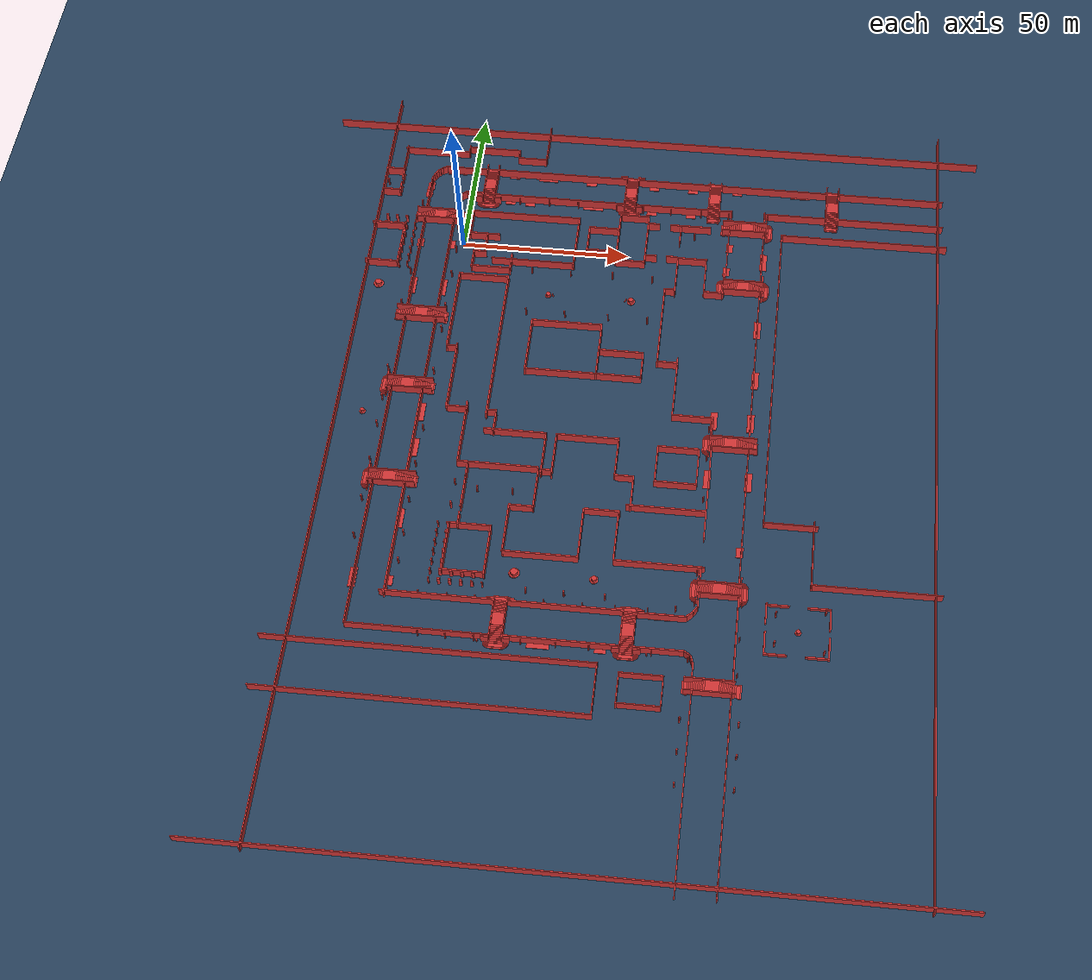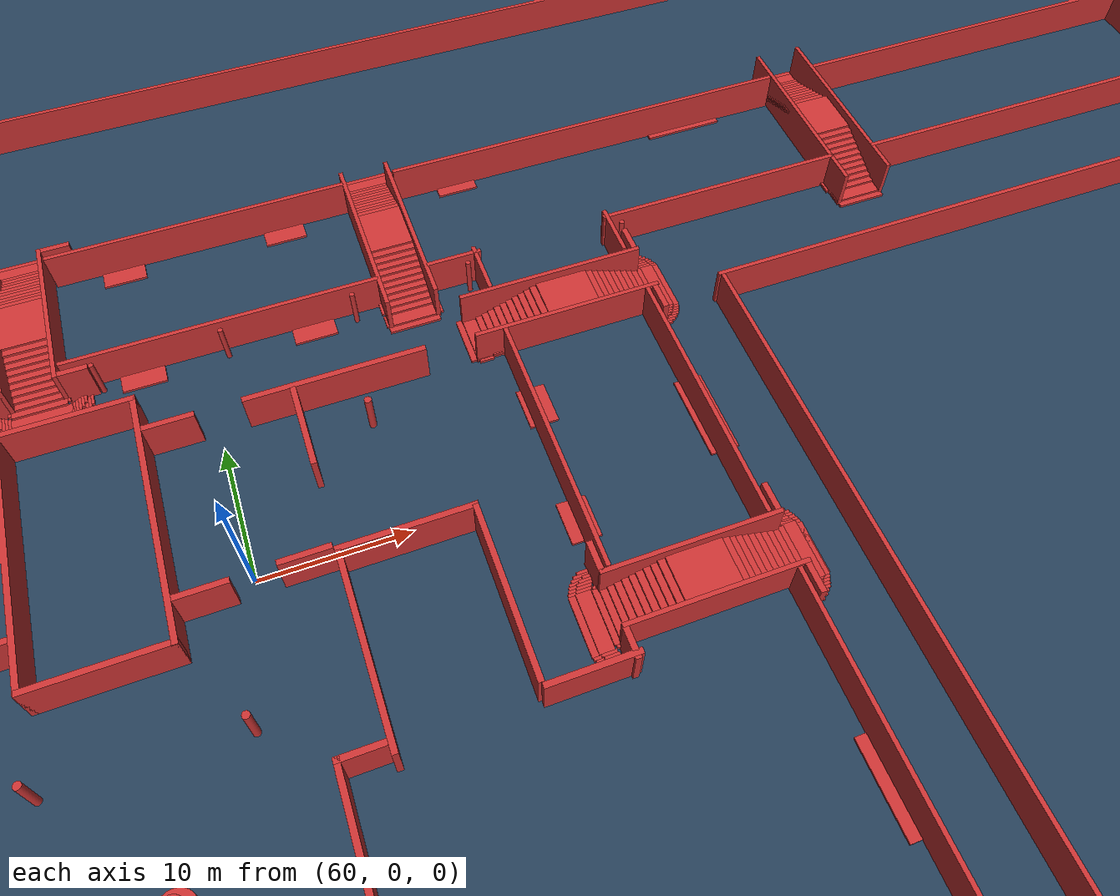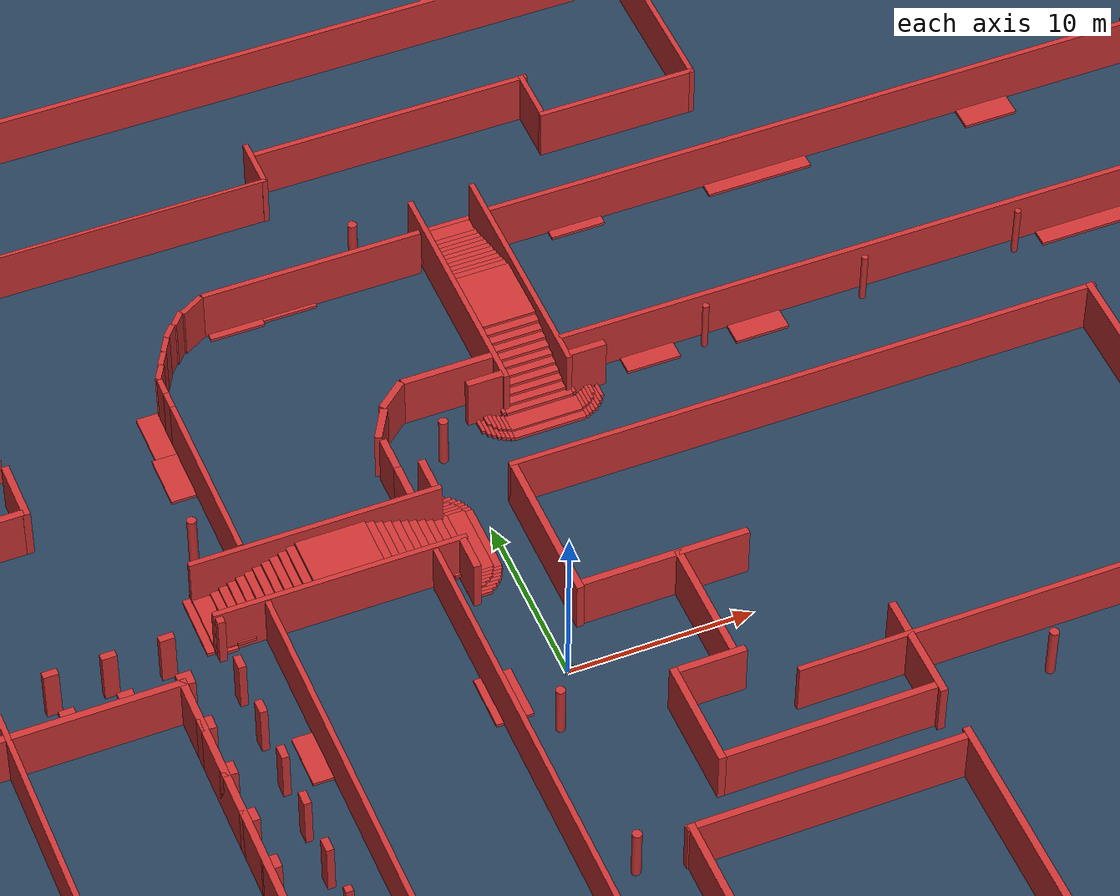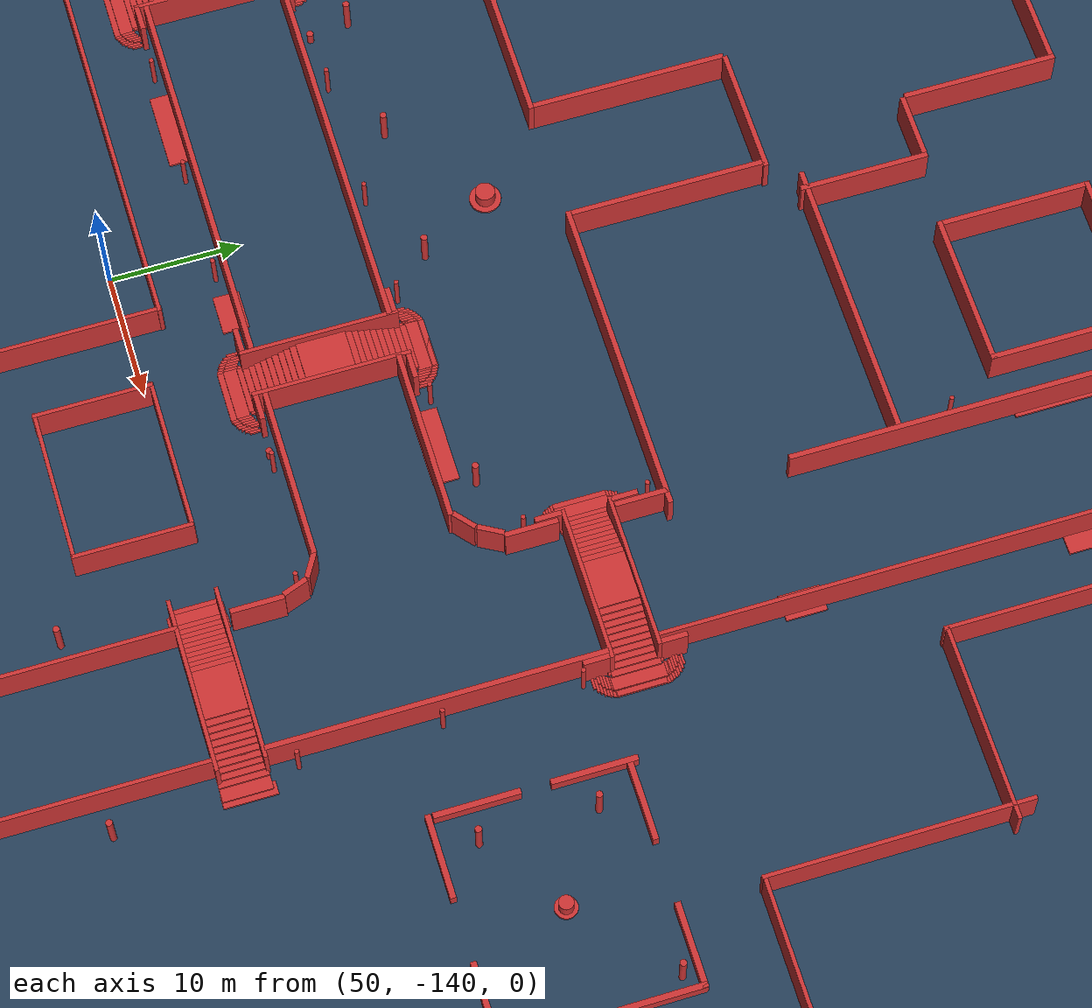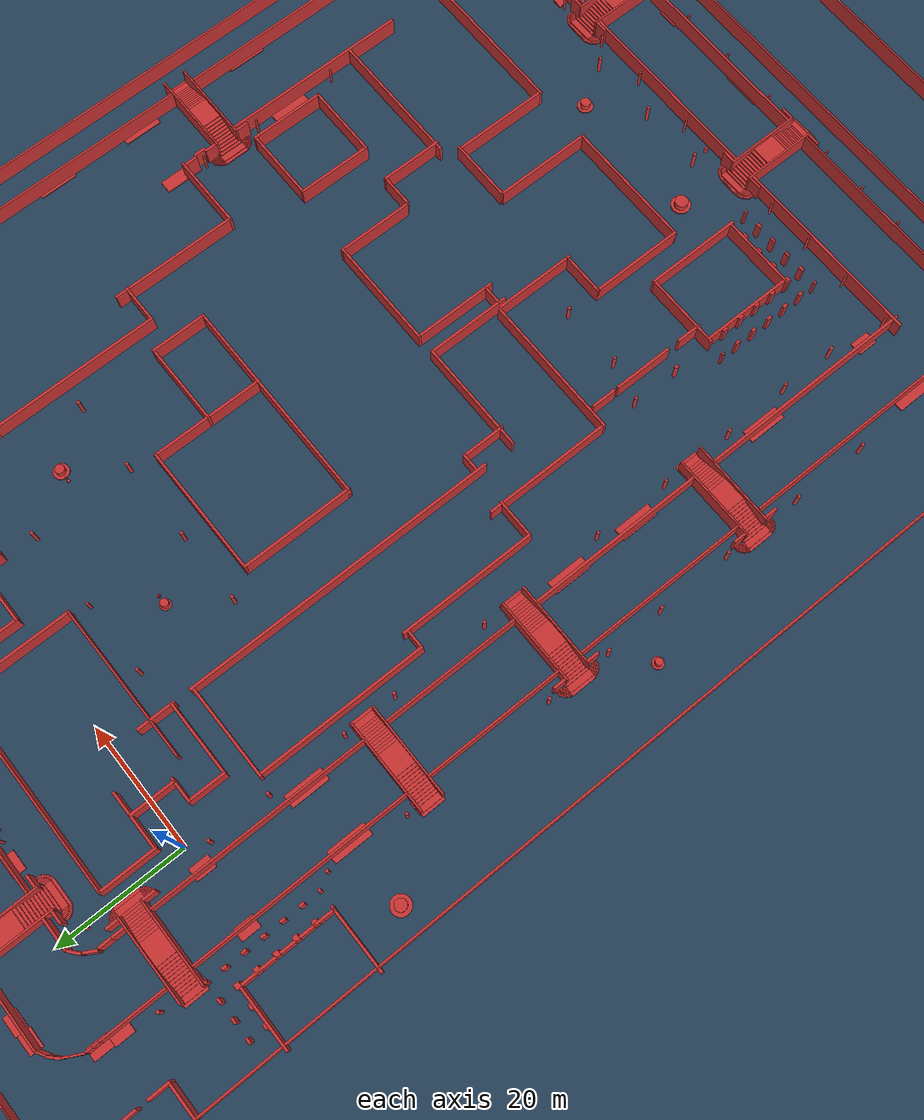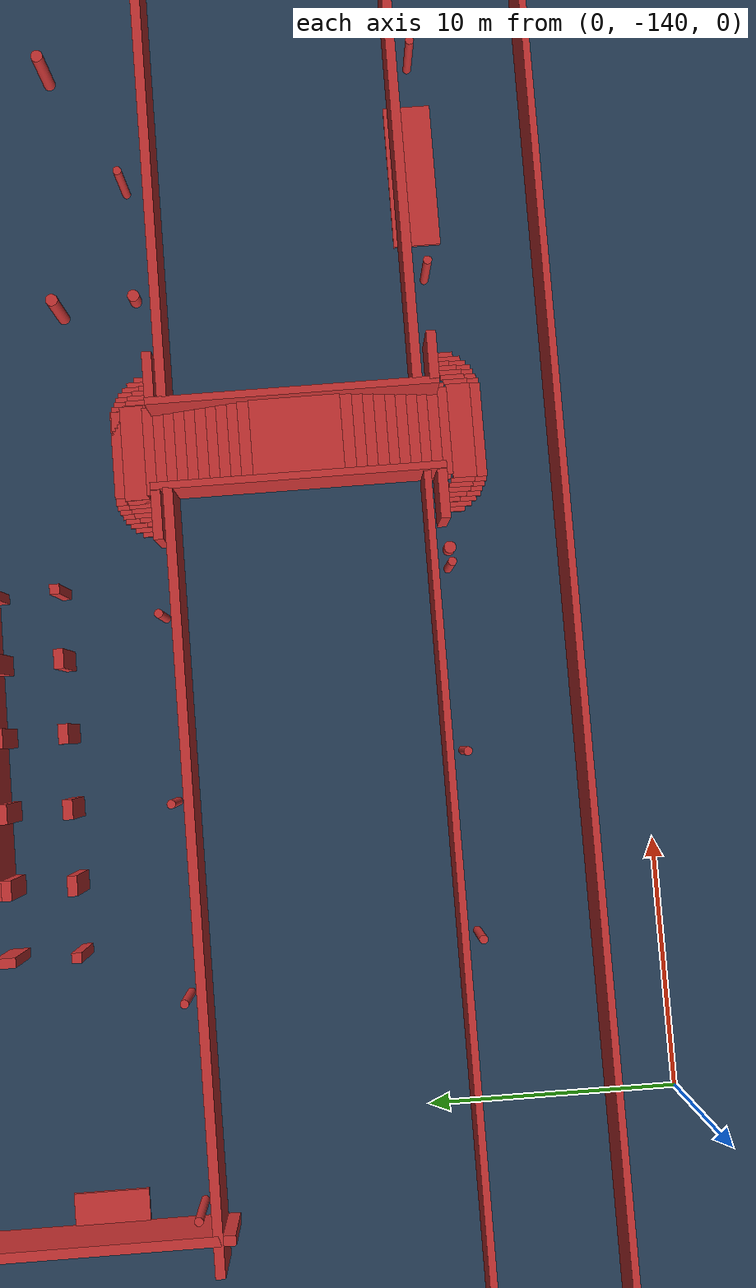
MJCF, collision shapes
<mujoco model="go2 scene">
  <include file="go2.xml" />
  <statistic center="0 0 0.1" extent="0.8" />

  <visual>
    <headlight diffuse="0.6 0.6 0.6" ambient="0.3 0.3 0.3" specular="0 0 0" />
    <rgba haze="0.15 0.25 0.35 1" />
    <global azimuth="-130" elevation="-20" />
    <map znear="0.01" zfar="100"/>
  </visual>

  <asset>
    <texture type="skybox" builtin="gradient" rgb1="0.3 0.5 0.7" rgb2="0 0 0" width="512" height="3072" />
    <texture type="2d" name="groundplane" builtin="checker" mark="edge" rgb1="0.2 0.3 0.4" rgb2="0.1 0.2 0.3" markrgb="0.8 0.8 0.8" width="300" height="300" />
    <material name="groundplane" texture="groundplane" texuniform="true" texrepeat="5 5" reflectance="0.2" />
    <material name="platform" rgba="0.75294 0.75294 0.75294 1" specular="0.3" shininess="0.5" />
  </asset>
  <worldbody>
    <light pos="0 0 1.5" dir="0 0 -1" directional="true" />
    <geom name="floor" size="0 0 0.01" type="plane" material="groundplane" />
<geom name="ps_Cube" type="box" size="0.5 2.0 0.1" pos="-0.95 9.5 0.09" quat="1.0 0.0 0.0 0.0" rgba="0.8 0.2 0.2 1"/>
<geom name="ps_Cube2" type="box" size="0.5 0.1 0.1" pos="-1.0 11.6 0.09" quat="1.0 0.0 0.0 0.0" rgba="0.8 0.2 0.2 1"/>
<geom name="ps_Cube3" type="box" size="0.5 0.1 0.1" pos="-1.1 11.8 0.09" quat="1.0 0.0 0.0 0.0" rgba="0.8 0.2 0.2 1"/>
<geom name="ps_Cube4" type="box" size="0.5 0.1 0.1" pos="-1.2 12.0 0.09" quat="1.0 0.0 0.0 0.0" rgba="0.8 0.2 0.2 1"/>
<geom name="ps_Cube5" type="box" size="0.5 0.1 0.1" pos="-1.3 12.2 0.09" quat="1.0 0.0 0.0 0.0" rgba="0.8 0.2 0.2 1"/>
<geom name="ps_Cube6" type="box" size="0.5 0.1 0.1" pos="-1.5 12.4 0.09" quat="1.0 0.0 0.0 0.0" rgba="0.8 0.2 0.2 1"/>
<geom name="ps_Cube7" type="box" size="0.5 0.1 0.1" pos="-1.7 12.6 0.09" quat="1.0 0.0 0.0 0.0" rgba="0.8 0.2 0.2 1"/>
<geom name="ps_Cube8" type="box" size="0.5 0.1 0.1" pos="-2.0 12.8 0.09" quat="1.0 0.0 0.0 0.0" rgba="0.8 0.2 0.2 1"/>
<geom name="ps_Cube9" type="box" size="0.5 0.1 0.1" pos="-1.0 7.4 0.09" quat="1.0 0.0 0.0 0.0" rgba="0.8 0.2 0.2 1"/>
<geom name="ps_Cube10" type="box" size="0.5 0.1 0.1" pos="-1.1 7.2 0.09" quat="1.0 0.0 0.0 0.0" rgba="0.8 0.2 0.2 1"/>
<geom name="ps_Cube11" type="box" size="0.5 0.1 0.1" pos="-1.2 7.0 0.09" quat="1.0 0.0 0.0 0.0" rgba="0.8 0.2 0.2 1"/>
<geom name="ps_Cube12" type="box" size="0.5 0.1 0.1" pos="-1.3 6.8 0.09" quat="1.0 0.0 0.0 0.0" rgba="0.8 0.2 0.2 1"/>
<geom name="ps_Cube13" type="box" size="0.5 0.1 0.1" pos="-1.5 6.6 0.09" quat="1.0 0.0 0.0 0.0" rgba="0.8 0.2 0.2 1"/>
<geom name="ps_Cube14" type="box" size="0.5 0.1 0.1" pos="-1.7 6.4 0.09" quat="1.0 0.0 0.0 0.0" rgba="0.8 0.2 0.2 1"/>
<geom name="ps_Cube15" type="box" size="0.5 0.1 0.1" pos="-2.0 6.2 0.09" quat="1.0 0.0 0.0 0.0" rgba="0.8 0.2 0.2 1"/>
<geom name="ps_Cube16" type="box" size="0.5 2.0 0.1" pos="-1.4 9.5 0.23" quat="1.0 0.0 0.0 0.0" rgba="0.8 0.2 0.2 1"/>
<geom name="ps_Cube17" type="box" size="0.5 0.1 0.1" pos="-1.5 7.4 0.23" quat="1.0 0.0 0.0 0.0" rgba="0.8 0.2 0.2 1"/>
<geom name="ps_Cube18" type="box" size="0.5 0.1 0.1" pos="-1.6 7.2 0.23" quat="1.0 0.0 0.0 0.0" rgba="0.8 0.2 0.2 1"/>
<geom name="ps_Cube19" type="box" size="0.5 0.1 0.1" pos="-1.7 7.0 0.23" quat="1.0 0.0 0.0 0.0" rgba="0.8 0.2 0.2 1"/>
<geom name="ps_Cube20" type="box" size="0.5 0.1 0.1" pos="-1.9 6.8 0.23" quat="1.0 0.0 0.0 0.0" rgba="0.8 0.2 0.2 1"/>
<geom name="ps_Cube21" type="box" size="0.5 0.1 0.1" pos="-2.2 6.6 0.23" quat="1.0 0.0 0.0 0.0" rgba="0.8 0.2 0.2 1"/>
<geom name="ps_Cube22" type="box" size="0.5 0.1 0.1" pos="-1.5 11.6 0.23" quat="1.0 0.0 0.0 0.0" rgba="0.8 0.2 0.2 1"/>
<geom name="ps_Cube23" type="box" size="0.5 0.1 0.1" pos="-1.6 11.8 0.23" quat="1.0 0.0 0.0 0.0" rgba="0.8 0.2 0.2 1"/>
<geom name="ps_Cube24" type="box" size="0.5 0.1 0.1" pos="-1.7 12.0 0.23" quat="1.0 0.0 0.0 0.0" rgba="0.8 0.2 0.2 1"/>
<geom name="ps_Cube25" type="box" size="0.5 0.1 0.1" pos="-1.9 12.2 0.23" quat="1.0 0.0 0.0 0.0" rgba="0.8 0.2 0.2 1"/>
<geom name="ps_Cube26" type="box" size="0.5 0.1 0.1" pos="-2.2 12.4 0.23" quat="1.0 0.0 0.0 0.0" rgba="0.8 0.2 0.2 1"/>
<geom name="ps_Cube27" type="box" size="0.5 1.85 0.1" pos="-2.4 9.5 0.42" quat="1.0 0.0 0.0 0.0" rgba="0.8 0.2 0.2 1"/>
<geom name="ps_Cube28" type="box" size="0.5 0.1 0.1" pos="-2.5 11.45 0.42" quat="1.0 0.0 0.0 0.0" rgba="0.8 0.2 0.2 1"/>
<geom name="ps_Cube29" type="box" size="0.5 0.1 0.1" pos="-2.5 7.55 0.42" quat="1.0 0.0 0.0 0.0" rgba="0.8 0.2 0.2 1"/>
<geom name="ps_Cube30" type="box" size="0.5 1.75 0.1" pos="-2.81 9.53 0.6" quat="1.0 0.0 0.0 0.0" rgba="0.8 0.2 0.2 1"/>
<geom name="ps_Cube31" type="box" size="0.5 1.75 0.1" pos="-3.28 9.53 0.78" quat="1.0 0.0 0.0 0.0" rgba="0.8 0.2 0.2 1"/>
<geom name="ps_Cube32" type="box" size="0.5 1.75 0.1" pos="-3.71 9.53 0.98" quat="1.0 0.0 0.0 0.0" rgba="0.8 0.2 0.2 1"/>
<geom name="ps_Cube33" type="box" size="0.5 1.75 0.1" pos="-4.17 9.53 1.15" quat="1.0 0.0 0.0 0.0" rgba="0.8 0.2 0.2 1"/>
<geom name="ps_Cube34" type="box" size="0.5 1.75 0.1" pos="-4.63 9.53 1.33" quat="1.0 0.0 0.0 0.0" rgba="0.8 0.2 0.2 1"/>
<geom name="ps_Cube35" type="box" size="0.5 1.75 0.1" pos="-5.06 9.53 1.51" quat="1.0 0.0 0.0 0.0" rgba="0.8 0.2 0.2 1"/>
<geom name="ps_Cube36" type="box" size="0.5 1.75 0.1" pos="-5.54 9.53 1.69" quat="1.0 0.0 0.0 0.0" rgba="0.8 0.2 0.2 1"/>
<geom name="ps_Cube37" type="box" size="0.5 1.75 0.1" pos="-5.99 9.53 1.87" quat="1.0 0.0 0.0 0.0" rgba="0.8 0.2 0.2 1"/>
<geom name="ps_Cube38" type="box" size="0.5 1.75 0.1" pos="-6.44 9.53 2.08" quat="1.0 0.0 0.0 0.0" rgba="0.8 0.2 0.2 1"/>
<geom name="ps_Cube39" type="box" size="1.875 1.75 0.1" pos="-8.3 9.53 2.25" quat="1.0 0.0 0.0 0.0" rgba="0.8 0.2 0.2 1"/>
<geom name="ps_Cube40" type="box" size="0.5 1.85 0.1" pos="-15.63 9.56 0.09" quat="0.0 0.0 0.0 -1.0" rgba="0.8 0.2 0.2 1"/>
<geom name="ps_Cube55" type="box" size="0.5 2.0 0.1" pos="-15.2 9.56 0.25" quat="0.0 0.0 0.0 -1.0" rgba="0.8 0.2 0.2 1"/>
<geom name="ps_Cube61" type="box" size="0.5 0.1 0.1" pos="-15.08 7.46 0.23" quat="0.0 0.0 0.0 -1.0" rgba="0.8 0.2 0.2 1"/>
<geom name="ps_Cube66" type="box" size="0.5 1.85 0.1" pos="-14.25 9.56 0.42" quat="0.0 0.0 0.0 -1.0" rgba="0.8 0.2 0.2 1"/>
<geom name="ps_Cube67" type="box" size="0.5 0.1 0.1" pos="-14.08 7.61 0.42" quat="0.0 0.0 0.0 -1.0" rgba="0.8 0.2 0.2 1"/>
<geom name="ps_Cube68" type="box" size="0.5 0.1 0.1" pos="-14.08 11.51 0.42" quat="0.0 0.0 0.0 -1.0" rgba="0.8 0.2 0.2 1"/>
<geom name="ps_Cube69" type="box" size="0.5 1.75 0.1" pos="-13.79 9.53 0.6" quat="0.0 0.0 0.0 -1.0" rgba="0.8 0.2 0.2 1"/>
<geom name="ps_Cube70" type="box" size="0.5 1.75 0.1" pos="-13.33 9.53 0.78" quat="0.0 0.0 0.0 -1.0" rgba="0.8 0.2 0.2 1"/>
<geom name="ps_Cube71" type="box" size="0.5 1.75 0.1" pos="-12.88 9.53 0.98" quat="0.0 0.0 0.0 -1.0" rgba="0.8 0.2 0.2 1"/>
<geom name="ps_Cube72" type="box" size="0.5 1.75 0.1" pos="-12.42 9.53 1.15" quat="0.0 0.0 0.0 -1.0" rgba="0.8 0.2 0.2 1"/>
<geom name="ps_Cube73" type="box" size="0.5 1.75 0.1" pos="-11.97 9.53 1.33" quat="0.0 0.0 0.0 -1.0" rgba="0.8 0.2 0.2 1"/>
<geom name="ps_Cube74" type="box" size="0.5 1.75 0.1" pos="-11.5 9.53 1.51" quat="0.0 0.0 0.0 -1.0" rgba="0.8 0.2 0.2 1"/>
<geom name="ps_Cube75" type="box" size="0.5 1.75 0.1" pos="-11.06 9.53 1.69" quat="0.0 0.0 0.0 -1.0" rgba="0.8 0.2 0.2 1"/>
<geom name="ps_Cube76" type="box" size="0.5 1.75 0.1" pos="-10.6 9.53 1.87" quat="0.0 0.0 0.0 -1.0" rgba="0.8 0.2 0.2 1"/>
<geom name="ps_Cube77" type="box" size="0.5 1.75 0.1" pos="-10.16 9.53 2.08" quat="0.0 0.0 0.0 -1.0" rgba="0.8 0.2 0.2 1"/>
<geom name="ps_Cube56" type="box" size="6.75 0.15 1.5" pos="-8.97 7.76 1.5" quat="0.0 0.0 0.0 -1.0" rgba="0.8 0.2 0.2 1"/>
<geom name="ps_Cube57" type="box" size="6.75 0.15 1.5" pos="-8.97 11.25 1.5" quat="0.0 0.0 0.0 -1.0" rgba="0.8 0.2 0.2 1"/>
<geom name="ps_Cube41" type="box" size="0.5 2.0 0.1" pos="-1.15 -28.1 0.09" quat="1.0 0.0 0.0 0.0" rgba="0.8 0.2 0.2 1"/>
<geom name="ps_Cube59" type="box" size="0.5 2.0 0.1" pos="-1.6 -28.1 0.23" quat="1.0 0.0 0.0 0.0" rgba="0.8 0.2 0.2 1"/>
<geom name="ps_Cube83" type="box" size="0.5 1.85 0.1" pos="-2.6 -28.1 0.42" quat="1.0 0.0 0.0 0.0" rgba="0.8 0.2 0.2 1"/>
<geom name="ps_Cube84" type="box" size="0.5 0.1 0.1" pos="-2.7 -26.15 0.42" quat="1.0 0.0 0.0 0.0" rgba="0.8 0.2 0.2 1"/>
<geom name="ps_Cube85" type="box" size="0.5 0.1 0.1" pos="-2.7 -30.05 0.42" quat="1.0 0.0 0.0 0.0" rgba="0.8 0.2 0.2 1"/>
<geom name="ps_Cube86" type="box" size="0.5 1.75 0.1" pos="-3.01 -28.07 0.6" quat="1.0 0.0 0.0 0.0" rgba="0.8 0.2 0.2 1"/>
<geom name="ps_Cube87" type="box" size="0.5 1.75 0.1" pos="-3.48 -28.07 0.78" quat="1.0 0.0 0.0 0.0" rgba="0.8 0.2 0.2 1"/>
<geom name="ps_Cube88" type="box" size="0.5 1.75 0.1" pos="-3.91 -28.07 0.98" quat="1.0 0.0 0.0 0.0" rgba="0.8 0.2 0.2 1"/>
<geom name="ps_Cube89" type="box" size="0.5 1.75 0.1" pos="-4.37 -28.07 1.15" quat="1.0 0.0 0.0 0.0" rgba="0.8 0.2 0.2 1"/>
<geom name="ps_Cube90" type="box" size="0.5 1.75 0.1" pos="-4.83 -28.07 1.33" quat="1.0 0.0 0.0 0.0" rgba="0.8 0.2 0.2 1"/>
<geom name="ps_Cube91" type="box" size="0.5 1.75 0.1" pos="-5.26 -28.07 1.51" quat="1.0 0.0 0.0 0.0" rgba="0.8 0.2 0.2 1"/>
<geom name="ps_Cube92" type="box" size="0.5 1.75 0.1" pos="-5.74 -28.07 1.69" quat="1.0 0.0 0.0 0.0" rgba="0.8 0.2 0.2 1"/>
<geom name="ps_Cube93" type="box" size="0.5 1.75 0.1" pos="-6.19 -28.07 1.87" quat="1.0 0.0 0.0 0.0" rgba="0.8 0.2 0.2 1"/>
<geom name="ps_Cube94" type="box" size="0.5 1.75 0.1" pos="-6.64 -28.07 2.08" quat="1.0 0.0 0.0 0.0" rgba="0.8 0.2 0.2 1"/>
<geom name="ps_Cube95" type="box" size="1.875 1.75 0.1" pos="-8.5 -28.07 2.25" quat="1.0 0.0 0.0 0.0" rgba="0.8 0.2 0.2 1"/>
<geom name="ps_Cube96" type="box" size="0.5 1.85 0.1" pos="-15.83 -28.04 0.09" quat="0.0 0.0 0.0 -1.0" rgba="0.8 0.2 0.2 1"/>
<geom name="ps_Cube97" type="box" size="0.5 2.0 0.1" pos="-15.4 -28.04 0.25" quat="0.0 0.0 0.0 -1.0" rgba="0.8 0.2 0.2 1"/>
<geom name="ps_Cube98" type="box" size="0.5 0.1 0.1" pos="-15.28 -30.14 0.23" quat="0.0 0.0 0.0 -1.0" rgba="0.8 0.2 0.2 1"/>
<geom name="ps_Cube99" type="box" size="0.5 1.85 0.1" pos="-14.45 -28.04 0.42" quat="0.0 0.0 0.0 -1.0" rgba="0.8 0.2 0.2 1"/>
<geom name="ps_Cube100" type="box" size="0.5 0.1 0.1" pos="-14.28 -29.99 0.42" quat="0.0 0.0 0.0 -1.0" rgba="0.8 0.2 0.2 1"/>
<geom name="ps_Cube101" type="box" size="0.5 0.1 0.1" pos="-14.28 -26.09 0.42" quat="0.0 0.0 0.0 -1.0" rgba="0.8 0.2 0.2 1"/>
<geom name="ps_Cube102" type="box" size="0.5 1.75 0.1" pos="-13.99 -28.07 0.6" quat="0.0 0.0 0.0 -1.0" rgba="0.8 0.2 0.2 1"/>
<geom name="ps_Cube103" type="box" size="0.5 1.75 0.1" pos="-13.53 -28.07 0.78" quat="0.0 0.0 0.0 -1.0" rgba="0.8 0.2 0.2 1"/>
<geom name="ps_Cube104" type="box" size="0.5 1.75 0.1" pos="-13.08 -28.07 0.98" quat="0.0 0.0 0.0 -1.0" rgba="0.8 0.2 0.2 1"/>
<geom name="ps_Cube105" type="box" size="0.5 1.75 0.1" pos="-12.62 -28.07 1.15" quat="0.0 0.0 0.0 -1.0" rgba="0.8 0.2 0.2 1"/>
<geom name="ps_Cube106" type="box" size="0.5 1.75 0.1" pos="-12.17 -28.07 1.33" quat="0.0 0.0 0.0 -1.0" rgba="0.8 0.2 0.2 1"/>
<geom name="ps_Cube107" type="box" size="0.5 1.75 0.1" pos="-11.7 -28.07 1.51" quat="0.0 0.0 0.0 -1.0" rgba="0.8 0.2 0.2 1"/>
<geom name="ps_Cube108" type="box" size="0.5 1.75 0.1" pos="-11.26 -28.07 1.69" quat="0.0 0.0 0.0 -1.0" rgba="0.8 0.2 0.2 1"/>
<geom name="ps_Cube109" type="box" size="0.5 1.75 0.1" pos="-10.8 -28.07 1.87" quat="0.0 0.0 0.0 -1.0" rgba="0.8 0.2 0.2 1"/>
<geom name="ps_Cube110" type="box" size="0.5 1.75 0.1" pos="-10.36 -28.07 2.08" quat="0.0 0.0 0.0 -1.0" rgba="0.8 0.2 0.2 1"/>
<geom name="ps_Cube112" type="box" size="7.35 0.15 1.5" pos="-8.57 -26.33 1.5" quat="0.0 0.0 0.0 -1.0" rgba="0.8 0.2 0.2 1"/>
<geom name="ps_Cube113" type="box" size="0.5 2.0 0.1" pos="-15.89 -53.5 0.09" quat="0.0 0.0 0.0 -1.0" rgba="0.8 0.2 0.2 1"/>
<geom name="ps_Cube114" type="box" size="0.5 0.1 0.1" pos="-15.84 -55.6 0.09" quat="0.0 0.0 0.0 -1.0" rgba="0.8 0.2 0.2 1"/>
<geom name="ps_Cube115" type="box" size="0.5 0.1 0.1" pos="-15.74 -55.8 0.09" quat="0.0 0.0 0.0 -1.0" rgba="0.8 0.2 0.2 1"/>
<geom name="ps_Cube116" type="box" size="0.5 0.1 0.1" pos="-15.64 -56.0 0.09" quat="0.0 0.0 0.0 -1.0" rgba="0.8 0.2 0.2 1"/>
<geom name="ps_Cube117" type="box" size="0.5 0.1 0.1" pos="-15.54 -56.2 0.09" quat="0.0 0.0 0.0 -1.0" rgba="0.8 0.2 0.2 1"/>
<geom name="ps_Cube118" type="box" size="0.5 0.1 0.1" pos="-15.34 -56.4 0.09" quat="0.0 0.0 0.0 -1.0" rgba="0.8 0.2 0.2 1"/>
<geom name="ps_Cube119" type="box" size="0.5 0.1 0.1" pos="-15.14 -56.6 0.09" quat="0.0 0.0 0.0 -1.0" rgba="0.8 0.2 0.2 1"/>
<geom name="ps_Cube120" type="box" size="0.5 0.1 0.1" pos="-14.84 -56.8 0.09" quat="0.0 0.0 0.0 -1.0" rgba="0.8 0.2 0.2 1"/>
<geom name="ps_Cube121" type="box" size="0.5 0.1 0.1" pos="-15.84 -51.4 0.09" quat="0.0 0.0 0.0 -1.0" rgba="0.8 0.2 0.2 1"/>
<geom name="ps_Cube122" type="box" size="0.5 0.1 0.1" pos="-15.74 -51.2 0.09" quat="0.0 0.0 0.0 -1.0" rgba="0.8 0.2 0.2 1"/>
<geom name="ps_Cube123" type="box" size="0.5 0.1 0.1" pos="-15.64 -51.0 0.09" quat="0.0 0.0 0.0 -1.0" rgba="0.8 0.2 0.2 1"/>
<geom name="ps_Cube124" type="box" size="0.5 0.1 0.1" pos="-15.54 -50.8 0.09" quat="0.0 0.0 0.0 -1.0" rgba="0.8 0.2 0.2 1"/>
<geom name="ps_Cube125" type="box" size="0.5 0.1 0.1" pos="-15.34 -50.6 0.09" quat="0.0 0.0 0.0 -1.0" rgba="0.8 0.2 0.2 1"/>
<geom name="ps_Cube126" type="box" size="0.5 0.1 0.1" pos="-15.14 -50.4 0.09" quat="0.0 0.0 0.0 -1.0" rgba="0.8 0.2 0.2 1"/>
<geom name="ps_Cube127" type="box" size="0.5 0.1 0.1" pos="-14.84 -50.2 0.09" quat="0.0 0.0 0.0 -1.0" rgba="0.8 0.2 0.2 1"/>
<geom name="ps_Cube128" type="box" size="0.5 2.0 0.1" pos="-15.44 -53.5 0.23" quat="0.0 0.0 0.0 -1.0" rgba="0.8 0.2 0.2 1"/>
<geom name="ps_Cube129" type="box" size="0.5 0.1 0.1" pos="-15.34 -51.4 0.23" quat="0.0 0.0 0.0 -1.0" rgba="0.8 0.2 0.2 1"/>
<geom name="ps_Cube130" type="box" size="0.5 0.1 0.1" pos="-15.24 -51.2 0.23" quat="0.0 0.0 0.0 -1.0" rgba="0.8 0.2 0.2 1"/>
<geom name="ps_Cube131" type="box" size="0.5 0.1 0.1" pos="-15.14 -51.0 0.23" quat="0.0 0.0 0.0 -1.0" rgba="0.8 0.2 0.2 1"/>
<geom name="ps_Cube132" type="box" size="0.5 0.1 0.1" pos="-14.94 -50.8 0.23" quat="0.0 0.0 0.0 -1.0" rgba="0.8 0.2 0.2 1"/>
<geom name="ps_Cube133" type="box" size="0.5 0.1 0.1" pos="-14.64 -50.6 0.23" quat="0.0 0.0 0.0 -1.0" rgba="0.8 0.2 0.2 1"/>
<geom name="ps_Cube134" type="box" size="0.5 0.1 0.1" pos="-15.34 -55.6 0.23" quat="0.0 0.0 0.0 -1.0" rgba="0.8 0.2 0.2 1"/>
<geom name="ps_Cube135" type="box" size="0.5 0.1 0.1" pos="-15.24 -55.8 0.23" quat="0.0 0.0 0.0 -1.0" rgba="0.8 0.2 0.2 1"/>
<geom name="ps_Cube136" type="box" size="0.5 0.1 0.1" pos="-15.14 -56.0 0.23" quat="0.0 0.0 0.0 -1.0" rgba="0.8 0.2 0.2 1"/>
<geom name="ps_Cube137" type="box" size="0.5 0.1 0.1" pos="-14.94 -56.2 0.23" quat="0.0 0.0 0.0 -1.0" rgba="0.8 0.2 0.2 1"/>
<geom name="ps_Cube138" type="box" size="0.5 0.1 0.1" pos="-14.64 -56.4 0.23" quat="0.0 0.0 0.0 -1.0" rgba="0.8 0.2 0.2 1"/>
<geom name="ps_Cube139" type="box" size="0.5 1.85 0.1" pos="-14.44 -53.5 0.42" quat="0.0 0.0 0.0 -1.0" rgba="0.8 0.2 0.2 1"/>
<geom name="ps_Cube140" type="box" size="0.5 0.1 0.1" pos="-14.34 -55.45 0.42" quat="0.0 0.0 0.0 -1.0" rgba="0.8 0.2 0.2 1"/>
<geom name="ps_Cube141" type="box" size="0.5 0.1 0.1" pos="-14.34 -51.55 0.42" quat="0.0 0.0 0.0 -1.0" rgba="0.8 0.2 0.2 1"/>
<geom name="ps_Cube142" type="box" size="0.5 1.75 0.1" pos="-14.03 -53.53 0.6" quat="0.0 0.0 0.0 -1.0" rgba="0.8 0.2 0.2 1"/>
<geom name="ps_Cube143" type="box" size="0.5 1.75 0.1" pos="-13.56 -53.53 0.78" quat="0.0 0.0 0.0 -1.0" rgba="0.8 0.2 0.2 1"/>
<geom name="ps_Cube144" type="box" size="0.5 1.75 0.1" pos="-13.13 -53.53 0.98" quat="0.0 0.0 0.0 -1.0" rgba="0.8 0.2 0.2 1"/>
<geom name="ps_Cube145" type="box" size="0.5 1.75 0.1" pos="-12.67 -53.53 1.15" quat="0.0 0.0 0.0 -1.0" rgba="0.8 0.2 0.2 1"/>
<geom name="ps_Cube146" type="box" size="0.5 1.75 0.1" pos="-12.21 -53.53 1.33" quat="0.0 0.0 0.0 -1.0" rgba="0.8 0.2 0.2 1"/>
<geom name="ps_Cube147" type="box" size="0.5 1.75 0.1" pos="-11.78 -53.53 1.51" quat="0.0 0.0 0.0 -1.0" rgba="0.8 0.2 0.2 1"/>
<geom name="ps_Cube148" type="box" size="0.5 1.75 0.1" pos="-11.3 -53.53 1.69" quat="0.0 0.0 0.0 -1.0" rgba="0.8 0.2 0.2 1"/>
<geom name="ps_Cube149" type="box" size="0.5 1.75 0.1" pos="-10.85 -53.53 1.87" quat="0.0 0.0 0.0 -1.0" rgba="0.8 0.2 0.2 1"/>
<geom name="ps_Cube150" type="box" size="0.5 1.75 0.1" pos="-10.4 -53.53 2.08" quat="0.0 0.0 0.0 -1.0" rgba="0.8 0.2 0.2 1"/>
<geom name="ps_Cube151" type="box" size="1.875 1.75 0.1" pos="-8.54 -53.53 2.25" quat="0.0 0.0 0.0 -1.0" rgba="0.8 0.2 0.2 1"/>
<geom name="ps_Cube152" type="box" size="0.5 1.85 0.1" pos="-1.21 -53.559999 0.09" quat="1.0 0.0 0.0 0.0" rgba="0.8 0.2 0.2 1"/>
<geom name="ps_Cube153" type="box" size="0.5 2.0 0.1" pos="-1.64 -53.659999 0.25" quat="1.0 0.0 0.0 0.0" rgba="0.8 0.2 0.2 1"/>
<geom name="ps_Cube155" type="box" size="0.5 1.85 0.1" pos="-2.59 -53.56 0.42" quat="1.0 0.0 0.0 0.0" rgba="0.8 0.2 0.2 1"/>
<geom name="ps_Cube156" type="box" size="0.5 0.1 0.1" pos="-2.76 -51.61 0.42" quat="1.0 0.0 0.0 0.0" rgba="0.8 0.2 0.2 1"/>
<geom name="ps_Cube157" type="box" size="0.5 0.1 0.1" pos="-2.76 -55.51 0.42" quat="1.0 0.0 0.0 0.0" rgba="0.8 0.2 0.2 1"/>
<geom name="ps_Cube158" type="box" size="0.5 1.75 0.1" pos="-3.05 -53.53 0.6" quat="1.0 0.0 0.0 0.0" rgba="0.8 0.2 0.2 1"/>
<geom name="ps_Cube159" type="box" size="0.5 1.75 0.1" pos="-3.51 -53.53 0.78" quat="1.0 0.0 0.0 0.0" rgba="0.8 0.2 0.2 1"/>
<geom name="ps_Cube160" type="box" size="0.5 1.75 0.1" pos="-3.96 -53.53 0.98" quat="1.0 0.0 0.0 0.0" rgba="0.8 0.2 0.2 1"/>
<geom name="ps_Cube161" type="box" size="0.5 1.75 0.1" pos="-4.42 -53.53 1.15" quat="1.0 0.0 0.0 0.0" rgba="0.8 0.2 0.2 1"/>
<geom name="ps_Cube162" type="box" size="0.5 1.75 0.1" pos="-4.87 -53.53 1.33" quat="1.0 0.0 0.0 0.0" rgba="0.8 0.2 0.2 1"/>
<geom name="ps_Cube163" type="box" size="0.5 1.75 0.1" pos="-5.34 -53.53 1.51" quat="1.0 0.0 0.0 0.0" rgba="0.8 0.2 0.2 1"/>
<geom name="ps_Cube164" type="box" size="0.5 1.75 0.1" pos="-5.78 -53.53 1.69" quat="1.0 0.0 0.0 0.0" rgba="0.8 0.2 0.2 1"/>
<geom name="ps_Cube165" type="box" size="0.5 1.75 0.1" pos="-6.24 -53.53 1.87" quat="1.0 0.0 0.0 0.0" rgba="0.8 0.2 0.2 1"/>
<geom name="ps_Cube166" type="box" size="0.5 1.75 0.1" pos="-6.68 -53.53 2.08" quat="1.0 0.0 0.0 0.0" rgba="0.8 0.2 0.2 1"/>
<geom name="ps_Cube167" type="box" size="6.75 0.15 1.5" pos="-7.87 -51.81 1.5" quat="1.0 0.0 0.0 0.0" rgba="0.8 0.2 0.2 1"/>
<geom name="ps_Cube168" type="box" size="6.75 0.15 1.5" pos="-7.87 -55.4 1.5" quat="1.0 0.0 0.0 0.0" rgba="0.8 0.2 0.2 1"/>
<geom name="ps_Cube169" type="box" size="0.5 2.0 0.1" pos="-15.89 -85.3 0.09" quat="0.0 0.0 0.0 -1.0" rgba="0.8 0.2 0.2 1"/>
<geom name="ps_Cube170" type="box" size="0.5 0.1 0.1" pos="-15.84 -87.4 0.09" quat="0.0 0.0 0.0 -1.0" rgba="0.8 0.2 0.2 1"/>
<geom name="ps_Cube171" type="box" size="0.5 0.1 0.1" pos="-15.74 -87.6 0.09" quat="0.0 0.0 0.0 -1.0" rgba="0.8 0.2 0.2 1"/>
<geom name="ps_Cube172" type="box" size="0.5 0.1 0.1" pos="-15.64 -87.8 0.09" quat="0.0 0.0 0.0 -1.0" rgba="0.8 0.2 0.2 1"/>
<geom name="ps_Cube173" type="box" size="0.5 0.1 0.1" pos="-15.54 -88.0 0.09" quat="0.0 0.0 0.0 -1.0" rgba="0.8 0.2 0.2 1"/>
<geom name="ps_Cube174" type="box" size="0.5 0.1 0.1" pos="-15.34 -88.2 0.09" quat="0.0 0.0 0.0 -1.0" rgba="0.8 0.2 0.2 1"/>
<geom name="ps_Cube175" type="box" size="0.5 0.1 0.1" pos="-15.14 -88.4 0.09" quat="0.0 0.0 0.0 -1.0" rgba="0.8 0.2 0.2 1"/>
<geom name="ps_Cube176" type="box" size="0.5 0.1 0.1" pos="-14.84 -88.6 0.09" quat="0.0 0.0 0.0 -1.0" rgba="0.8 0.2 0.2 1"/>
<geom name="ps_Cube177" type="box" size="0.5 0.1 0.1" pos="-15.84 -83.2 0.09" quat="0.0 0.0 0.0 -1.0" rgba="0.8 0.2 0.2 1"/>
<geom name="ps_Cube178" type="box" size="0.5 0.1 0.1" pos="-15.74 -83.0 0.09" quat="0.0 0.0 0.0 -1.0" rgba="0.8 0.2 0.2 1"/>
<geom name="ps_Cube179" type="box" size="0.5 0.1 0.1" pos="-15.64 -82.8 0.09" quat="0.0 0.0 0.0 -1.0" rgba="0.8 0.2 0.2 1"/>
<geom name="ps_Cube180" type="box" size="0.5 0.1 0.1" pos="-15.54 -82.6 0.09" quat="0.0 0.0 0.0 -1.0" rgba="0.8 0.2 0.2 1"/>
<geom name="ps_Cube181" type="box" size="0.5 0.1 0.1" pos="-15.34 -82.4 0.09" quat="0.0 0.0 0.0 -1.0" rgba="0.8 0.2 0.2 1"/>
<geom name="ps_Cube182" type="box" size="0.5 0.1 0.1" pos="-15.14 -82.2 0.09" quat="0.0 0.0 0.0 -1.0" rgba="0.8 0.2 0.2 1"/>
<geom name="ps_Cube183" type="box" size="0.5 0.1 0.1" pos="-14.84 -82.0 0.09" quat="0.0 0.0 0.0 -1.0" rgba="0.8 0.2 0.2 1"/>
<geom name="ps_Cube184" type="box" size="0.5 2.0 0.1" pos="-15.44 -85.3 0.23" quat="0.0 0.0 0.0 -1.0" rgba="0.8 0.2 0.2 1"/>
<geom name="ps_Cube185" type="box" size="0.5 0.1 0.1" pos="-15.34 -83.2 0.23" quat="0.0 0.0 0.0 -1.0" rgba="0.8 0.2 0.2 1"/>
<geom name="ps_Cube186" type="box" size="0.5 0.1 0.1" pos="-15.24 -83.0 0.23" quat="0.0 0.0 0.0 -1.0" rgba="0.8 0.2 0.2 1"/>
<geom name="ps_Cube187" type="box" size="0.5 0.1 0.1" pos="-15.14 -82.8 0.23" quat="0.0 0.0 0.0 -1.0" rgba="0.8 0.2 0.2 1"/>
<geom name="ps_Cube188" type="box" size="0.5 0.1 0.1" pos="-14.94 -82.6 0.23" quat="0.0 0.0 0.0 -1.0" rgba="0.8 0.2 0.2 1"/>
<geom name="ps_Cube189" type="box" size="0.5 0.1 0.1" pos="-14.64 -82.4 0.23" quat="0.0 0.0 0.0 -1.0" rgba="0.8 0.2 0.2 1"/>
<geom name="ps_Cube190" type="box" size="0.5 0.1 0.1" pos="-15.34 -87.4 0.23" quat="0.0 0.0 0.0 -1.0" rgba="0.8 0.2 0.2 1"/>
<geom name="ps_Cube191" type="box" size="0.5 0.1 0.1" pos="-15.24 -87.6 0.23" quat="0.0 0.0 0.0 -1.0" rgba="0.8 0.2 0.2 1"/>
<geom name="ps_Cube192" type="box" size="0.5 0.1 0.1" pos="-15.14 -87.8 0.23" quat="0.0 0.0 0.0 -1.0" rgba="0.8 0.2 0.2 1"/>
<geom name="ps_Cube193" type="box" size="0.5 0.1 0.1" pos="-14.94 -88.0 0.23" quat="0.0 0.0 0.0 -1.0" rgba="0.8 0.2 0.2 1"/>
<geom name="ps_Cube194" type="box" size="0.5 0.1 0.1" pos="-14.64 -88.2 0.23" quat="0.0 0.0 0.0 -1.0" rgba="0.8 0.2 0.2 1"/>
<geom name="ps_Cube195" type="box" size="0.5 1.85 0.1" pos="-14.44 -85.3 0.42" quat="0.0 0.0 0.0 -1.0" rgba="0.8 0.2 0.2 1"/>
<geom name="ps_Cube196" type="box" size="0.5 0.1 0.1" pos="-14.34 -87.25 0.42" quat="0.0 0.0 0.0 -1.0" rgba="0.8 0.2 0.2 1"/>
<geom name="ps_Cube197" type="box" size="0.5 0.1 0.1" pos="-14.34 -83.35 0.42" quat="0.0 0.0 0.0 -1.0" rgba="0.8 0.2 0.2 1"/>
<geom name="ps_Cube198" type="box" size="0.5 1.75 0.1" pos="-14.03 -85.33 0.6" quat="0.0 0.0 0.0 -1.0" rgba="0.8 0.2 0.2 1"/>
<geom name="ps_Cube199" type="box" size="0.5 1.75 0.1" pos="-13.56 -85.33 0.78" quat="0.0 0.0 0.0 -1.0" rgba="0.8 0.2 0.2 1"/>
<geom name="ps_Cube200" type="box" size="0.5 1.75 0.1" pos="-13.13 -85.33 0.98" quat="0.0 0.0 0.0 -1.0" rgba="0.8 0.2 0.2 1"/>
<geom name="ps_Cube201" type="box" size="0.5 1.75 0.1" pos="-12.67 -85.33 1.15" quat="0.0 0.0 0.0 -1.0" rgba="0.8 0.2 0.2 1"/>
<geom name="ps_Cube202" type="box" size="0.5 1.75 0.1" pos="-12.21 -85.33 1.33" quat="0.0 0.0 0.0 -1.0" rgba="0.8 0.2 0.2 1"/>
<geom name="ps_Cube203" type="box" size="0.5 1.75 0.1" pos="-11.78 -85.33 1.51" quat="0.0 0.0 0.0 -1.0" rgba="0.8 0.2 0.2 1"/>
<geom name="ps_Cube204" type="box" size="0.5 1.75 0.1" pos="-11.3 -85.33 1.69" quat="0.0 0.0 0.0 -1.0" rgba="0.8 0.2 0.2 1"/>
<geom name="ps_Cube205" type="box" size="0.5 1.75 0.1" pos="-10.85 -85.33 1.87" quat="0.0 0.0 0.0 -1.0" rgba="0.8 0.2 0.2 1"/>
<geom name="ps_Cube206" type="box" size="0.5 1.75 0.1" pos="-10.4 -85.33 2.08" quat="0.0 0.0 0.0 -1.0" rgba="0.8 0.2 0.2 1"/>
<geom name="ps_Cube207" type="box" size="1.875 1.75 0.1" pos="-8.54 -85.33 2.25" quat="0.0 0.0 0.0 -1.0" rgba="0.8 0.2 0.2 1"/>
<geom name="ps_Cube208" type="box" size="0.5 1.85 0.1" pos="-1.21 -85.259999 0.09" quat="1.0 0.0 0.0 0.0" rgba="0.8 0.2 0.2 1"/>
<geom name="ps_Cube209" type="box" size="0.5 2.0 0.1" pos="-1.64 -85.359999 0.25" quat="1.0 0.0 0.0 0.0" rgba="0.8 0.2 0.2 1"/>
<geom name="ps_Cube211" type="box" size="0.5 1.85 0.1" pos="-2.59 -85.36 0.42" quat="1.0 0.0 0.0 0.0" rgba="0.8 0.2 0.2 1"/>
<geom name="ps_Cube212" type="box" size="0.5 0.1 0.1" pos="-2.76 -83.41 0.42" quat="1.0 0.0 0.0 0.0" rgba="0.8 0.2 0.2 1"/>
<geom name="ps_Cube213" type="box" size="0.5 0.1 0.1" pos="-2.76 -87.31 0.42" quat="1.0 0.0 0.0 0.0" rgba="0.8 0.2 0.2 1"/>
<geom name="ps_Cube214" type="box" size="0.5 1.75 0.1" pos="-3.05 -85.33 0.6" quat="1.0 0.0 0.0 0.0" rgba="0.8 0.2 0.2 1"/>
<geom name="ps_Cube215" type="box" size="0.5 1.75 0.1" pos="-3.51 -85.33 0.78" quat="1.0 0.0 0.0 0.0" rgba="0.8 0.2 0.2 1"/>
<geom name="ps_Cube216" type="box" size="0.5 1.75 0.1" pos="-3.96 -85.33 0.98" quat="1.0 0.0 0.0 0.0" rgba="0.8 0.2 0.2 1"/>
<geom name="ps_Cube217" type="box" size="0.5 1.75 0.1" pos="-4.42 -85.33 1.15" quat="1.0 0.0 0.0 0.0" rgba="0.8 0.2 0.2 1"/>
<geom name="ps_Cube218" type="box" size="0.5 1.75 0.1" pos="-4.87 -85.33 1.33" quat="1.0 0.0 0.0 0.0" rgba="0.8 0.2 0.2 1"/>
<geom name="ps_Cube219" type="box" size="0.5 1.75 0.1" pos="-5.34 -85.33 1.51" quat="1.0 0.0 0.0 0.0" rgba="0.8 0.2 0.2 1"/>
<geom name="ps_Cube220" type="box" size="0.5 1.75 0.1" pos="-5.78 -85.33 1.69" quat="1.0 0.0 0.0 0.0" rgba="0.8 0.2 0.2 1"/>
<geom name="ps_Cube221" type="box" size="0.5 1.75 0.1" pos="-6.24 -85.33 1.87" quat="1.0 0.0 0.0 0.0" rgba="0.8 0.2 0.2 1"/>
<geom name="ps_Cube222" type="box" size="0.5 1.75 0.1" pos="-6.68 -85.33 2.08" quat="1.0 0.0 0.0 0.0" rgba="0.8 0.2 0.2 1"/>
<geom name="ps_Cube223" type="box" size="6.75 0.15 1.5" pos="-7.87 -83.56 1.5" quat="1.0 0.0 0.0 0.0" rgba="0.8 0.2 0.2 1"/>
<geom name="ps_Cube224" type="box" size="6.75 0.15 1.5" pos="-7.87 -87.05 1.5" quat="1.0 0.0 0.0 0.0" rgba="0.8 0.2 0.2 1"/>
<geom name="ps_Cube225" type="box" size="0.5 2.0 0.1" pos="27.58 -133.97 0.09" quat="0.707107 0.0 0.0 -0.707107" rgba="0.8 0.2 0.2 1"/>
<geom name="ps_Cube226" type="box" size="0.5 0.1 0.1" pos="29.68 -133.92 0.09" quat="0.707107 0.0 0.0 -0.707107" rgba="0.8 0.2 0.2 1"/>
<geom name="ps_Cube227" type="box" size="0.5 0.1 0.1" pos="29.88 -133.82 0.09" quat="0.707107 0.0 0.0 -0.707107" rgba="0.8 0.2 0.2 1"/>
<geom name="ps_Cube228" type="box" size="0.5 0.1 0.1" pos="30.08 -133.72 0.09" quat="0.707107 0.0 0.0 -0.707107" rgba="0.8 0.2 0.2 1"/>
<geom name="ps_Cube229" type="box" size="0.5 0.1 0.1" pos="30.28 -133.62 0.09" quat="0.707107 0.0 0.0 -0.707107" rgba="0.8 0.2 0.2 1"/>
<geom name="ps_Cube230" type="box" size="0.5 0.1 0.1" pos="30.48 -133.42 0.09" quat="0.707107 0.0 0.0 -0.707107" rgba="0.8 0.2 0.2 1"/>
<geom name="ps_Cube231" type="box" size="0.5 0.1 0.1" pos="30.68 -133.22 0.09" quat="0.707107 0.0 0.0 -0.707107" rgba="0.8 0.2 0.2 1"/>
<geom name="ps_Cube232" type="box" size="0.5 0.1 0.1" pos="30.88 -132.92 0.09" quat="0.707107 0.0 0.0 -0.707107" rgba="0.8 0.2 0.2 1"/>
<geom name="ps_Cube233" type="box" size="0.5 0.1 0.1" pos="25.48 -133.92 0.09" quat="0.707107 0.0 0.0 -0.707107" rgba="0.8 0.2 0.2 1"/>
<geom name="ps_Cube234" type="box" size="0.5 0.1 0.1" pos="25.28 -133.82 0.09" quat="0.707107 0.0 0.0 -0.707107" rgba="0.8 0.2 0.2 1"/>
<geom name="ps_Cube235" type="box" size="0.5 0.1 0.1" pos="25.08 -133.72 0.09" quat="0.707107 0.0 0.0 -0.707107" rgba="0.8 0.2 0.2 1"/>
<geom name="ps_Cube236" type="box" size="0.5 0.1 0.1" pos="24.88 -133.62 0.09" quat="0.707107 0.0 0.0 -0.707107" rgba="0.8 0.2 0.2 1"/>
<geom name="ps_Cube237" type="box" size="0.5 0.1 0.1" pos="24.68 -133.42 0.09" quat="0.707107 0.0 0.0 -0.707107" rgba="0.8 0.2 0.2 1"/>
<geom name="ps_Cube238" type="box" size="0.5 0.1 0.1" pos="24.48 -133.22 0.09" quat="0.707107 0.0 0.0 -0.707107" rgba="0.8 0.2 0.2 1"/>
<geom name="ps_Cube239" type="box" size="0.5 0.1 0.1" pos="24.28 -132.92 0.09" quat="0.707107 0.0 0.0 -0.707107" rgba="0.8 0.2 0.2 1"/>
<geom name="ps_Cube240" type="box" size="0.5 2.0 0.1" pos="27.58 -133.52 0.23" quat="0.707107 0.0 0.0 -0.707107" rgba="0.8 0.2 0.2 1"/>
<geom name="ps_Cube241" type="box" size="0.5 0.1 0.1" pos="25.48 -133.42 0.23" quat="0.707107 0.0 0.0 -0.707107" rgba="0.8 0.2 0.2 1"/>
<geom name="ps_Cube242" type="box" size="0.5 0.1 0.1" pos="25.28 -133.32 0.23" quat="0.707107 0.0 0.0 -0.707107" rgba="0.8 0.2 0.2 1"/>
<geom name="ps_Cube243" type="box" size="0.5 0.1 0.1" pos="25.08 -133.22 0.23" quat="0.707107 0.0 0.0 -0.707107" rgba="0.8 0.2 0.2 1"/>
<geom name="ps_Cube244" type="box" size="0.5 0.1 0.1" pos="24.88 -133.02 0.23" quat="0.707107 0.0 0.0 -0.707107" rgba="0.8 0.2 0.2 1"/>
<geom name="ps_Cube245" type="box" size="0.5 0.1 0.1" pos="24.68 -132.72 0.23" quat="0.707107 0.0 0.0 -0.707107" rgba="0.8 0.2 0.2 1"/>
<geom name="ps_Cube246" type="box" size="0.5 0.1 0.1" pos="29.68 -133.42 0.23" quat="0.707107 0.0 0.0 -0.707107" rgba="0.8 0.2 0.2 1"/>
<geom name="ps_Cube247" type="box" size="0.5 0.1 0.1" pos="29.88 -133.32 0.23" quat="0.707107 0.0 0.0 -0.707107" rgba="0.8 0.2 0.2 1"/>
<geom name="ps_Cube248" type="box" size="0.5 0.1 0.1" pos="30.08 -133.22 0.23" quat="0.707107 0.0 0.0 -0.707107" rgba="0.8 0.2 0.2 1"/>
<geom name="ps_Cube249" type="box" size="0.5 0.1 0.1" pos="30.28 -133.02 0.23" quat="0.707107 0.0 0.0 -0.707107" rgba="0.8 0.2 0.2 1"/>
<geom name="ps_Cube250" type="box" size="0.5 0.1 0.1" pos="30.48 -132.72 0.23" quat="0.707107 0.0 0.0 -0.707107" rgba="0.8 0.2 0.2 1"/>
<geom name="ps_Cube251" type="box" size="0.5 1.85 0.1" pos="27.58 -132.52 0.42" quat="0.707107 0.0 0.0 -0.707107" rgba="0.8 0.2 0.2 1"/>
<geom name="ps_Cube252" type="box" size="0.5 0.1 0.1" pos="29.53 -132.42 0.42" quat="0.707107 0.0 0.0 -0.707107" rgba="0.8 0.2 0.2 1"/>
<geom name="ps_Cube253" type="box" size="0.5 0.1 0.1" pos="25.63 -132.42 0.42" quat="0.707107 0.0 0.0 -0.707107" rgba="0.8 0.2 0.2 1"/>
<geom name="ps_Cube254" type="box" size="0.5 1.75 0.1" pos="27.61 -132.11 0.6" quat="0.707107 0.0 0.0 -0.707107" rgba="0.8 0.2 0.2 1"/>
<geom name="ps_Cube255" type="box" size="0.5 1.75 0.1" pos="27.61 -131.64 0.78" quat="0.707107 0.0 0.0 -0.707107" rgba="0.8 0.2 0.2 1"/>
<geom name="ps_Cube256" type="box" size="0.5 1.75 0.1" pos="27.61 -131.21 0.98" quat="0.707107 0.0 0.0 -0.707107" rgba="0.8 0.2 0.2 1"/>
<geom name="ps_Cube257" type="box" size="0.5 1.75 0.1" pos="27.61 -130.75 1.15" quat="0.707107 0.0 0.0 -0.707107" rgba="0.8 0.2 0.2 1"/>
<geom name="ps_Cube258" type="box" size="0.5 1.75 0.1" pos="27.61 -130.29 1.33" quat="0.707107 0.0 0.0 -0.707107" rgba="0.8 0.2 0.2 1"/>
<geom name="ps_Cube259" type="box" size="0.5 1.75 0.1" pos="27.61 -129.86 1.51" quat="0.707107 0.0 0.0 -0.707107" rgba="0.8 0.2 0.2 1"/>
<geom name="ps_Cube260" type="box" size="0.5 1.75 0.1" pos="27.61 -129.38 1.69" quat="0.707107 0.0 0.0 -0.707107" rgba="0.8 0.2 0.2 1"/>
<geom name="ps_Cube261" type="box" size="0.5 1.75 0.1" pos="27.61 -128.93 1.87" quat="0.707107 0.0 0.0 -0.707107" rgba="0.8 0.2 0.2 1"/>
<geom name="ps_Cube262" type="box" size="0.5 1.75 0.1" pos="27.61 -128.48 2.08" quat="0.707107 0.0 0.0 -0.707107" rgba="0.8 0.2 0.2 1"/>
<geom name="ps_Cube263" type="box" size="1.875 1.75 0.1" pos="27.61 -126.62 2.25" quat="0.707107 0.0 0.0 -0.707107" rgba="0.8 0.2 0.2 1"/>
<geom name="ps_Cube264" type="box" size="0.5 1.85 0.1" pos="27.64 -119.29 0.09" quat="0.707107 0.0 0.0 0.707107" rgba="0.8 0.2 0.2 1"/>
<geom name="ps_Cube265" type="box" size="0.5 2.0 0.1" pos="27.64 -119.72 0.25" quat="0.707107 0.0 0.0 0.707107" rgba="0.8 0.2 0.2 1"/>
<geom name="ps_Cube266" type="box" size="0.5 0.1 0.1" pos="25.54 -119.84 0.23" quat="0.707107 0.0 0.0 0.707107" rgba="0.8 0.2 0.2 1"/>
<geom name="ps_Cube267" type="box" size="0.5 1.85 0.1" pos="27.64 -120.67 0.42" quat="0.707107 0.0 0.0 0.707107" rgba="0.8 0.2 0.2 1"/>
<geom name="ps_Cube268" type="box" size="0.5 0.1 0.1" pos="25.69 -120.84 0.42" quat="0.707107 0.0 0.0 0.707107" rgba="0.8 0.2 0.2 1"/>
<geom name="ps_Cube269" type="box" size="0.5 0.1 0.1" pos="29.59 -120.84 0.42" quat="0.707107 0.0 0.0 0.707107" rgba="0.8 0.2 0.2 1"/>
<geom name="ps_Cube270" type="box" size="0.5 1.75 0.1" pos="27.61 -121.13 0.6" quat="0.707107 0.0 0.0 0.707107" rgba="0.8 0.2 0.2 1"/>
<geom name="ps_Cube271" type="box" size="0.5 1.75 0.1" pos="27.61 -121.59 0.78" quat="0.707107 0.0 0.0 0.707107" rgba="0.8 0.2 0.2 1"/>
<geom name="ps_Cube272" type="box" size="0.5 1.75 0.1" pos="27.61 -122.04 0.98" quat="0.707107 0.0 0.0 0.707107" rgba="0.8 0.2 0.2 1"/>
<geom name="ps_Cube273" type="box" size="0.5 1.75 0.1" pos="27.61 -122.5 1.15" quat="0.707107 0.0 0.0 0.707107" rgba="0.8 0.2 0.2 1"/>
<geom name="ps_Cube274" type="box" size="0.5 1.75 0.1" pos="27.61 -122.95 1.33" quat="0.707107 0.0 0.0 0.707107" rgba="0.8 0.2 0.2 1"/>
<geom name="ps_Cube275" type="box" size="0.5 1.75 0.1" pos="27.61 -123.42 1.51" quat="0.707107 0.0 0.0 0.707107" rgba="0.8 0.2 0.2 1"/>
<geom name="ps_Cube276" type="box" size="0.5 1.75 0.1" pos="27.61 -123.86 1.69" quat="0.707107 0.0 0.0 0.707107" rgba="0.8 0.2 0.2 1"/>
<geom name="ps_Cube277" type="box" size="0.5 1.75 0.1" pos="27.61 -124.32 1.87" quat="0.707107 0.0 0.0 0.707107" rgba="0.8 0.2 0.2 1"/>
<geom name="ps_Cube278" type="box" size="0.5 1.75 0.1" pos="27.61 -124.76 2.08" quat="0.707107 0.0 0.0 0.707107" rgba="0.8 0.2 0.2 1"/>
<geom name="ps_Cube279" type="box" size="6.0 0.15 1.5" pos="25.76 -126.59 1.5" quat="0.707107 0.0 0.0 0.707107" rgba="0.8 0.2 0.2 1"/>
<geom name="ps_Cube280" type="box" size="6.0 0.15 1.5" pos="29.25 -126.58 1.5" quat="0.707107 0.0 0.0 0.707107" rgba="0.8 0.2 0.2 1"/>
<geom name="ps_Cube281" type="box" size="0.5 2.0 0.1" pos="62.08 -133.97 0.09" quat="0.707107 0.0 0.0 -0.707107" rgba="0.8 0.2 0.2 1"/>
<geom name="ps_Cube282" type="box" size="0.5 0.1 0.1" pos="64.18 -133.92 0.09" quat="0.707107 0.0 0.0 -0.707107" rgba="0.8 0.2 0.2 1"/>
<geom name="ps_Cube283" type="box" size="0.5 0.1 0.1" pos="64.38 -133.82 0.09" quat="0.707107 0.0 0.0 -0.707107" rgba="0.8 0.2 0.2 1"/>
<geom name="ps_Cube284" type="box" size="0.5 0.1 0.1" pos="64.58 -133.72 0.09" quat="0.707107 0.0 0.0 -0.707107" rgba="0.8 0.2 0.2 1"/>
<geom name="ps_Cube285" type="box" size="0.5 0.1 0.1" pos="64.78 -133.62 0.09" quat="0.707107 0.0 0.0 -0.707107" rgba="0.8 0.2 0.2 1"/>
<geom name="ps_Cube286" type="box" size="0.5 0.1 0.1" pos="64.98 -133.42 0.09" quat="0.707107 0.0 0.0 -0.707107" rgba="0.8 0.2 0.2 1"/>
<geom name="ps_Cube287" type="box" size="0.5 0.1 0.1" pos="65.18 -133.22 0.09" quat="0.707107 0.0 0.0 -0.707107" rgba="0.8 0.2 0.2 1"/>
<geom name="ps_Cube288" type="box" size="0.5 0.1 0.1" pos="65.38 -132.92 0.09" quat="0.707107 0.0 0.0 -0.707107" rgba="0.8 0.2 0.2 1"/>
<geom name="ps_Cube289" type="box" size="0.5 0.1 0.1" pos="59.98 -133.92 0.09" quat="0.707107 0.0 0.0 -0.707107" rgba="0.8 0.2 0.2 1"/>
<geom name="ps_Cube290" type="box" size="0.5 0.1 0.1" pos="59.78 -133.82 0.09" quat="0.707107 0.0 0.0 -0.707107" rgba="0.8 0.2 0.2 1"/>
<geom name="ps_Cube291" type="box" size="0.5 0.1 0.1" pos="59.58 -133.72 0.09" quat="0.707107 0.0 0.0 -0.707107" rgba="0.8 0.2 0.2 1"/>
<geom name="ps_Cube292" type="box" size="0.5 0.1 0.1" pos="59.38 -133.62 0.09" quat="0.707107 0.0 0.0 -0.707107" rgba="0.8 0.2 0.2 1"/>
<geom name="ps_Cube293" type="box" size="0.5 0.1 0.1" pos="59.18 -133.42 0.09" quat="0.707107 0.0 0.0 -0.707107" rgba="0.8 0.2 0.2 1"/>
<geom name="ps_Cube294" type="box" size="0.5 0.1 0.1" pos="58.98 -133.22 0.09" quat="0.707107 0.0 0.0 -0.707107" rgba="0.8 0.2 0.2 1"/>
<geom name="ps_Cube295" type="box" size="0.5 0.1 0.1" pos="58.78 -132.92 0.09" quat="0.707107 0.0 0.0 -0.707107" rgba="0.8 0.2 0.2 1"/>
<geom name="ps_Cube296" type="box" size="0.5 2.0 0.1" pos="62.08 -133.52 0.23" quat="0.707107 0.0 0.0 -0.707107" rgba="0.8 0.2 0.2 1"/>
<geom name="ps_Cube297" type="box" size="0.5 0.1 0.1" pos="59.98 -133.42 0.23" quat="0.707107 0.0 0.0 -0.707107" rgba="0.8 0.2 0.2 1"/>
<geom name="ps_Cube298" type="box" size="0.5 0.1 0.1" pos="59.78 -133.32 0.23" quat="0.707107 0.0 0.0 -0.707107" rgba="0.8 0.2 0.2 1"/>
<geom name="ps_Cube299" type="box" size="0.5 0.1 0.1" pos="59.58 -133.22 0.23" quat="0.707107 0.0 0.0 -0.707107" rgba="0.8 0.2 0.2 1"/>
<geom name="ps_Cube300" type="box" size="0.5 0.1 0.1" pos="59.38 -133.02 0.23" quat="0.707107 0.0 0.0 -0.707107" rgba="0.8 0.2 0.2 1"/>
<geom name="ps_Cube301" type="box" size="0.5 0.1 0.1" pos="59.18 -132.72 0.23" quat="0.707107 0.0 0.0 -0.707107" rgba="0.8 0.2 0.2 1"/>
<geom name="ps_Cube302" type="box" size="0.5 0.1 0.1" pos="64.18 -133.42 0.23" quat="0.707107 0.0 0.0 -0.707107" rgba="0.8 0.2 0.2 1"/>
<geom name="ps_Cube303" type="box" size="0.5 0.1 0.1" pos="64.38 -133.32 0.23" quat="0.707107 0.0 0.0 -0.707107" rgba="0.8 0.2 0.2 1"/>
<geom name="ps_Cube304" type="box" size="0.5 0.1 0.1" pos="64.58 -133.22 0.23" quat="0.707107 0.0 0.0 -0.707107" rgba="0.8 0.2 0.2 1"/>
<geom name="ps_Cube305" type="box" size="0.5 0.1 0.1" pos="64.78 -133.02 0.23" quat="0.707107 0.0 0.0 -0.707107" rgba="0.8 0.2 0.2 1"/>
<geom name="ps_Cube306" type="box" size="0.5 0.1 0.1" pos="64.98 -132.72 0.23" quat="0.707107 0.0 0.0 -0.707107" rgba="0.8 0.2 0.2 1"/>
<geom name="ps_Cube307" type="box" size="0.5 1.85 0.1" pos="62.08 -132.52 0.42" quat="0.707107 0.0 0.0 -0.707107" rgba="0.8 0.2 0.2 1"/>
<geom name="ps_Cube308" type="box" size="0.5 0.1 0.1" pos="64.03 -132.42 0.42" quat="0.707107 0.0 0.0 -0.707107" rgba="0.8 0.2 0.2 1"/>
<geom name="ps_Cube309" type="box" size="0.5 0.1 0.1" pos="60.13 -132.42 0.42" quat="0.707107 0.0 0.0 -0.707107" rgba="0.8 0.2 0.2 1"/>
<geom name="ps_Cube310" type="box" size="0.5 1.75 0.1" pos="62.11 -132.11 0.6" quat="0.707107 0.0 0.0 -0.707107" rgba="0.8 0.2 0.2 1"/>
<geom name="ps_Cube311" type="box" size="0.5 1.75 0.1" pos="62.11 -131.64 0.78" quat="0.707107 0.0 0.0 -0.707107" rgba="0.8 0.2 0.2 1"/>
<geom name="ps_Cube312" type="box" size="0.5 1.75 0.1" pos="62.11 -131.21 0.98" quat="0.707107 0.0 0.0 -0.707107" rgba="0.8 0.2 0.2 1"/>
<geom name="ps_Cube313" type="box" size="0.5 1.75 0.1" pos="62.11 -130.75 1.15" quat="0.707107 0.0 0.0 -0.707107" rgba="0.8 0.2 0.2 1"/>
<geom name="ps_Cube314" type="box" size="0.5 1.75 0.1" pos="62.11 -130.29 1.33" quat="0.707107 0.0 0.0 -0.707107" rgba="0.8 0.2 0.2 1"/>
<geom name="ps_Cube315" type="box" size="0.5 1.75 0.1" pos="62.11 -129.86 1.51" quat="0.707107 0.0 0.0 -0.707107" rgba="0.8 0.2 0.2 1"/>
<geom name="ps_Cube316" type="box" size="0.5 1.75 0.1" pos="62.11 -129.38 1.69" quat="0.707107 0.0 0.0 -0.707107" rgba="0.8 0.2 0.2 1"/>
<geom name="ps_Cube317" type="box" size="0.5 1.75 0.1" pos="62.11 -128.93 1.87" quat="0.707107 0.0 0.0 -0.707107" rgba="0.8 0.2 0.2 1"/>
<geom name="ps_Cube318" type="box" size="0.5 1.75 0.1" pos="62.11 -128.48 2.08" quat="0.707107 0.0 0.0 -0.707107" rgba="0.8 0.2 0.2 1"/>
<geom name="ps_Cube319" type="box" size="1.875 1.75 0.1" pos="62.11 -126.62 2.25" quat="0.707107 0.0 0.0 -0.707107" rgba="0.8 0.2 0.2 1"/>
<geom name="ps_Cube320" type="box" size="0.5 1.85 0.1" pos="62.14 -119.29 0.09" quat="0.707107 0.0 0.0 0.707107" rgba="0.8 0.2 0.2 1"/>
<geom name="ps_Cube321" type="box" size="0.5 2.0 0.1" pos="62.14 -119.72 0.25" quat="0.707107 0.0 0.0 0.707107" rgba="0.8 0.2 0.2 1"/>
<geom name="ps_Cube322" type="box" size="0.5 0.1 0.1" pos="60.04 -119.84 0.23" quat="0.707107 0.0 0.0 0.707107" rgba="0.8 0.2 0.2 1"/>
<geom name="ps_Cube323" type="box" size="0.5 1.85 0.1" pos="62.14 -120.67 0.42" quat="0.707107 0.0 0.0 0.707107" rgba="0.8 0.2 0.2 1"/>
<geom name="ps_Cube324" type="box" size="0.5 0.1 0.1" pos="60.19 -120.84 0.42" quat="0.707107 0.0 0.0 0.707107" rgba="0.8 0.2 0.2 1"/>
<geom name="ps_Cube325" type="box" size="0.5 0.1 0.1" pos="64.09 -120.84 0.42" quat="0.707107 0.0 0.0 0.707107" rgba="0.8 0.2 0.2 1"/>
<geom name="ps_Cube326" type="box" size="0.5 1.75 0.1" pos="62.11 -121.13 0.6" quat="0.707107 0.0 0.0 0.707107" rgba="0.8 0.2 0.2 1"/>
<geom name="ps_Cube327" type="box" size="0.5 1.75 0.1" pos="62.11 -121.59 0.78" quat="0.707107 0.0 0.0 0.707107" rgba="0.8 0.2 0.2 1"/>
<geom name="ps_Cube328" type="box" size="0.5 1.75 0.1" pos="62.11 -122.04 0.98" quat="0.707107 0.0 0.0 0.707107" rgba="0.8 0.2 0.2 1"/>
<geom name="ps_Cube329" type="box" size="0.5 1.75 0.1" pos="62.11 -122.5 1.15" quat="0.707107 0.0 0.0 0.707107" rgba="0.8 0.2 0.2 1"/>
<geom name="ps_Cube330" type="box" size="0.5 1.75 0.1" pos="62.11 -122.95 1.33" quat="0.707107 0.0 0.0 0.707107" rgba="0.8 0.2 0.2 1"/>
<geom name="ps_Cube331" type="box" size="0.5 1.75 0.1" pos="62.11 -123.42 1.51" quat="0.707107 0.0 0.0 0.707107" rgba="0.8 0.2 0.2 1"/>
<geom name="ps_Cube332" type="box" size="0.5 1.75 0.1" pos="62.11 -123.86 1.69" quat="0.707107 0.0 0.0 0.707107" rgba="0.8 0.2 0.2 1"/>
<geom name="ps_Cube333" type="box" size="0.5 1.75 0.1" pos="62.11 -124.32 1.87" quat="0.707107 0.0 0.0 0.707107" rgba="0.8 0.2 0.2 1"/>
<geom name="ps_Cube334" type="box" size="0.5 1.75 0.1" pos="62.11 -124.76 2.08" quat="0.707107 0.0 0.0 0.707107" rgba="0.8 0.2 0.2 1"/>
<geom name="ps_Cube336" type="box" size="6.0 0.15 1.5" pos="63.83 -126.64 1.5" quat="0.707107 0.0 0.0 0.707107" rgba="0.8 0.2 0.2 1"/>
<geom name="ps_Cube337" type="box" size="0.5 2.0 0.1" pos="77.91 -112.1 0.09" quat="0.0 0.0 0.0 -1.0" rgba="0.8 0.2 0.2 1"/>
<geom name="ps_Cube338" type="box" size="0.5 0.1 0.1" pos="77.96 -114.2 0.09" quat="0.0 0.0 0.0 -1.0" rgba="0.8 0.2 0.2 1"/>
<geom name="ps_Cube339" type="box" size="0.5 0.1 0.1" pos="78.06 -114.4 0.09" quat="0.0 0.0 0.0 -1.0" rgba="0.8 0.2 0.2 1"/>
<geom name="ps_Cube340" type="box" size="0.5 0.1 0.1" pos="78.16 -114.6 0.09" quat="0.0 0.0 0.0 -1.0" rgba="0.8 0.2 0.2 1"/>
<geom name="ps_Cube341" type="box" size="0.5 0.1 0.1" pos="78.26 -114.8 0.09" quat="0.0 0.0 0.0 -1.0" rgba="0.8 0.2 0.2 1"/>
<geom name="ps_Cube342" type="box" size="0.5 0.1 0.1" pos="78.46 -115.0 0.09" quat="0.0 0.0 0.0 -1.0" rgba="0.8 0.2 0.2 1"/>
<geom name="ps_Cube343" type="box" size="0.5 0.1 0.1" pos="78.66 -115.2 0.09" quat="0.0 0.0 0.0 -1.0" rgba="0.8 0.2 0.2 1"/>
<geom name="ps_Cube344" type="box" size="0.5 0.1 0.1" pos="78.96 -115.4 0.09" quat="0.0 0.0 0.0 -1.0" rgba="0.8 0.2 0.2 1"/>
<geom name="ps_Cube345" type="box" size="0.5 0.1 0.1" pos="77.96 -110.0 0.09" quat="0.0 0.0 0.0 -1.0" rgba="0.8 0.2 0.2 1"/>
<geom name="ps_Cube346" type="box" size="0.5 0.1 0.1" pos="78.06 -109.8 0.09" quat="0.0 0.0 0.0 -1.0" rgba="0.8 0.2 0.2 1"/>
<geom name="ps_Cube347" type="box" size="0.5 0.1 0.1" pos="78.16 -109.6 0.09" quat="0.0 0.0 0.0 -1.0" rgba="0.8 0.2 0.2 1"/>
<geom name="ps_Cube348" type="box" size="0.5 0.1 0.1" pos="78.26 -109.4 0.09" quat="0.0 0.0 0.0 -1.0" rgba="0.8 0.2 0.2 1"/>
<geom name="ps_Cube349" type="box" size="0.5 0.1 0.1" pos="78.46 -109.2 0.09" quat="0.0 0.0 0.0 -1.0" rgba="0.8 0.2 0.2 1"/>
<geom name="ps_Cube350" type="box" size="0.5 0.1 0.1" pos="78.66 -109.0 0.09" quat="0.0 0.0 0.0 -1.0" rgba="0.8 0.2 0.2 1"/>
<geom name="ps_Cube351" type="box" size="0.5 0.1 0.1" pos="78.96 -108.8 0.09" quat="0.0 0.0 0.0 -1.0" rgba="0.8 0.2 0.2 1"/>
<geom name="ps_Cube352" type="box" size="0.5 2.0 0.1" pos="78.36 -112.1 0.23" quat="0.0 0.0 0.0 -1.0" rgba="0.8 0.2 0.2 1"/>
<geom name="ps_Cube353" type="box" size="0.5 0.1 0.1" pos="78.46 -110.0 0.23" quat="0.0 0.0 0.0 -1.0" rgba="0.8 0.2 0.2 1"/>
<geom name="ps_Cube354" type="box" size="0.5 0.1 0.1" pos="78.56 -109.8 0.23" quat="0.0 0.0 0.0 -1.0" rgba="0.8 0.2 0.2 1"/>
<geom name="ps_Cube355" type="box" size="0.5 0.1 0.1" pos="78.66 -109.6 0.23" quat="0.0 0.0 0.0 -1.0" rgba="0.8 0.2 0.2 1"/>
<geom name="ps_Cube356" type="box" size="0.5 0.1 0.1" pos="78.86 -109.4 0.23" quat="0.0 0.0 0.0 -1.0" rgba="0.8 0.2 0.2 1"/>
<geom name="ps_Cube357" type="box" size="0.5 0.1 0.1" pos="79.16 -109.2 0.23" quat="0.0 0.0 0.0 -1.0" rgba="0.8 0.2 0.2 1"/>
<geom name="ps_Cube358" type="box" size="0.5 0.1 0.1" pos="78.46 -114.2 0.23" quat="0.0 0.0 0.0 -1.0" rgba="0.8 0.2 0.2 1"/>
<geom name="ps_Cube359" type="box" size="0.5 0.1 0.1" pos="78.56 -114.4 0.23" quat="0.0 0.0 0.0 -1.0" rgba="0.8 0.2 0.2 1"/>
<geom name="ps_Cube360" type="box" size="0.5 0.1 0.1" pos="78.66 -114.6 0.23" quat="0.0 0.0 0.0 -1.0" rgba="0.8 0.2 0.2 1"/>
<geom name="ps_Cube361" type="box" size="0.5 0.1 0.1" pos="78.86 -114.8 0.23" quat="0.0 0.0 0.0 -1.0" rgba="0.8 0.2 0.2 1"/>
<geom name="ps_Cube362" type="box" size="0.5 0.1 0.1" pos="79.16 -115.0 0.23" quat="0.0 0.0 0.0 -1.0" rgba="0.8 0.2 0.2 1"/>
<geom name="ps_Cube363" type="box" size="0.5 1.85 0.1" pos="79.36 -112.1 0.42" quat="0.0 0.0 0.0 -1.0" rgba="0.8 0.2 0.2 1"/>
<geom name="ps_Cube364" type="box" size="0.5 0.1 0.1" pos="79.46 -114.05 0.42" quat="0.0 0.0 0.0 -1.0" rgba="0.8 0.2 0.2 1"/>
<geom name="ps_Cube365" type="box" size="0.5 0.1 0.1" pos="79.46 -110.15 0.42" quat="0.0 0.0 0.0 -1.0" rgba="0.8 0.2 0.2 1"/>
<geom name="ps_Cube366" type="box" size="0.5 1.75 0.1" pos="79.77 -112.13 0.6" quat="0.0 0.0 0.0 -1.0" rgba="0.8 0.2 0.2 1"/>
<geom name="ps_Cube367" type="box" size="0.5 1.75 0.1" pos="80.24 -112.13 0.78" quat="0.0 0.0 0.0 -1.0" rgba="0.8 0.2 0.2 1"/>
<geom name="ps_Cube368" type="box" size="0.5 1.75 0.1" pos="80.67 -112.13 0.98" quat="0.0 0.0 0.0 -1.0" rgba="0.8 0.2 0.2 1"/>
<geom name="ps_Cube369" type="box" size="0.5 1.75 0.1" pos="81.13 -112.13 1.15" quat="0.0 0.0 0.0 -1.0" rgba="0.8 0.2 0.2 1"/>
<geom name="ps_Cube370" type="box" size="0.5 1.75 0.1" pos="81.59 -112.13 1.33" quat="0.0 0.0 0.0 -1.0" rgba="0.8 0.2 0.2 1"/>
<geom name="ps_Cube371" type="box" size="0.5 1.75 0.1" pos="82.02 -112.13 1.51" quat="0.0 0.0 0.0 -1.0" rgba="0.8 0.2 0.2 1"/>
<geom name="ps_Cube372" type="box" size="0.5 1.75 0.1" pos="82.5 -112.13 1.69" quat="0.0 0.0 0.0 -1.0" rgba="0.8 0.2 0.2 1"/>
<geom name="ps_Cube373" type="box" size="0.5 1.75 0.1" pos="82.95 -112.13 1.87" quat="0.0 0.0 0.0 -1.0" rgba="0.8 0.2 0.2 1"/>
<geom name="ps_Cube374" type="box" size="0.5 1.75 0.1" pos="83.4 -112.13 2.08" quat="0.0 0.0 0.0 -1.0" rgba="0.8 0.2 0.2 1"/>
<geom name="ps_Cube375" type="box" size="1.875 1.75 0.1" pos="85.26 -112.13 2.25" quat="0.0 0.0 0.0 -1.0" rgba="0.8 0.2 0.2 1"/>
<geom name="ps_Cube376" type="box" size="0.5 1.85 0.1" pos="92.59 -112.159999 0.09" quat="1.0 0.0 0.0 0.0" rgba="0.8 0.2 0.2 1"/>
<geom name="ps_Cube377" type="box" size="0.5 2.0 0.1" pos="92.16 -112.159999 0.25" quat="1.0 0.0 0.0 0.0" rgba="0.8 0.2 0.2 1"/>
<geom name="ps_Cube378" type="box" size="0.5 0.1 0.1" pos="92.04 -110.059999 0.23" quat="1.0 0.0 0.0 0.0" rgba="0.8 0.2 0.2 1"/>
<geom name="ps_Cube379" type="box" size="0.5 1.85 0.1" pos="91.21 -112.16 0.42" quat="1.0 0.0 0.0 0.0" rgba="0.8 0.2 0.2 1"/>
<geom name="ps_Cube380" type="box" size="0.5 0.1 0.1" pos="91.04 -110.21 0.42" quat="1.0 0.0 0.0 0.0" rgba="0.8 0.2 0.2 1"/>
<geom name="ps_Cube381" type="box" size="0.5 0.1 0.1" pos="91.04 -114.11 0.42" quat="1.0 0.0 0.0 0.0" rgba="0.8 0.2 0.2 1"/>
<geom name="ps_Cube382" type="box" size="0.5 1.75 0.1" pos="90.75 -112.13 0.6" quat="1.0 0.0 0.0 0.0" rgba="0.8 0.2 0.2 1"/>
<geom name="ps_Cube383" type="box" size="0.5 1.75 0.1" pos="90.29 -112.13 0.78" quat="1.0 0.0 0.0 0.0" rgba="0.8 0.2 0.2 1"/>
<geom name="ps_Cube384" type="box" size="0.5 1.75 0.1" pos="89.84 -112.13 0.98" quat="1.0 0.0 0.0 0.0" rgba="0.8 0.2 0.2 1"/>
<geom name="ps_Cube385" type="box" size="0.5 1.75 0.1" pos="89.38 -112.13 1.15" quat="1.0 0.0 0.0 0.0" rgba="0.8 0.2 0.2 1"/>
<geom name="ps_Cube386" type="box" size="0.5 1.75 0.1" pos="88.93 -112.13 1.33" quat="1.0 0.0 0.0 0.0" rgba="0.8 0.2 0.2 1"/>
<geom name="ps_Cube387" type="box" size="0.5 1.75 0.1" pos="88.46 -112.13 1.51" quat="1.0 0.0 0.0 0.0" rgba="0.8 0.2 0.2 1"/>
<geom name="ps_Cube388" type="box" size="0.5 1.75 0.1" pos="88.02 -112.13 1.69" quat="1.0 0.0 0.0 0.0" rgba="0.8 0.2 0.2 1"/>
<geom name="ps_Cube389" type="box" size="0.5 1.75 0.1" pos="87.56 -112.13 1.87" quat="1.0 0.0 0.0 0.0" rgba="0.8 0.2 0.2 1"/>
<geom name="ps_Cube390" type="box" size="0.5 1.75 0.1" pos="87.12 -112.13 2.08" quat="1.0 0.0 0.0 0.0" rgba="0.8 0.2 0.2 1"/>
<geom name="ps_Cube391" type="box" size="6.0 0.15 1.5" pos="85.28 -110.37 1.5" quat="1.0 0.0 0.0 0.0" rgba="0.8 0.2 0.2 1"/>
<geom name="ps_Cube424" type="box" size="0.5 1.75 0.1" pos="89.89 -140.77 0.98" quat="1.0 0.0 0.0 -0.0" rgba="0.8 0.2 0.2 1"/>
<geom name="ps_Cube425" type="box" size="0.5 1.75 0.1" pos="89.43 -140.77 1.15" quat="1.0 0.0 0.0 -0.0" rgba="0.8 0.2 0.2 1"/>
<geom name="ps_Cube426" type="box" size="0.5 1.75 0.1" pos="88.97 -140.77 1.33" quat="1.0 0.0 0.0 -0.0" rgba="0.8 0.2 0.2 1"/>
<geom name="ps_Cube427" type="box" size="0.5 1.75 0.1" pos="88.54 -140.77 1.51" quat="1.0 0.0 0.0 -0.0" rgba="0.8 0.2 0.2 1"/>
<geom name="ps_Cube428" type="box" size="0.5 1.75 0.1" pos="88.06 -140.77 1.69" quat="1.0 0.0 0.0 -0.0" rgba="0.8 0.2 0.2 1"/>
<geom name="ps_Cube429" type="box" size="0.5 1.75 0.1" pos="87.61 -140.77 1.87" quat="1.0 0.0 0.0 -0.0" rgba="0.8 0.2 0.2 1"/>
<geom name="ps_Cube430" type="box" size="0.5 1.75 0.1" pos="87.16 -140.77 2.08" quat="1.0 0.0 0.0 -0.0" rgba="0.8 0.2 0.2 1"/>
<geom name="ps_Cube431" type="box" size="1.875 1.75 0.1" pos="85.3 -140.77 2.25" quat="1.0 0.0 0.0 -0.0" rgba="0.8 0.2 0.2 1"/>
<geom name="ps_Cube432" type="box" size="0.5 1.85 0.1" pos="77.97 -140.74 0.09" quat="0.0 0.0 0.0 -1.0" rgba="0.8 0.2 0.2 1"/>
<geom name="ps_Cube433" type="box" size="0.5 2.0 0.1" pos="78.4 -140.74 0.25" quat="0.0 0.0 0.0 -1.0" rgba="0.8 0.2 0.2 1"/>
<geom name="ps_Cube434" type="box" size="0.5 0.1 0.1" pos="78.52 -142.84 0.23" quat="0.0 0.0 0.0 -1.0" rgba="0.8 0.2 0.2 1"/>
<geom name="ps_Cube435" type="box" size="0.5 1.85 0.1" pos="79.35 -140.74 0.42" quat="0.0 0.0 0.0 -1.0" rgba="0.8 0.2 0.2 1"/>
<geom name="ps_Cube436" type="box" size="0.5 0.1 0.1" pos="79.52 -142.69 0.42" quat="0.0 0.0 0.0 -1.0" rgba="0.8 0.2 0.2 1"/>
<geom name="ps_Cube437" type="box" size="0.5 0.1 0.1" pos="79.52 -138.79 0.42" quat="0.0 0.0 0.0 -1.0" rgba="0.8 0.2 0.2 1"/>
<geom name="ps_Cube438" type="box" size="0.5 1.75 0.1" pos="79.81 -140.77 0.6" quat="0.0 0.0 0.0 -1.0" rgba="0.8 0.2 0.2 1"/>
<geom name="ps_Cube439" type="box" size="0.5 1.75 0.1" pos="80.27 -140.77 0.78" quat="0.0 0.0 0.0 -1.0" rgba="0.8 0.2 0.2 1"/>
<geom name="ps_Cube440" type="box" size="0.5 1.75 0.1" pos="80.72 -140.77 0.98" quat="0.0 0.0 0.0 -1.0" rgba="0.8 0.2 0.2 1"/>
<geom name="ps_Cube441" type="box" size="0.5 1.75 0.1" pos="81.18 -140.77 1.15" quat="0.0 0.0 0.0 -1.0" rgba="0.8 0.2 0.2 1"/>
<geom name="ps_Cube442" type="box" size="0.5 1.75 0.1" pos="81.63 -140.77 1.33" quat="0.0 0.0 0.0 -1.0" rgba="0.8 0.2 0.2 1"/>
<geom name="ps_Cube443" type="box" size="0.5 1.75 0.1" pos="82.1 -140.77 1.51" quat="0.0 0.0 0.0 -1.0" rgba="0.8 0.2 0.2 1"/>
<geom name="ps_Cube444" type="box" size="0.5 1.75 0.1" pos="82.54 -140.77 1.69" quat="0.0 0.0 0.0 -1.0" rgba="0.8 0.2 0.2 1"/>
<geom name="ps_Cube445" type="box" size="0.5 1.75 0.1" pos="83.0 -140.77 1.87" quat="0.0 0.0 0.0 -1.0" rgba="0.8 0.2 0.2 1"/>
<geom name="ps_Cube446" type="box" size="0.5 1.75 0.1" pos="83.44 -140.77 2.08" quat="0.0 0.0 0.0 -1.0" rgba="0.8 0.2 0.2 1"/>
<geom name="ps_Cube447" type="box" size="6.75 0.15 1.5" pos="84.63 -142.54 1.5" quat="0.0 0.0 0.0 -1.0" rgba="0.8 0.2 0.2 1"/>
<geom name="ps_Cube448" type="box" size="6.75 0.15 1.5" pos="84.63 -139.05 1.5" quat="0.0 0.0 0.0 -1.0" rgba="0.8 0.2 0.2 1"/>
<geom name="ps_Cube449" type="box" size="0.5 2.0 0.1" pos="77.91 -65.4 0.09" quat="0.0 0.0 0.0 -1.0" rgba="0.8 0.2 0.2 1"/>
<geom name="ps_Cube450" type="box" size="0.5 0.1 0.1" pos="77.96 -67.5 0.09" quat="0.0 0.0 0.0 -1.0" rgba="0.8 0.2 0.2 1"/>
<geom name="ps_Cube451" type="box" size="0.5 0.1 0.1" pos="78.06 -67.7 0.09" quat="0.0 0.0 0.0 -1.0" rgba="0.8 0.2 0.2 1"/>
<geom name="ps_Cube452" type="box" size="0.5 0.1 0.1" pos="78.16 -67.9 0.09" quat="0.0 0.0 0.0 -1.0" rgba="0.8 0.2 0.2 1"/>
<geom name="ps_Cube453" type="box" size="0.5 0.1 0.1" pos="78.26 -68.1 0.09" quat="0.0 0.0 0.0 -1.0" rgba="0.8 0.2 0.2 1"/>
<geom name="ps_Cube454" type="box" size="0.5 0.1 0.1" pos="78.46 -68.3 0.09" quat="0.0 0.0 0.0 -1.0" rgba="0.8 0.2 0.2 1"/>
<geom name="ps_Cube455" type="box" size="0.5 0.1 0.1" pos="78.66 -68.5 0.09" quat="0.0 0.0 0.0 -1.0" rgba="0.8 0.2 0.2 1"/>
<geom name="ps_Cube456" type="box" size="0.5 0.1 0.1" pos="78.96 -68.7 0.09" quat="0.0 0.0 0.0 -1.0" rgba="0.8 0.2 0.2 1"/>
<geom name="ps_Cube457" type="box" size="0.5 0.1 0.1" pos="77.96 -63.3 0.09" quat="0.0 0.0 0.0 -1.0" rgba="0.8 0.2 0.2 1"/>
<geom name="ps_Cube458" type="box" size="0.5 0.1 0.1" pos="78.06 -63.1 0.09" quat="0.0 0.0 0.0 -1.0" rgba="0.8 0.2 0.2 1"/>
<geom name="ps_Cube459" type="box" size="0.5 0.1 0.1" pos="78.16 -62.9 0.09" quat="0.0 0.0 0.0 -1.0" rgba="0.8 0.2 0.2 1"/>
<geom name="ps_Cube460" type="box" size="0.5 0.1 0.1" pos="78.26 -62.7 0.09" quat="0.0 0.0 0.0 -1.0" rgba="0.8 0.2 0.2 1"/>
<geom name="ps_Cube461" type="box" size="0.5 0.1 0.1" pos="78.46 -62.5 0.09" quat="0.0 0.0 0.0 -1.0" rgba="0.8 0.2 0.2 1"/>
<geom name="ps_Cube462" type="box" size="0.5 0.1 0.1" pos="78.66 -62.3 0.09" quat="0.0 0.0 0.0 -1.0" rgba="0.8 0.2 0.2 1"/>
<geom name="ps_Cube463" type="box" size="0.5 0.1 0.1" pos="78.96 -62.1 0.09" quat="0.0 0.0 0.0 -1.0" rgba="0.8 0.2 0.2 1"/>
<geom name="ps_Cube464" type="box" size="0.5 2.0 0.1" pos="78.36 -65.4 0.23" quat="0.0 0.0 0.0 -1.0" rgba="0.8 0.2 0.2 1"/>
<geom name="ps_Cube465" type="box" size="0.5 0.1 0.1" pos="78.46 -63.3 0.23" quat="0.0 0.0 0.0 -1.0" rgba="0.8 0.2 0.2 1"/>
<geom name="ps_Cube466" type="box" size="0.5 0.1 0.1" pos="78.56 -63.1 0.23" quat="0.0 0.0 0.0 -1.0" rgba="0.8 0.2 0.2 1"/>
<geom name="ps_Cube467" type="box" size="0.5 0.1 0.1" pos="78.66 -62.9 0.23" quat="0.0 0.0 0.0 -1.0" rgba="0.8 0.2 0.2 1"/>
<geom name="ps_Cube468" type="box" size="0.5 0.1 0.1" pos="78.86 -62.7 0.23" quat="0.0 0.0 0.0 -1.0" rgba="0.8 0.2 0.2 1"/>
<geom name="ps_Cube469" type="box" size="0.5 0.1 0.1" pos="79.16 -62.5 0.23" quat="0.0 0.0 0.0 -1.0" rgba="0.8 0.2 0.2 1"/>
<geom name="ps_Cube470" type="box" size="0.5 0.1 0.1" pos="78.46 -67.5 0.23" quat="0.0 0.0 0.0 -1.0" rgba="0.8 0.2 0.2 1"/>
<geom name="ps_Cube471" type="box" size="0.5 0.1 0.1" pos="78.56 -67.7 0.23" quat="0.0 0.0 0.0 -1.0" rgba="0.8 0.2 0.2 1"/>
<geom name="ps_Cube472" type="box" size="0.5 0.1 0.1" pos="78.66 -67.9 0.23" quat="0.0 0.0 0.0 -1.0" rgba="0.8 0.2 0.2 1"/>
<geom name="ps_Cube473" type="box" size="0.5 0.1 0.1" pos="78.86 -68.1 0.23" quat="0.0 0.0 0.0 -1.0" rgba="0.8 0.2 0.2 1"/>
<geom name="ps_Cube474" type="box" size="0.5 0.1 0.1" pos="79.16 -68.3 0.23" quat="0.0 0.0 0.0 -1.0" rgba="0.8 0.2 0.2 1"/>
<geom name="ps_Cube475" type="box" size="0.5 1.85 0.1" pos="79.36 -65.4 0.42" quat="0.0 0.0 0.0 -1.0" rgba="0.8 0.2 0.2 1"/>
<geom name="ps_Cube476" type="box" size="0.5 0.1 0.1" pos="79.46 -67.35 0.42" quat="0.0 0.0 0.0 -1.0" rgba="0.8 0.2 0.2 1"/>
<geom name="ps_Cube477" type="box" size="0.5 0.1 0.1" pos="79.46 -63.45 0.42" quat="0.0 0.0 0.0 -1.0" rgba="0.8 0.2 0.2 1"/>
<geom name="ps_Cube478" type="box" size="0.5 1.75 0.1" pos="79.77 -65.43 0.6" quat="0.0 0.0 0.0 -1.0" rgba="0.8 0.2 0.2 1"/>
<geom name="ps_Cube479" type="box" size="0.5 1.75 0.1" pos="80.24 -65.43 0.78" quat="0.0 0.0 0.0 -1.0" rgba="0.8 0.2 0.2 1"/>
<geom name="ps_Cube480" type="box" size="0.5 1.75 0.1" pos="80.67 -65.43 0.98" quat="0.0 0.0 0.0 -1.0" rgba="0.8 0.2 0.2 1"/>
<geom name="ps_Cube481" type="box" size="0.5 1.75 0.1" pos="81.13 -65.43 1.15" quat="0.0 0.0 0.0 -1.0" rgba="0.8 0.2 0.2 1"/>
<geom name="ps_Cube482" type="box" size="0.5 1.75 0.1" pos="81.59 -65.43 1.33" quat="0.0 0.0 0.0 -1.0" rgba="0.8 0.2 0.2 1"/>
<geom name="ps_Cube483" type="box" size="0.5 1.75 0.1" pos="82.02 -65.43 1.51" quat="0.0 0.0 0.0 -1.0" rgba="0.8 0.2 0.2 1"/>
<geom name="ps_Cube484" type="box" size="0.5 1.75 0.1" pos="82.5 -65.43 1.69" quat="0.0 0.0 0.0 -1.0" rgba="0.8 0.2 0.2 1"/>
<geom name="ps_Cube485" type="box" size="0.5 1.75 0.1" pos="82.95 -65.43 1.87" quat="0.0 0.0 0.0 -1.0" rgba="0.8 0.2 0.2 1"/>
<geom name="ps_Cube486" type="box" size="0.5 1.75 0.1" pos="83.4 -65.43 2.08" quat="0.0 0.0 0.0 -1.0" rgba="0.8 0.2 0.2 1"/>
<geom name="ps_Cube487" type="box" size="1.875 1.75 0.1" pos="85.26 -65.43 2.25" quat="0.0 0.0 0.0 -1.0" rgba="0.8 0.2 0.2 1"/>
<geom name="ps_Cube488" type="box" size="0.5 1.85 0.1" pos="92.59 -65.459999 0.09" quat="1.0 0.0 0.0 0.0" rgba="0.8 0.2 0.2 1"/>
<geom name="ps_Cube489" type="box" size="0.5 2.0 0.1" pos="92.16 -65.459999 0.25" quat="1.0 0.0 0.0 0.0" rgba="0.8 0.2 0.2 1"/>
<geom name="ps_Cube490" type="box" size="0.5 0.1 0.1" pos="92.04 -63.359999 0.23" quat="1.0 0.0 0.0 0.0" rgba="0.8 0.2 0.2 1"/>
<geom name="ps_Cube491" type="box" size="0.5 1.85 0.1" pos="91.21 -65.46 0.42" quat="1.0 0.0 0.0 0.0" rgba="0.8 0.2 0.2 1"/>
<geom name="ps_Cube492" type="box" size="0.5 0.1 0.1" pos="91.04 -63.51 0.42" quat="1.0 0.0 0.0 0.0" rgba="0.8 0.2 0.2 1"/>
<geom name="ps_Cube493" type="box" size="0.5 0.1 0.1" pos="91.04 -67.41 0.42" quat="1.0 0.0 0.0 0.0" rgba="0.8 0.2 0.2 1"/>
<geom name="ps_Cube494" type="box" size="0.5 1.75 0.1" pos="90.75 -65.43 0.6" quat="1.0 0.0 0.0 0.0" rgba="0.8 0.2 0.2 1"/>
<geom name="ps_Cube495" type="box" size="0.5 1.75 0.1" pos="90.29 -65.43 0.78" quat="1.0 0.0 0.0 0.0" rgba="0.8 0.2 0.2 1"/>
<geom name="ps_Cube496" type="box" size="0.5 1.75 0.1" pos="89.84 -65.43 0.98" quat="1.0 0.0 0.0 0.0" rgba="0.8 0.2 0.2 1"/>
<geom name="ps_Cube497" type="box" size="0.5 1.75 0.1" pos="89.38 -65.43 1.15" quat="1.0 0.0 0.0 0.0" rgba="0.8 0.2 0.2 1"/>
<geom name="ps_Cube498" type="box" size="0.5 1.75 0.1" pos="88.93 -65.43 1.33" quat="1.0 0.0 0.0 0.0" rgba="0.8 0.2 0.2 1"/>
<geom name="ps_Cube499" type="box" size="0.5 1.75 0.1" pos="88.46 -65.43 1.51" quat="1.0 0.0 0.0 0.0" rgba="0.8 0.2 0.2 1"/>
<geom name="ps_Cube500" type="box" size="0.5 1.75 0.1" pos="88.02 -65.43 1.69" quat="1.0 0.0 0.0 0.0" rgba="0.8 0.2 0.2 1"/>
<geom name="ps_Cube501" type="box" size="0.5 1.75 0.1" pos="87.56 -65.43 1.87" quat="1.0 0.0 0.0 0.0" rgba="0.8 0.2 0.2 1"/>
<geom name="ps_Cube502" type="box" size="0.5 1.75 0.1" pos="87.12 -65.43 2.08" quat="1.0 0.0 0.0 0.0" rgba="0.8 0.2 0.2 1"/>
<geom name="ps_Cube503" type="box" size="6.75 0.15 1.5" pos="86.03 -63.66 1.5" quat="1.0 0.0 0.0 0.0" rgba="0.8 0.2 0.2 1"/>
<geom name="ps_Cube504" type="box" size="6.75 0.15 1.5" pos="86.03 -67.15 1.5" quat="1.0 0.0 0.0 0.0" rgba="0.8 0.2 0.2 1"/>
<geom name="ps_Cube505" type="box" size="0.5 2.0 0.1" pos="78.01 -9.6 0.09" quat="0.0 0.0 0.0 -1.0" rgba="0.8 0.2 0.2 1"/>
<geom name="ps_Cube506" type="box" size="0.5 0.1 0.1" pos="78.06 -11.7 0.09" quat="0.0 0.0 0.0 -1.0" rgba="0.8 0.2 0.2 1"/>
<geom name="ps_Cube507" type="box" size="0.5 0.1 0.1" pos="78.16 -11.9 0.09" quat="0.0 0.0 0.0 -1.0" rgba="0.8 0.2 0.2 1"/>
<geom name="ps_Cube508" type="box" size="0.5 0.1 0.1" pos="78.26 -12.1 0.09" quat="0.0 0.0 0.0 -1.0" rgba="0.8 0.2 0.2 1"/>
<geom name="ps_Cube509" type="box" size="0.5 0.1 0.1" pos="78.36 -12.3 0.09" quat="0.0 0.0 0.0 -1.0" rgba="0.8 0.2 0.2 1"/>
<geom name="ps_Cube510" type="box" size="0.5 0.1 0.1" pos="78.56 -12.5 0.09" quat="0.0 0.0 0.0 -1.0" rgba="0.8 0.2 0.2 1"/>
<geom name="ps_Cube511" type="box" size="0.5 0.1 0.1" pos="78.76 -12.7 0.09" quat="0.0 0.0 0.0 -1.0" rgba="0.8 0.2 0.2 1"/>
<geom name="ps_Cube512" type="box" size="0.5 0.1 0.1" pos="79.06 -12.9 0.09" quat="0.0 0.0 0.0 -1.0" rgba="0.8 0.2 0.2 1"/>
<geom name="ps_Cube513" type="box" size="0.5 0.1 0.1" pos="78.06 -7.5 0.09" quat="0.0 0.0 0.0 -1.0" rgba="0.8 0.2 0.2 1"/>
<geom name="ps_Cube514" type="box" size="0.5 0.1 0.1" pos="78.16 -7.3 0.09" quat="0.0 0.0 0.0 -1.0" rgba="0.8 0.2 0.2 1"/>
<geom name="ps_Cube515" type="box" size="0.5 0.1 0.1" pos="78.26 -7.1 0.09" quat="0.0 0.0 0.0 -1.0" rgba="0.8 0.2 0.2 1"/>
<geom name="ps_Cube516" type="box" size="0.5 0.1 0.1" pos="78.36 -6.9 0.09" quat="0.0 0.0 0.0 -1.0" rgba="0.8 0.2 0.2 1"/>
<geom name="ps_Cube517" type="box" size="0.5 0.1 0.1" pos="78.56 -6.7 0.09" quat="0.0 0.0 0.0 -1.0" rgba="0.8 0.2 0.2 1"/>
<geom name="ps_Cube518" type="box" size="0.5 0.1 0.1" pos="78.76 -6.5 0.09" quat="0.0 0.0 0.0 -1.0" rgba="0.8 0.2 0.2 1"/>
<geom name="ps_Cube519" type="box" size="0.5 0.1 0.1" pos="79.06 -6.3 0.09" quat="0.0 0.0 0.0 -1.0" rgba="0.8 0.2 0.2 1"/>
<geom name="ps_Cube520" type="box" size="0.5 2.0 0.1" pos="78.46 -9.6 0.23" quat="0.0 0.0 0.0 -1.0" rgba="0.8 0.2 0.2 1"/>
<geom name="ps_Cube521" type="box" size="0.5 0.1 0.1" pos="78.56 -7.5 0.23" quat="0.0 0.0 0.0 -1.0" rgba="0.8 0.2 0.2 1"/>
<geom name="ps_Cube522" type="box" size="0.5 0.1 0.1" pos="78.66 -7.3 0.23" quat="0.0 0.0 0.0 -1.0" rgba="0.8 0.2 0.2 1"/>
<geom name="ps_Cube523" type="box" size="0.5 0.1 0.1" pos="78.76 -7.1 0.23" quat="0.0 0.0 0.0 -1.0" rgba="0.8 0.2 0.2 1"/>
<geom name="ps_Cube524" type="box" size="0.5 0.1 0.1" pos="78.96 -6.9 0.23" quat="0.0 0.0 0.0 -1.0" rgba="0.8 0.2 0.2 1"/>
<geom name="ps_Cube525" type="box" size="0.5 0.1 0.1" pos="79.26 -6.7 0.23" quat="0.0 0.0 0.0 -1.0" rgba="0.8 0.2 0.2 1"/>
<geom name="ps_Cube526" type="box" size="0.5 0.1 0.1" pos="78.56 -11.7 0.23" quat="0.0 0.0 0.0 -1.0" rgba="0.8 0.2 0.2 1"/>
<geom name="ps_Cube527" type="box" size="0.5 0.1 0.1" pos="78.66 -11.9 0.23" quat="0.0 0.0 0.0 -1.0" rgba="0.8 0.2 0.2 1"/>
<geom name="ps_Cube528" type="box" size="0.5 0.1 0.1" pos="78.76 -12.1 0.23" quat="0.0 0.0 0.0 -1.0" rgba="0.8 0.2 0.2 1"/>
<geom name="ps_Cube529" type="box" size="0.5 0.1 0.1" pos="78.96 -12.3 0.23" quat="0.0 0.0 0.0 -1.0" rgba="0.8 0.2 0.2 1"/>
<geom name="ps_Cube530" type="box" size="0.5 0.1 0.1" pos="79.26 -12.5 0.23" quat="0.0 0.0 0.0 -1.0" rgba="0.8 0.2 0.2 1"/>
<geom name="ps_Cube531" type="box" size="0.5 1.85 0.1" pos="79.46 -9.6 0.42" quat="0.0 0.0 0.0 -1.0" rgba="0.8 0.2 0.2 1"/>
<geom name="ps_Cube532" type="box" size="0.5 0.1 0.1" pos="79.56 -11.55 0.42" quat="0.0 0.0 0.0 -1.0" rgba="0.8 0.2 0.2 1"/>
<geom name="ps_Cube533" type="box" size="0.5 0.1 0.1" pos="79.56 -7.65 0.42" quat="0.0 0.0 0.0 -1.0" rgba="0.8 0.2 0.2 1"/>
<geom name="ps_Cube534" type="box" size="0.5 1.75 0.1" pos="79.87 -9.63 0.6" quat="0.0 0.0 0.0 -1.0" rgba="0.8 0.2 0.2 1"/>
<geom name="ps_Cube535" type="box" size="0.5 1.75 0.1" pos="80.34 -9.63 0.78" quat="0.0 0.0 0.0 -1.0" rgba="0.8 0.2 0.2 1"/>
<geom name="ps_Cube536" type="box" size="0.5 1.75 0.1" pos="80.77 -9.63 0.98" quat="0.0 0.0 0.0 -1.0" rgba="0.8 0.2 0.2 1"/>
<geom name="ps_Cube537" type="box" size="0.5 1.75 0.1" pos="81.23 -9.63 1.15" quat="0.0 0.0 0.0 -1.0" rgba="0.8 0.2 0.2 1"/>
<geom name="ps_Cube538" type="box" size="0.5 1.75 0.1" pos="81.69 -9.63 1.33" quat="0.0 0.0 0.0 -1.0" rgba="0.8 0.2 0.2 1"/>
<geom name="ps_Cube539" type="box" size="0.5 1.75 0.1" pos="82.12 -9.63 1.51" quat="0.0 0.0 0.0 -1.0" rgba="0.8 0.2 0.2 1"/>
<geom name="ps_Cube540" type="box" size="0.5 1.75 0.1" pos="82.6 -9.63 1.69" quat="0.0 0.0 0.0 -1.0" rgba="0.8 0.2 0.2 1"/>
<geom name="ps_Cube541" type="box" size="0.5 1.75 0.1" pos="83.05 -9.63 1.87" quat="0.0 0.0 0.0 -1.0" rgba="0.8 0.2 0.2 1"/>
<geom name="ps_Cube542" type="box" size="0.5 1.75 0.1" pos="83.5 -9.63 2.08" quat="0.0 0.0 0.0 -1.0" rgba="0.8 0.2 0.2 1"/>
<geom name="ps_Cube543" type="box" size="1.875 1.75 0.1" pos="85.36 -9.63 2.25" quat="0.0 0.0 0.0 -1.0" rgba="0.8 0.2 0.2 1"/>
<geom name="ps_Cube544" type="box" size="0.5 1.85 0.1" pos="92.69 -9.659999 0.09" quat="1.0 0.0 0.0 0.0" rgba="0.8 0.2 0.2 1"/>
<geom name="ps_Cube545" type="box" size="0.5 2.0 0.1" pos="92.26 -9.659999 0.25" quat="1.0 0.0 0.0 0.0" rgba="0.8 0.2 0.2 1"/>
<geom name="ps_Cube546" type="box" size="0.5 0.1 0.1" pos="92.14 -7.559999 0.23" quat="1.0 0.0 0.0 0.0" rgba="0.8 0.2 0.2 1"/>
<geom name="ps_Cube547" type="box" size="0.5 1.85 0.1" pos="91.31 -9.66 0.42" quat="1.0 0.0 0.0 0.0" rgba="0.8 0.2 0.2 1"/>
<geom name="ps_Cube548" type="box" size="0.5 0.1 0.1" pos="91.14 -7.71 0.42" quat="1.0 0.0 0.0 0.0" rgba="0.8 0.2 0.2 1"/>
<geom name="ps_Cube549" type="box" size="0.5 0.1 0.1" pos="91.14 -11.61 0.42" quat="1.0 0.0 0.0 0.0" rgba="0.8 0.2 0.2 1"/>
<geom name="ps_Cube550" type="box" size="0.5 1.75 0.1" pos="90.85 -9.63 0.6" quat="1.0 0.0 0.0 0.0" rgba="0.8 0.2 0.2 1"/>
<geom name="ps_Cube551" type="box" size="0.5 1.75 0.1" pos="90.39 -9.63 0.78" quat="1.0 0.0 0.0 0.0" rgba="0.8 0.2 0.2 1"/>
<geom name="ps_Cube552" type="box" size="0.5 1.75 0.1" pos="89.94 -9.63 0.98" quat="1.0 0.0 0.0 0.0" rgba="0.8 0.2 0.2 1"/>
<geom name="ps_Cube553" type="box" size="0.5 1.75 0.1" pos="89.48 -9.63 1.15" quat="1.0 0.0 0.0 0.0" rgba="0.8 0.2 0.2 1"/>
<geom name="ps_Cube554" type="box" size="0.5 1.75 0.1" pos="89.03 -9.63 1.33" quat="1.0 0.0 0.0 0.0" rgba="0.8 0.2 0.2 1"/>
<geom name="ps_Cube555" type="box" size="0.5 1.75 0.1" pos="88.56 -9.63 1.51" quat="1.0 0.0 0.0 0.0" rgba="0.8 0.2 0.2 1"/>
<geom name="ps_Cube556" type="box" size="0.5 1.75 0.1" pos="88.12 -9.63 1.69" quat="1.0 0.0 0.0 0.0" rgba="0.8 0.2 0.2 1"/>
<geom name="ps_Cube557" type="box" size="0.5 1.75 0.1" pos="87.66 -9.63 1.87" quat="1.0 0.0 0.0 0.0" rgba="0.8 0.2 0.2 1"/>
<geom name="ps_Cube558" type="box" size="0.5 1.75 0.1" pos="87.22 -9.63 2.08" quat="1.0 0.0 0.0 0.0" rgba="0.8 0.2 0.2 1"/>
<geom name="ps_Cube559" type="box" size="6.0 0.15 1.5" pos="85.33 -7.86 1.5" quat="1.0 0.0 0.0 0.0" rgba="0.8 0.2 0.2 1"/>
<geom name="ps_Cube561" type="box" size="0.5 2.0 0.1" pos="92.65 13.000001 0.09" quat="1.0 0.0 0.0 0.0" rgba="0.8 0.2 0.2 1"/>
<geom name="ps_Cube562" type="box" size="0.5 0.1 0.1" pos="92.6 15.100001 0.09" quat="1.0 0.0 0.0 0.0" rgba="0.8 0.2 0.2 1"/>
<geom name="ps_Cube563" type="box" size="0.5 0.1 0.1" pos="92.5 15.300001 0.09" quat="1.0 0.0 0.0 0.0" rgba="0.8 0.2 0.2 1"/>
<geom name="ps_Cube564" type="box" size="0.5 0.1 0.1" pos="92.4 15.500001 0.09" quat="1.0 0.0 0.0 0.0" rgba="0.8 0.2 0.2 1"/>
<geom name="ps_Cube565" type="box" size="0.5 0.1 0.1" pos="92.3 15.700001 0.09" quat="1.0 0.0 0.0 0.0" rgba="0.8 0.2 0.2 1"/>
<geom name="ps_Cube566" type="box" size="0.5 0.1 0.1" pos="92.1 15.900001 0.09" quat="1.0 0.0 0.0 0.0" rgba="0.8 0.2 0.2 1"/>
<geom name="ps_Cube567" type="box" size="0.5 0.1 0.1" pos="91.9 16.100001 0.09" quat="1.0 0.0 0.0 0.0" rgba="0.8 0.2 0.2 1"/>
<geom name="ps_Cube568" type="box" size="0.5 0.1 0.1" pos="91.6 16.300001 0.09" quat="1.0 0.0 0.0 0.0" rgba="0.8 0.2 0.2 1"/>
<geom name="ps_Cube569" type="box" size="0.5 0.1 0.1" pos="92.6 10.900001 0.09" quat="1.0 0.0 0.0 0.0" rgba="0.8 0.2 0.2 1"/>
<geom name="ps_Cube570" type="box" size="0.5 0.1 0.1" pos="92.5 10.700001 0.09" quat="1.0 0.0 0.0 0.0" rgba="0.8 0.2 0.2 1"/>
<geom name="ps_Cube571" type="box" size="0.5 0.1 0.1" pos="92.4 10.500001 0.09" quat="1.0 0.0 0.0 0.0" rgba="0.8 0.2 0.2 1"/>
<geom name="ps_Cube572" type="box" size="0.5 0.1 0.1" pos="92.3 10.300001 0.09" quat="1.0 0.0 0.0 0.0" rgba="0.8 0.2 0.2 1"/>
<geom name="ps_Cube573" type="box" size="0.5 0.1 0.1" pos="92.1 10.100001 0.09" quat="1.0 0.0 0.0 0.0" rgba="0.8 0.2 0.2 1"/>
<geom name="ps_Cube574" type="box" size="0.5 0.1 0.1" pos="91.9 9.900001 0.09" quat="1.0 0.0 0.0 0.0" rgba="0.8 0.2 0.2 1"/>
<geom name="ps_Cube575" type="box" size="0.5 0.1 0.1" pos="91.6 9.700001 0.09" quat="1.0 0.0 0.0 0.0" rgba="0.8 0.2 0.2 1"/>
<geom name="ps_Cube576" type="box" size="0.5 2.0 0.1" pos="92.2 13.000001 0.23" quat="1.0 0.0 0.0 0.0" rgba="0.8 0.2 0.2 1"/>
<geom name="ps_Cube577" type="box" size="0.5 0.1 0.1" pos="92.1 10.900001 0.23" quat="1.0 0.0 0.0 0.0" rgba="0.8 0.2 0.2 1"/>
<geom name="ps_Cube578" type="box" size="0.5 0.1 0.1" pos="92.0 10.700001 0.23" quat="1.0 0.0 0.0 0.0" rgba="0.8 0.2 0.2 1"/>
<geom name="ps_Cube579" type="box" size="0.5 0.1 0.1" pos="91.9 10.500001 0.23" quat="1.0 0.0 0.0 0.0" rgba="0.8 0.2 0.2 1"/>
<geom name="ps_Cube580" type="box" size="0.5 0.1 0.1" pos="91.7 10.300001 0.23" quat="1.0 0.0 0.0 0.0" rgba="0.8 0.2 0.2 1"/>
<geom name="ps_Cube581" type="box" size="0.5 0.1 0.1" pos="91.4 10.100001 0.23" quat="1.0 0.0 0.0 0.0" rgba="0.8 0.2 0.2 1"/>
<geom name="ps_Cube582" type="box" size="0.5 0.1 0.1" pos="92.1 15.100001 0.23" quat="1.0 0.0 0.0 0.0" rgba="0.8 0.2 0.2 1"/>
<geom name="ps_Cube583" type="box" size="0.5 0.1 0.1" pos="92.0 15.300001 0.23" quat="1.0 0.0 0.0 0.0" rgba="0.8 0.2 0.2 1"/>
<geom name="ps_Cube584" type="box" size="0.5 0.1 0.1" pos="91.9 15.500001 0.23" quat="1.0 0.0 0.0 0.0" rgba="0.8 0.2 0.2 1"/>
<geom name="ps_Cube585" type="box" size="0.5 0.1 0.1" pos="91.7 15.700001 0.23" quat="1.0 0.0 0.0 0.0" rgba="0.8 0.2 0.2 1"/>
<geom name="ps_Cube586" type="box" size="0.5 0.1 0.1" pos="91.4 15.900001 0.23" quat="1.0 0.0 0.0 0.0" rgba="0.8 0.2 0.2 1"/>
<geom name="ps_Cube587" type="box" size="0.5 1.85 0.1" pos="91.2 13.000001 0.42" quat="1.0 0.0 0.0 0.0" rgba="0.8 0.2 0.2 1"/>
<geom name="ps_Cube588" type="box" size="0.5 0.1 0.1" pos="91.1 14.950001 0.42" quat="1.0 0.0 0.0 0.0" rgba="0.8 0.2 0.2 1"/>
<geom name="ps_Cube589" type="box" size="0.5 0.1 0.1" pos="91.1 11.050001 0.42" quat="1.0 0.0 0.0 0.0" rgba="0.8 0.2 0.2 1"/>
<geom name="ps_Cube590" type="box" size="0.5 1.75 0.1" pos="90.79 13.030001 0.6" quat="1.0 0.0 0.0 0.0" rgba="0.8 0.2 0.2 1"/>
<geom name="ps_Cube591" type="box" size="0.5 1.75 0.1" pos="90.32 13.030001 0.78" quat="1.0 0.0 0.0 0.0" rgba="0.8 0.2 0.2 1"/>
<geom name="ps_Cube592" type="box" size="0.5 1.75 0.1" pos="89.89 13.030001 0.98" quat="1.0 0.0 0.0 0.0" rgba="0.8 0.2 0.2 1"/>
<geom name="ps_Cube593" type="box" size="0.5 1.75 0.1" pos="89.43 13.03 1.15" quat="1.0 0.0 0.0 0.0" rgba="0.8 0.2 0.2 1"/>
<geom name="ps_Cube594" type="box" size="0.5 1.75 0.1" pos="88.97 13.03 1.33" quat="1.0 0.0 0.0 0.0" rgba="0.8 0.2 0.2 1"/>
<geom name="ps_Cube595" type="box" size="0.5 1.75 0.1" pos="88.54 13.03 1.51" quat="1.0 0.0 0.0 0.0" rgba="0.8 0.2 0.2 1"/>
<geom name="ps_Cube596" type="box" size="0.5 1.75 0.1" pos="88.06 13.03 1.69" quat="1.0 0.0 0.0 0.0" rgba="0.8 0.2 0.2 1"/>
<geom name="ps_Cube597" type="box" size="0.5 1.75 0.1" pos="87.61 13.03 1.87" quat="1.0 0.0 0.0 0.0" rgba="0.8 0.2 0.2 1"/>
<geom name="ps_Cube598" type="box" size="0.5 1.75 0.1" pos="87.16 13.03 2.08" quat="1.0 0.0 0.0 0.0" rgba="0.8 0.2 0.2 1"/>
<geom name="ps_Cube599" type="box" size="1.875 1.75 0.1" pos="85.3 13.03 2.25" quat="1.0 0.0 0.0 0.0" rgba="0.8 0.2 0.2 1"/>
<geom name="ps_Cube600" type="box" size="0.5 1.85 0.1" pos="77.97 13.059999 0.09" quat="0.0 0.0 0.0 -1.0" rgba="0.8 0.2 0.2 1"/>
<geom name="ps_Cube601" type="box" size="0.5 2.0 0.1" pos="78.4 13.059999 0.25" quat="0.0 0.0 0.0 -1.0" rgba="0.8 0.2 0.2 1"/>
<geom name="ps_Cube602" type="box" size="0.5 0.1 0.1" pos="78.52 10.959999 0.23" quat="0.0 0.0 0.0 -1.0" rgba="0.8 0.2 0.2 1"/>
<geom name="ps_Cube603" type="box" size="0.5 1.85 0.1" pos="79.35 13.059999 0.42" quat="0.0 0.0 0.0 -1.0" rgba="0.8 0.2 0.2 1"/>
<geom name="ps_Cube604" type="box" size="0.5 0.1 0.1" pos="79.52 11.109999 0.42" quat="0.0 0.0 0.0 -1.0" rgba="0.8 0.2 0.2 1"/>
<geom name="ps_Cube605" type="box" size="0.5 0.1 0.1" pos="79.52 15.009999 0.42" quat="0.0 0.0 0.0 -1.0" rgba="0.8 0.2 0.2 1"/>
<geom name="ps_Cube606" type="box" size="0.5 1.75 0.1" pos="79.81 13.029999 0.6" quat="0.0 0.0 0.0 -1.0" rgba="0.8 0.2 0.2 1"/>
<geom name="ps_Cube607" type="box" size="0.5 1.75 0.1" pos="80.27 13.029999 0.78" quat="0.0 0.0 0.0 -1.0" rgba="0.8 0.2 0.2 1"/>
<geom name="ps_Cube608" type="box" size="0.5 1.75 0.1" pos="80.72 13.029999 0.98" quat="0.0 0.0 0.0 -1.0" rgba="0.8 0.2 0.2 1"/>
<geom name="ps_Cube609" type="box" size="0.5 1.75 0.1" pos="81.18 13.03 1.15" quat="0.0 0.0 0.0 -1.0" rgba="0.8 0.2 0.2 1"/>
<geom name="ps_Cube610" type="box" size="0.5 1.75 0.1" pos="81.63 13.03 1.33" quat="0.0 0.0 0.0 -1.0" rgba="0.8 0.2 0.2 1"/>
<geom name="ps_Cube611" type="box" size="0.5 1.75 0.1" pos="82.1 13.03 1.51" quat="0.0 0.0 0.0 -1.0" rgba="0.8 0.2 0.2 1"/>
<geom name="ps_Cube612" type="box" size="0.5 1.75 0.1" pos="82.54 13.03 1.69" quat="0.0 0.0 0.0 -1.0" rgba="0.8 0.2 0.2 1"/>
<geom name="ps_Cube613" type="box" size="0.5 1.75 0.1" pos="83.0 13.03 1.87" quat="0.0 0.0 0.0 -1.0" rgba="0.8 0.2 0.2 1"/>
<geom name="ps_Cube614" type="box" size="0.5 1.75 0.1" pos="83.44 13.03 2.08" quat="0.0 0.0 0.0 -1.0" rgba="0.8 0.2 0.2 1"/>
<geom name="ps_Cube615" type="box" size="6.75 0.15 1.5" pos="84.63 11.26 1.5" quat="0.0 0.0 0.0 -1.0" rgba="0.8 0.2 0.2 1"/>
<geom name="ps_Cube616" type="box" size="6.75 0.15 1.5" pos="84.63 14.75 1.5" quat="0.0 0.0 0.0 -1.0" rgba="0.8 0.2 0.2 1"/>
<geom name="ps_Cube617" type="box" size="0.5 2.0 0.1" pos="74.779999 30.77 0.09" quat="0.707107 0.0 0.0 0.707107" rgba="0.8 0.2 0.2 1"/>
<geom name="ps_Cube618" type="box" size="0.5 0.1 0.1" pos="72.679999 30.72 0.09" quat="0.707107 0.0 0.0 0.707107" rgba="0.8 0.2 0.2 1"/>
<geom name="ps_Cube619" type="box" size="0.5 0.1 0.1" pos="72.479999 30.62 0.09" quat="0.707107 0.0 0.0 0.707107" rgba="0.8 0.2 0.2 1"/>
<geom name="ps_Cube620" type="box" size="0.5 0.1 0.1" pos="72.279999 30.52 0.09" quat="0.707107 0.0 0.0 0.707107" rgba="0.8 0.2 0.2 1"/>
<geom name="ps_Cube621" type="box" size="0.5 0.1 0.1" pos="72.079999 30.42 0.09" quat="0.707107 0.0 0.0 0.707107" rgba="0.8 0.2 0.2 1"/>
<geom name="ps_Cube622" type="box" size="0.5 0.1 0.1" pos="71.879999 30.22 0.09" quat="0.707107 0.0 0.0 0.707107" rgba="0.8 0.2 0.2 1"/>
<geom name="ps_Cube623" type="box" size="0.5 0.1 0.1" pos="71.679999 30.02 0.09" quat="0.707107 0.0 0.0 0.707107" rgba="0.8 0.2 0.2 1"/>
<geom name="ps_Cube624" type="box" size="0.5 0.1 0.1" pos="71.479999 29.72 0.09" quat="0.707107 0.0 0.0 0.707107" rgba="0.8 0.2 0.2 1"/>
<geom name="ps_Cube625" type="box" size="0.5 0.1 0.1" pos="76.879999 30.72 0.09" quat="0.707107 0.0 0.0 0.707107" rgba="0.8 0.2 0.2 1"/>
<geom name="ps_Cube626" type="box" size="0.5 0.1 0.1" pos="77.079999 30.62 0.09" quat="0.707107 0.0 0.0 0.707107" rgba="0.8 0.2 0.2 1"/>
<geom name="ps_Cube627" type="box" size="0.5 0.1 0.1" pos="77.279999 30.52 0.09" quat="0.707107 0.0 0.0 0.707107" rgba="0.8 0.2 0.2 1"/>
<geom name="ps_Cube628" type="box" size="0.5 0.1 0.1" pos="77.479999 30.42 0.09" quat="0.707107 0.0 0.0 0.707107" rgba="0.8 0.2 0.2 1"/>
<geom name="ps_Cube629" type="box" size="0.5 0.1 0.1" pos="77.679999 30.22 0.09" quat="0.707107 0.0 0.0 0.707107" rgba="0.8 0.2 0.2 1"/>
<geom name="ps_Cube630" type="box" size="0.5 0.1 0.1" pos="77.879999 30.02 0.09" quat="0.707107 0.0 0.0 0.707107" rgba="0.8 0.2 0.2 1"/>
<geom name="ps_Cube631" type="box" size="0.5 0.1 0.1" pos="78.079999 29.72 0.09" quat="0.707107 0.0 0.0 0.707107" rgba="0.8 0.2 0.2 1"/>
<geom name="ps_Cube632" type="box" size="0.5 2.0 0.1" pos="74.779999 30.32 0.23" quat="0.707107 0.0 0.0 0.707107" rgba="0.8 0.2 0.2 1"/>
<geom name="ps_Cube633" type="box" size="0.5 0.1 0.1" pos="76.879999 30.22 0.23" quat="0.707107 0.0 0.0 0.707107" rgba="0.8 0.2 0.2 1"/>
<geom name="ps_Cube634" type="box" size="0.5 0.1 0.1" pos="77.079999 30.12 0.23" quat="0.707107 0.0 0.0 0.707107" rgba="0.8 0.2 0.2 1"/>
<geom name="ps_Cube635" type="box" size="0.5 0.1 0.1" pos="77.279999 30.02 0.23" quat="0.707107 0.0 0.0 0.707107" rgba="0.8 0.2 0.2 1"/>
<geom name="ps_Cube636" type="box" size="0.5 0.1 0.1" pos="77.479999 29.82 0.23" quat="0.707107 0.0 0.0 0.707107" rgba="0.8 0.2 0.2 1"/>
<geom name="ps_Cube637" type="box" size="0.5 0.1 0.1" pos="77.68 29.52 0.23" quat="0.707107 0.0 0.0 0.707107" rgba="0.8 0.2 0.2 1"/>
<geom name="ps_Cube638" type="box" size="0.5 0.1 0.1" pos="72.679999 30.22 0.23" quat="0.707107 0.0 0.0 0.707107" rgba="0.8 0.2 0.2 1"/>
<geom name="ps_Cube639" type="box" size="0.5 0.1 0.1" pos="72.479999 30.12 0.23" quat="0.707107 0.0 0.0 0.707107" rgba="0.8 0.2 0.2 1"/>
<geom name="ps_Cube640" type="box" size="0.5 0.1 0.1" pos="72.279999 30.02 0.23" quat="0.707107 0.0 0.0 0.707107" rgba="0.8 0.2 0.2 1"/>
<geom name="ps_Cube641" type="box" size="0.5 0.1 0.1" pos="72.079999 29.82 0.23" quat="0.707107 0.0 0.0 0.707107" rgba="0.8 0.2 0.2 1"/>
<geom name="ps_Cube642" type="box" size="0.5 0.1 0.1" pos="71.88 29.52 0.23" quat="0.707107 0.0 0.0 0.707107" rgba="0.8 0.2 0.2 1"/>
<geom name="ps_Cube643" type="box" size="0.5 1.85 0.1" pos="74.78 29.32 0.42" quat="0.707107 0.0 0.0 0.707107" rgba="0.8 0.2 0.2 1"/>
<geom name="ps_Cube644" type="box" size="0.5 0.1 0.1" pos="72.83 29.22 0.42" quat="0.707107 0.0 0.0 0.707107" rgba="0.8 0.2 0.2 1"/>
<geom name="ps_Cube645" type="box" size="0.5 0.1 0.1" pos="76.73 29.22 0.42" quat="0.707107 0.0 0.0 0.707107" rgba="0.8 0.2 0.2 1"/>
<geom name="ps_Cube646" type="box" size="0.5 1.75 0.1" pos="74.75 28.91 0.6" quat="0.707107 0.0 0.0 0.707107" rgba="0.8 0.2 0.2 1"/>
<geom name="ps_Cube647" type="box" size="0.5 1.75 0.1" pos="74.75 28.44 0.78" quat="0.707107 0.0 0.0 0.707107" rgba="0.8 0.2 0.2 1"/>
<geom name="ps_Cube648" type="box" size="0.5 1.75 0.1" pos="74.75 28.01 0.98" quat="0.707107 0.0 0.0 0.707107" rgba="0.8 0.2 0.2 1"/>
<geom name="ps_Cube649" type="box" size="0.5 1.75 0.1" pos="74.75 27.55 1.15" quat="0.707107 0.0 0.0 0.707107" rgba="0.8 0.2 0.2 1"/>
<geom name="ps_Cube650" type="box" size="0.5 1.75 0.1" pos="74.75 27.09 1.33" quat="0.707107 0.0 0.0 0.707107" rgba="0.8 0.2 0.2 1"/>
<geom name="ps_Cube651" type="box" size="0.5 1.75 0.1" pos="74.75 26.66 1.51" quat="0.707107 0.0 0.0 0.707107" rgba="0.8 0.2 0.2 1"/>
<geom name="ps_Cube652" type="box" size="0.5 1.75 0.1" pos="74.75 26.18 1.69" quat="0.707107 0.0 0.0 0.707107" rgba="0.8 0.2 0.2 1"/>
<geom name="ps_Cube653" type="box" size="0.5 1.75 0.1" pos="74.75 25.73 1.87" quat="0.707107 0.0 0.0 0.707107" rgba="0.8 0.2 0.2 1"/>
<geom name="ps_Cube654" type="box" size="0.5 1.75 0.1" pos="74.75 25.28 2.08" quat="0.707107 0.0 0.0 0.707107" rgba="0.8 0.2 0.2 1"/>
<geom name="ps_Cube655" type="box" size="1.875 1.75 0.1" pos="74.75 23.42 2.25" quat="0.707107 0.0 0.0 0.707107" rgba="0.8 0.2 0.2 1"/>
<geom name="ps_Cube656" type="box" size="0.5 1.85 0.1" pos="74.720001 16.09 0.09" quat="0.707107 0.0 0.0 -0.707107" rgba="0.8 0.2 0.2 1"/>
<geom name="ps_Cube657" type="box" size="0.5 2.0 0.1" pos="74.720001 16.52 0.25" quat="0.707107 0.0 0.0 -0.707107" rgba="0.8 0.2 0.2 1"/>
<geom name="ps_Cube658" type="box" size="0.5 0.1 0.1" pos="76.820001 16.64 0.23" quat="0.707107 0.0 0.0 -0.707107" rgba="0.8 0.2 0.2 1"/>
<geom name="ps_Cube659" type="box" size="0.5 1.85 0.1" pos="74.720001 17.47 0.42" quat="0.707107 0.0 0.0 -0.707107" rgba="0.8 0.2 0.2 1"/>
<geom name="ps_Cube660" type="box" size="0.5 0.1 0.1" pos="76.670001 17.64 0.42" quat="0.707107 0.0 0.0 -0.707107" rgba="0.8 0.2 0.2 1"/>
<geom name="ps_Cube661" type="box" size="0.5 0.1 0.1" pos="72.770001 17.64 0.42" quat="0.707107 0.0 0.0 -0.707107" rgba="0.8 0.2 0.2 1"/>
<geom name="ps_Cube662" type="box" size="0.5 1.75 0.1" pos="74.750001 17.93 0.6" quat="0.707107 0.0 0.0 -0.707107" rgba="0.8 0.2 0.2 1"/>
<geom name="ps_Cube663" type="box" size="0.5 1.75 0.1" pos="74.75 18.39 0.78" quat="0.707107 0.0 0.0 -0.707107" rgba="0.8 0.2 0.2 1"/>
<geom name="ps_Cube664" type="box" size="0.5 1.75 0.1" pos="74.75 18.84 0.98" quat="0.707107 0.0 0.0 -0.707107" rgba="0.8 0.2 0.2 1"/>
<geom name="ps_Cube665" type="box" size="0.5 1.75 0.1" pos="74.75 19.3 1.15" quat="0.707107 0.0 0.0 -0.707107" rgba="0.8 0.2 0.2 1"/>
<geom name="ps_Cube666" type="box" size="0.5 1.75 0.1" pos="74.75 19.75 1.33" quat="0.707107 0.0 0.0 -0.707107" rgba="0.8 0.2 0.2 1"/>
<geom name="ps_Cube667" type="box" size="0.5 1.75 0.1" pos="74.75 20.22 1.51" quat="0.707107 0.0 0.0 -0.707107" rgba="0.8 0.2 0.2 1"/>
<geom name="ps_Cube668" type="box" size="0.5 1.75 0.1" pos="74.75 20.66 1.69" quat="0.707107 0.0 0.0 -0.707107" rgba="0.8 0.2 0.2 1"/>
<geom name="ps_Cube669" type="box" size="0.5 1.75 0.1" pos="74.75 21.12 1.87" quat="0.707107 0.0 0.0 -0.707107" rgba="0.8 0.2 0.2 1"/>
<geom name="ps_Cube670" type="box" size="0.5 1.75 0.1" pos="74.75 21.56 2.08" quat="0.707107 0.0 0.0 -0.707107" rgba="0.8 0.2 0.2 1"/>
<geom name="ps_Cube671" type="box" size="6.75 0.15 1.5" pos="76.52 22.75 1.5" quat="0.707107 0.0 0.0 -0.707107" rgba="0.8 0.2 0.2 1"/>
<geom name="ps_Cube672" type="box" size="6.75 0.15 1.5" pos="73.03 22.75 1.5" quat="0.707107 0.0 0.0 -0.707107" rgba="0.8 0.2 0.2 1"/>
<geom name="ps_Cube673" type="box" size="0.5 2.0 0.1" pos="110.579999 30.77 0.09" quat="0.707107 0.0 0.0 0.707107" rgba="0.8 0.2 0.2 1"/>
<geom name="ps_Cube681" type="box" size="0.5 0.1 0.1" pos="112.679999 30.72 0.09" quat="0.707107 0.0 0.0 0.707107" rgba="0.8 0.2 0.2 1"/>
<geom name="ps_Cube688" type="box" size="0.5 2.0 0.1" pos="110.579999 30.32 0.23" quat="0.707107 0.0 0.0 0.707107" rgba="0.8 0.2 0.2 1"/>
<geom name="ps_Cube689" type="box" size="0.5 0.1 0.1" pos="112.679999 30.22 0.23" quat="0.707107 0.0 0.0 0.707107" rgba="0.8 0.2 0.2 1"/>
<geom name="ps_Cube699" type="box" size="0.5 1.85 0.1" pos="110.58 29.32 0.42" quat="0.707107 0.0 0.0 0.707107" rgba="0.8 0.2 0.2 1"/>
<geom name="ps_Cube701" type="box" size="0.5 0.1 0.1" pos="112.53 29.22 0.42" quat="0.707107 0.0 0.0 0.707107" rgba="0.8 0.2 0.2 1"/>
<geom name="ps_Cube702" type="box" size="0.5 1.75 0.1" pos="110.55 28.91 0.6" quat="0.707107 0.0 0.0 0.707107" rgba="0.8 0.2 0.2 1"/>
<geom name="ps_Cube703" type="box" size="0.5 1.75 0.1" pos="110.55 28.44 0.78" quat="0.707107 0.0 0.0 0.707107" rgba="0.8 0.2 0.2 1"/>
<geom name="ps_Cube704" type="box" size="0.5 1.75 0.1" pos="110.55 28.01 0.98" quat="0.707107 0.0 0.0 0.707107" rgba="0.8 0.2 0.2 1"/>
<geom name="ps_Cube705" type="box" size="0.5 1.75 0.1" pos="110.55 27.55 1.15" quat="0.707107 0.0 0.0 0.707107" rgba="0.8 0.2 0.2 1"/>
<geom name="ps_Cube706" type="box" size="0.5 1.75 0.1" pos="110.55 27.09 1.33" quat="0.707107 0.0 0.0 0.707107" rgba="0.8 0.2 0.2 1"/>
<geom name="ps_Cube707" type="box" size="0.5 1.75 0.1" pos="110.55 26.66 1.51" quat="0.707107 0.0 0.0 0.707107" rgba="0.8 0.2 0.2 1"/>
<geom name="ps_Cube708" type="box" size="0.5 1.75 0.1" pos="110.55 26.18 1.69" quat="0.707107 0.0 0.0 0.707107" rgba="0.8 0.2 0.2 1"/>
<geom name="ps_Cube709" type="box" size="0.5 1.75 0.1" pos="110.55 25.73 1.87" quat="0.707107 0.0 0.0 0.707107" rgba="0.8 0.2 0.2 1"/>
<geom name="ps_Cube710" type="box" size="0.5 1.75 0.1" pos="110.55 25.28 2.08" quat="0.707107 0.0 0.0 0.707107" rgba="0.8 0.2 0.2 1"/>
<geom name="ps_Cube711" type="box" size="1.875 1.75 0.1" pos="110.85 23.42 2.25" quat="0.707107 0.0 0.0 0.707107" rgba="0.8 0.2 0.2 1"/>
<geom name="ps_Cube712" type="box" size="0.5 1.85 0.1" pos="110.820001 16.09 0.09" quat="0.707107 0.0 0.0 -0.707107" rgba="0.8 0.2 0.2 1"/>
<geom name="ps_Cube713" type="box" size="0.5 2.0 0.1" pos="110.820001 16.52 0.25" quat="0.707107 0.0 0.0 -0.707107" rgba="0.8 0.2 0.2 1"/>
<geom name="ps_Cube714" type="box" size="0.5 0.1 0.1" pos="112.620001 16.64 0.23" quat="0.707107 0.0 0.0 -0.707107" rgba="0.8 0.2 0.2 1"/>
<geom name="ps_Cube715" type="box" size="0.5 1.85 0.1" pos="110.820001 17.47 0.42" quat="0.707107 0.0 0.0 -0.707107" rgba="0.8 0.2 0.2 1"/>
<geom name="ps_Cube716" type="box" size="0.5 0.1 0.1" pos="112.470001 17.64 0.42" quat="0.707107 0.0 0.0 -0.707107" rgba="0.8 0.2 0.2 1"/>
<geom name="ps_Cube717" type="box" size="0.5 0.1 0.1" pos="108.570001 17.64 0.42" quat="0.707107 0.0 0.0 -0.707107" rgba="0.8 0.2 0.2 1"/>
<geom name="ps_Cube718" type="box" size="0.5 1.75 0.1" pos="110.850001 17.93 0.6" quat="0.707107 0.0 0.0 -0.707107" rgba="0.8 0.2 0.2 1"/>
<geom name="ps_Cube719" type="box" size="0.5 1.75 0.1" pos="110.85 18.39 0.78" quat="0.707107 0.0 0.0 -0.707107" rgba="0.8 0.2 0.2 1"/>
<geom name="ps_Cube720" type="box" size="0.5 1.75 0.1" pos="110.85 18.84 0.98" quat="0.707107 0.0 0.0 -0.707107" rgba="0.8 0.2 0.2 1"/>
<geom name="ps_Cube721" type="box" size="0.5 1.75 0.1" pos="110.85 19.3 1.15" quat="0.707107 0.0 0.0 -0.707107" rgba="0.8 0.2 0.2 1"/>
<geom name="ps_Cube722" type="box" size="0.5 1.75 0.1" pos="110.85 19.75 1.33" quat="0.707107 0.0 0.0 -0.707107" rgba="0.8 0.2 0.2 1"/>
<geom name="ps_Cube723" type="box" size="0.5 1.75 0.1" pos="110.85 20.22 1.51" quat="0.707107 0.0 0.0 -0.707107" rgba="0.8 0.2 0.2 1"/>
<geom name="ps_Cube724" type="box" size="0.5 1.75 0.1" pos="110.85 20.66 1.69" quat="0.707107 0.0 0.0 -0.707107" rgba="0.8 0.2 0.2 1"/>
<geom name="ps_Cube725" type="box" size="0.5 1.75 0.1" pos="110.85 21.12 1.87" quat="0.707107 0.0 0.0 -0.707107" rgba="0.8 0.2 0.2 1"/>
<geom name="ps_Cube726" type="box" size="0.5 1.75 0.1" pos="110.85 21.56 2.08" quat="0.707107 0.0 0.0 -0.707107" rgba="0.8 0.2 0.2 1"/>
<geom name="ps_Cube727" type="box" size="7.5 0.15 1.5" pos="112.62 23.45 1.5" quat="0.707107 0.0 0.0 -0.707107" rgba="0.8 0.2 0.2 1"/>
<geom name="ps_Cube729" type="box" size="0.5 2.0 0.1" pos="48.979999 30.77 0.09" quat="0.707107 0.0 0.0 0.707107" rgba="0.8 0.2 0.2 1"/>
<geom name="ps_Cube730" type="box" size="0.5 0.1 0.1" pos="46.879999 30.72 0.09" quat="0.707107 0.0 0.0 0.707107" rgba="0.8 0.2 0.2 1"/>
<geom name="ps_Cube731" type="box" size="0.5 0.1 0.1" pos="46.679999 30.62 0.09" quat="0.707107 0.0 0.0 0.707107" rgba="0.8 0.2 0.2 1"/>
<geom name="ps_Cube732" type="box" size="0.5 0.1 0.1" pos="46.479999 30.52 0.09" quat="0.707107 0.0 0.0 0.707107" rgba="0.8 0.2 0.2 1"/>
<geom name="ps_Cube733" type="box" size="0.5 0.1 0.1" pos="46.279999 30.42 0.09" quat="0.707107 0.0 0.0 0.707107" rgba="0.8 0.2 0.2 1"/>
<geom name="ps_Cube734" type="box" size="0.5 0.1 0.1" pos="46.079999 30.22 0.09" quat="0.707107 0.0 0.0 0.707107" rgba="0.8 0.2 0.2 1"/>
<geom name="ps_Cube735" type="box" size="0.5 0.1 0.1" pos="45.879999 30.02 0.09" quat="0.707107 0.0 0.0 0.707107" rgba="0.8 0.2 0.2 1"/>
<geom name="ps_Cube736" type="box" size="0.5 0.1 0.1" pos="45.679999 29.72 0.09" quat="0.707107 0.0 0.0 0.707107" rgba="0.8 0.2 0.2 1"/>
<geom name="ps_Cube737" type="box" size="0.5 0.1 0.1" pos="51.079999 30.72 0.09" quat="0.707107 0.0 0.0 0.707107" rgba="0.8 0.2 0.2 1"/>
<geom name="ps_Cube738" type="box" size="0.5 0.1 0.1" pos="51.279999 30.62 0.09" quat="0.707107 0.0 0.0 0.707107" rgba="0.8 0.2 0.2 1"/>
<geom name="ps_Cube739" type="box" size="0.5 0.1 0.1" pos="51.479999 30.52 0.09" quat="0.707107 0.0 0.0 0.707107" rgba="0.8 0.2 0.2 1"/>
<geom name="ps_Cube740" type="box" size="0.5 0.1 0.1" pos="51.679999 30.42 0.09" quat="0.707107 0.0 0.0 0.707107" rgba="0.8 0.2 0.2 1"/>
<geom name="ps_Cube741" type="box" size="0.5 0.1 0.1" pos="51.879999 30.22 0.09" quat="0.707107 0.0 0.0 0.707107" rgba="0.8 0.2 0.2 1"/>
<geom name="ps_Cube742" type="box" size="0.5 0.1 0.1" pos="52.079999 30.02 0.09" quat="0.707107 0.0 0.0 0.707107" rgba="0.8 0.2 0.2 1"/>
<geom name="ps_Cube743" type="box" size="0.5 0.1 0.1" pos="52.279999 29.72 0.09" quat="0.707107 0.0 0.0 0.707107" rgba="0.8 0.2 0.2 1"/>
<geom name="ps_Cube744" type="box" size="0.5 2.0 0.1" pos="48.979999 30.32 0.23" quat="0.707107 0.0 0.0 0.707107" rgba="0.8 0.2 0.2 1"/>
<geom name="ps_Cube745" type="box" size="0.5 0.1 0.1" pos="51.079999 30.22 0.23" quat="0.707107 0.0 0.0 0.707107" rgba="0.8 0.2 0.2 1"/>
<geom name="ps_Cube746" type="box" size="0.5 0.1 0.1" pos="51.279999 30.12 0.23" quat="0.707107 0.0 0.0 0.707107" rgba="0.8 0.2 0.2 1"/>
<geom name="ps_Cube747" type="box" size="0.5 0.1 0.1" pos="51.479999 30.02 0.23" quat="0.707107 0.0 0.0 0.707107" rgba="0.8 0.2 0.2 1"/>
<geom name="ps_Cube748" type="box" size="0.5 0.1 0.1" pos="51.679999 29.82 0.23" quat="0.707107 0.0 0.0 0.707107" rgba="0.8 0.2 0.2 1"/>
<geom name="ps_Cube749" type="box" size="0.5 0.1 0.1" pos="51.879999 29.52 0.23" quat="0.707107 0.0 0.0 0.707107" rgba="0.8 0.2 0.2 1"/>
<geom name="ps_Cube750" type="box" size="0.5 0.1 0.1" pos="46.879999 30.22 0.23" quat="0.707107 0.0 0.0 0.707107" rgba="0.8 0.2 0.2 1"/>
<geom name="ps_Cube751" type="box" size="0.5 0.1 0.1" pos="46.679999 30.12 0.23" quat="0.707107 0.0 0.0 0.707107" rgba="0.8 0.2 0.2 1"/>
<geom name="ps_Cube752" type="box" size="0.5 0.1 0.1" pos="46.479999 30.02 0.23" quat="0.707107 0.0 0.0 0.707107" rgba="0.8 0.2 0.2 1"/>
<geom name="ps_Cube753" type="box" size="0.5 0.1 0.1" pos="46.279999 29.82 0.23" quat="0.707107 0.0 0.0 0.707107" rgba="0.8 0.2 0.2 1"/>
<geom name="ps_Cube754" type="box" size="0.5 0.1 0.1" pos="46.079999 29.52 0.23" quat="0.707107 0.0 0.0 0.707107" rgba="0.8 0.2 0.2 1"/>
<geom name="ps_Cube755" type="box" size="0.5 1.85 0.1" pos="48.98 29.32 0.42" quat="0.707107 0.0 0.0 0.707107" rgba="0.8 0.2 0.2 1"/>
<geom name="ps_Cube756" type="box" size="0.5 0.1 0.1" pos="47.03 29.22 0.42" quat="0.707107 0.0 0.0 0.707107" rgba="0.8 0.2 0.2 1"/>
<geom name="ps_Cube757" type="box" size="0.5 0.1 0.1" pos="50.93 29.22 0.42" quat="0.707107 0.0 0.0 0.707107" rgba="0.8 0.2 0.2 1"/>
<geom name="ps_Cube758" type="box" size="0.5 1.75 0.1" pos="48.95 28.91 0.6" quat="0.707107 0.0 0.0 0.707107" rgba="0.8 0.2 0.2 1"/>
<geom name="ps_Cube759" type="box" size="0.5 1.75 0.1" pos="48.95 28.44 0.78" quat="0.707107 0.0 0.0 0.707107" rgba="0.8 0.2 0.2 1"/>
<geom name="ps_Cube760" type="box" size="0.5 1.75 0.1" pos="48.95 28.01 0.98" quat="0.707107 0.0 0.0 0.707107" rgba="0.8 0.2 0.2 1"/>
<geom name="ps_Cube761" type="box" size="0.5 1.75 0.1" pos="48.95 27.55 1.15" quat="0.707107 0.0 0.0 0.707107" rgba="0.8 0.2 0.2 1"/>
<geom name="ps_Cube762" type="box" size="0.5 1.75 0.1" pos="48.95 27.09 1.33" quat="0.707107 0.0 0.0 0.707107" rgba="0.8 0.2 0.2 1"/>
<geom name="ps_Cube763" type="box" size="0.5 1.75 0.1" pos="48.95 26.66 1.51" quat="0.707107 0.0 0.0 0.707107" rgba="0.8 0.2 0.2 1"/>
<geom name="ps_Cube764" type="box" size="0.5 1.75 0.1" pos="48.95 26.18 1.69" quat="0.707107 0.0 0.0 0.707107" rgba="0.8 0.2 0.2 1"/>
<geom name="ps_Cube765" type="box" size="0.5 1.75 0.1" pos="48.95 25.73 1.87" quat="0.707107 0.0 0.0 0.707107" rgba="0.8 0.2 0.2 1"/>
<geom name="ps_Cube766" type="box" size="0.5 1.75 0.1" pos="48.95 25.28 2.08" quat="0.707107 0.0 0.0 0.707107" rgba="0.8 0.2 0.2 1"/>
<geom name="ps_Cube767" type="box" size="1.875 1.75 0.1" pos="48.95 23.42 2.25" quat="0.707107 0.0 0.0 0.707107" rgba="0.8 0.2 0.2 1"/>
<geom name="ps_Cube770" type="box" size="0.5 0.1 0.1" pos="51.020001 16.64 0.23" quat="0.707107 0.0 0.0 -0.707107" rgba="0.8 0.2 0.2 1"/>
<geom name="ps_Cube771" type="box" size="0.5 1.85 0.1" pos="48.920001 17.47 0.42" quat="0.707107 0.0 0.0 -0.707107" rgba="0.8 0.2 0.2 1"/>
<geom name="ps_Cube772" type="box" size="0.5 0.1 0.1" pos="50.870001 17.64 0.42" quat="0.707107 0.0 0.0 -0.707107" rgba="0.8 0.2 0.2 1"/>
<geom name="ps_Cube773" type="box" size="0.5 0.1 0.1" pos="46.970001 17.64 0.42" quat="0.707107 0.0 0.0 -0.707107" rgba="0.8 0.2 0.2 1"/>
<geom name="ps_Cube774" type="box" size="0.5 1.75 0.1" pos="48.950001 17.93 0.6" quat="0.707107 0.0 0.0 -0.707107" rgba="0.8 0.2 0.2 1"/>
<geom name="ps_Cube775" type="box" size="0.5 1.75 0.1" pos="48.95 18.39 0.78" quat="0.707107 0.0 0.0 -0.707107" rgba="0.8 0.2 0.2 1"/>
<geom name="ps_Cube776" type="box" size="0.5 1.75 0.1" pos="48.95 18.84 0.98" quat="0.707107 0.0 0.0 -0.707107" rgba="0.8 0.2 0.2 1"/>
<geom name="ps_Cube777" type="box" size="0.5 1.75 0.1" pos="48.95 19.3 1.15" quat="0.707107 0.0 0.0 -0.707107" rgba="0.8 0.2 0.2 1"/>
<geom name="ps_Cube778" type="box" size="0.5 1.75 0.1" pos="48.95 19.75 1.33" quat="0.707107 0.0 0.0 -0.707107" rgba="0.8 0.2 0.2 1"/>
<geom name="ps_Cube779" type="box" size="0.5 1.75 0.1" pos="48.95 20.22 1.51" quat="0.707107 0.0 0.0 -0.707107" rgba="0.8 0.2 0.2 1"/>
<geom name="ps_Cube780" type="box" size="0.5 1.75 0.1" pos="48.95 20.66 1.69" quat="0.707107 0.0 0.0 -0.707107" rgba="0.8 0.2 0.2 1"/>
<geom name="ps_Cube781" type="box" size="0.5 1.75 0.1" pos="48.95 21.12 1.87" quat="0.707107 0.0 0.0 -0.707107" rgba="0.8 0.2 0.2 1"/>
<geom name="ps_Cube782" type="box" size="0.5 1.75 0.1" pos="48.95 21.56 2.08" quat="0.707107 0.0 0.0 -0.707107" rgba="0.8 0.2 0.2 1"/>
<geom name="ps_Cube784" type="box" size="6.0 0.15 1.5" pos="47.23 23.41 1.5" quat="0.707107 0.0 0.0 -0.707107" rgba="0.8 0.2 0.2 1"/>
<geom name="ps_Cube785" type="box" size="0.5 2.0 0.1" pos="5.380001 15.63 0.09" quat="0.707107 0.0 0.0 -0.707107" rgba="0.8 0.2 0.2 1"/>
<geom name="ps_Cube786" type="box" size="0.5 0.1 0.1" pos="7.480001 15.68 0.09" quat="0.707107 0.0 0.0 -0.707107" rgba="0.8 0.2 0.2 1"/>
<geom name="ps_Cube787" type="box" size="0.5 0.1 0.1" pos="7.680001 15.78 0.09" quat="0.707107 0.0 0.0 -0.707107" rgba="0.8 0.2 0.2 1"/>
<geom name="ps_Cube788" type="box" size="0.5 0.1 0.1" pos="7.880001 15.88 0.09" quat="0.707107 0.0 0.0 -0.707107" rgba="0.8 0.2 0.2 1"/>
<geom name="ps_Cube789" type="box" size="0.5 0.1 0.1" pos="8.080001 15.98 0.09" quat="0.707107 0.0 0.0 -0.707107" rgba="0.8 0.2 0.2 1"/>
<geom name="ps_Cube790" type="box" size="0.5 0.1 0.1" pos="8.280001 16.18 0.09" quat="0.707107 0.0 0.0 -0.707107" rgba="0.8 0.2 0.2 1"/>
<geom name="ps_Cube791" type="box" size="0.5 0.1 0.1" pos="8.480001 16.38 0.09" quat="0.707107 0.0 0.0 -0.707107" rgba="0.8 0.2 0.2 1"/>
<geom name="ps_Cube792" type="box" size="0.5 0.1 0.1" pos="8.680001 16.68 0.09" quat="0.707107 0.0 0.0 -0.707107" rgba="0.8 0.2 0.2 1"/>
<geom name="ps_Cube793" type="box" size="0.5 0.1 0.1" pos="3.280001 15.68 0.09" quat="0.707107 0.0 0.0 -0.707107" rgba="0.8 0.2 0.2 1"/>
<geom name="ps_Cube794" type="box" size="0.5 0.1 0.1" pos="3.080001 15.78 0.09" quat="0.707107 0.0 0.0 -0.707107" rgba="0.8 0.2 0.2 1"/>
<geom name="ps_Cube795" type="box" size="0.5 0.1 0.1" pos="2.880001 15.879999 0.09" quat="0.707107 0.0 0.0 -0.707107" rgba="0.8 0.2 0.2 1"/>
<geom name="ps_Cube796" type="box" size="0.5 0.1 0.1" pos="2.680001 15.979999 0.09" quat="0.707107 0.0 0.0 -0.707107" rgba="0.8 0.2 0.2 1"/>
<geom name="ps_Cube797" type="box" size="0.5 0.1 0.1" pos="2.480001 16.179999 0.09" quat="0.707107 0.0 0.0 -0.707107" rgba="0.8 0.2 0.2 1"/>
<geom name="ps_Cube798" type="box" size="0.5 0.1 0.1" pos="2.280001 16.379999 0.09" quat="0.707107 0.0 0.0 -0.707107" rgba="0.8 0.2 0.2 1"/>
<geom name="ps_Cube799" type="box" size="0.5 0.1 0.1" pos="2.080001 16.679999 0.09" quat="0.707107 0.0 0.0 -0.707107" rgba="0.8 0.2 0.2 1"/>
<geom name="ps_Cube800" type="box" size="0.5 2.0 0.1" pos="5.380001 16.08 0.23" quat="0.707107 0.0 0.0 -0.707107" rgba="0.8 0.2 0.2 1"/>
<geom name="ps_Cube801" type="box" size="0.5 0.1 0.1" pos="3.280001 16.18 0.23" quat="0.707107 0.0 0.0 -0.707107" rgba="0.8 0.2 0.2 1"/>
<geom name="ps_Cube802" type="box" size="0.5 0.1 0.1" pos="3.080001 16.28 0.23" quat="0.707107 0.0 0.0 -0.707107" rgba="0.8 0.2 0.2 1"/>
<geom name="ps_Cube803" type="box" size="0.5 0.1 0.1" pos="2.880001 16.379999 0.23" quat="0.707107 0.0 0.0 -0.707107" rgba="0.8 0.2 0.2 1"/>
<geom name="ps_Cube804" type="box" size="0.5 0.1 0.1" pos="2.680001 16.579999 0.23" quat="0.707107 0.0 0.0 -0.707107" rgba="0.8 0.2 0.2 1"/>
<geom name="ps_Cube805" type="box" size="0.5 0.1 0.1" pos="2.480001 16.879999 0.23" quat="0.707107 0.0 0.0 -0.707107" rgba="0.8 0.2 0.2 1"/>
<geom name="ps_Cube806" type="box" size="0.5 0.1 0.1" pos="7.480001 16.18 0.23" quat="0.707107 0.0 0.0 -0.707107" rgba="0.8 0.2 0.2 1"/>
<geom name="ps_Cube807" type="box" size="0.5 0.1 0.1" pos="7.680001 16.28 0.23" quat="0.707107 0.0 0.0 -0.707107" rgba="0.8 0.2 0.2 1"/>
<geom name="ps_Cube808" type="box" size="0.5 0.1 0.1" pos="7.880001 16.38 0.23" quat="0.707107 0.0 0.0 -0.707107" rgba="0.8 0.2 0.2 1"/>
<geom name="ps_Cube809" type="box" size="0.5 0.1 0.1" pos="8.080001 16.58 0.23" quat="0.707107 0.0 0.0 -0.707107" rgba="0.8 0.2 0.2 1"/>
<geom name="ps_Cube810" type="box" size="0.5 0.1 0.1" pos="8.280001 16.88 0.23" quat="0.707107 0.0 0.0 -0.707107" rgba="0.8 0.2 0.2 1"/>
<geom name="ps_Cube811" type="box" size="0.5 1.85 0.1" pos="5.380001 17.08 0.42" quat="0.707107 0.0 0.0 -0.707107" rgba="0.8 0.2 0.2 1"/>
<geom name="ps_Cube812" type="box" size="0.5 0.1 0.1" pos="7.330001 17.18 0.42" quat="0.707107 0.0 0.0 -0.707107" rgba="0.8 0.2 0.2 1"/>
<geom name="ps_Cube813" type="box" size="0.5 0.1 0.1" pos="3.430001 17.18 0.42" quat="0.707107 0.0 0.0 -0.707107" rgba="0.8 0.2 0.2 1"/>
<geom name="ps_Cube814" type="box" size="0.5 1.75 0.1" pos="5.410001 17.49 0.6" quat="0.707107 0.0 0.0 -0.707107" rgba="0.8 0.2 0.2 1"/>
<geom name="ps_Cube815" type="box" size="0.5 1.75 0.1" pos="5.410001 17.96 0.78" quat="0.707107 0.0 0.0 -0.707107" rgba="0.8 0.2 0.2 1"/>
<geom name="ps_Cube816" type="box" size="0.5 1.75 0.1" pos="5.410001 18.39 0.98" quat="0.707107 0.0 0.0 -0.707107" rgba="0.8 0.2 0.2 1"/>
<geom name="ps_Cube817" type="box" size="0.5 1.75 0.1" pos="5.410001 18.85 1.15" quat="0.707107 0.0 0.0 -0.707107" rgba="0.8 0.2 0.2 1"/>
<geom name="ps_Cube818" type="box" size="0.5 1.75 0.1" pos="5.410001 19.31 1.33" quat="0.707107 0.0 0.0 -0.707107" rgba="0.8 0.2 0.2 1"/>
<geom name="ps_Cube819" type="box" size="0.5 1.75 0.1" pos="5.41 19.74 1.51" quat="0.707107 0.0 0.0 -0.707107" rgba="0.8 0.2 0.2 1"/>
<geom name="ps_Cube820" type="box" size="0.5 1.75 0.1" pos="5.41 20.22 1.69" quat="0.707107 0.0 0.0 -0.707107" rgba="0.8 0.2 0.2 1"/>
<geom name="ps_Cube821" type="box" size="0.5 1.75 0.1" pos="5.41 20.67 1.87" quat="0.707107 0.0 0.0 -0.707107" rgba="0.8 0.2 0.2 1"/>
<geom name="ps_Cube822" type="box" size="0.5 1.75 0.1" pos="5.41 21.12 2.08" quat="0.707107 0.0 0.0 -0.707107" rgba="0.8 0.2 0.2 1"/>
<geom name="ps_Cube823" type="box" size="1.875 1.75 0.1" pos="5.41 22.98 2.25" quat="0.707107 0.0 0.0 -0.707107" rgba="0.8 0.2 0.2 1"/>
<geom name="ps_Cube824" type="box" size="0.5 1.85 0.1" pos="5.439999 30.31 0.09" quat="0.707107 0.0 0.0 0.707107" rgba="0.8 0.2 0.2 1"/>
<geom name="ps_Cube825" type="box" size="0.5 2.0 0.1" pos="5.439999 29.88 0.25" quat="0.707107 0.0 0.0 0.707107" rgba="0.8 0.2 0.2 1"/>
<geom name="ps_Cube826" type="box" size="0.5 0.1 0.1" pos="3.339999 29.759999 0.23" quat="0.707107 0.0 0.0 0.707107" rgba="0.8 0.2 0.2 1"/>
<geom name="ps_Cube827" type="box" size="0.5 1.85 0.1" pos="5.439999 28.93 0.42" quat="0.707107 0.0 0.0 0.707107" rgba="0.8 0.2 0.2 1"/>
<geom name="ps_Cube828" type="box" size="0.5 0.1 0.1" pos="3.489999 28.759999 0.42" quat="0.707107 0.0 0.0 0.707107" rgba="0.8 0.2 0.2 1"/>
<geom name="ps_Cube829" type="box" size="0.5 0.1 0.1" pos="7.389999 28.76 0.42" quat="0.707107 0.0 0.0 0.707107" rgba="0.8 0.2 0.2 1"/>
<geom name="ps_Cube830" type="box" size="0.5 1.75 0.1" pos="5.409999 28.47 0.6" quat="0.707107 0.0 0.0 0.707107" rgba="0.8 0.2 0.2 1"/>
<geom name="ps_Cube831" type="box" size="0.5 1.75 0.1" pos="5.409999 28.01 0.78" quat="0.707107 0.0 0.0 0.707107" rgba="0.8 0.2 0.2 1"/>
<geom name="ps_Cube832" type="box" size="0.5 1.75 0.1" pos="5.409999 27.56 0.98" quat="0.707107 0.0 0.0 0.707107" rgba="0.8 0.2 0.2 1"/>
<geom name="ps_Cube833" type="box" size="0.5 1.75 0.1" pos="5.409999 27.1 1.15" quat="0.707107 0.0 0.0 0.707107" rgba="0.8 0.2 0.2 1"/>
<geom name="ps_Cube834" type="box" size="0.5 1.75 0.1" pos="5.41 26.65 1.33" quat="0.707107 0.0 0.0 0.707107" rgba="0.8 0.2 0.2 1"/>
<geom name="ps_Cube835" type="box" size="0.5 1.75 0.1" pos="5.41 26.18 1.51" quat="0.707107 0.0 0.0 0.707107" rgba="0.8 0.2 0.2 1"/>
<geom name="ps_Cube836" type="box" size="0.5 1.75 0.1" pos="5.41 25.74 1.69" quat="0.707107 0.0 0.0 0.707107" rgba="0.8 0.2 0.2 1"/>
<geom name="ps_Cube837" type="box" size="0.5 1.75 0.1" pos="5.41 25.28 1.87" quat="0.707107 0.0 0.0 0.707107" rgba="0.8 0.2 0.2 1"/>
<geom name="ps_Cube838" type="box" size="0.5 1.75 0.1" pos="5.41 24.84 2.08" quat="0.707107 0.0 0.0 0.707107" rgba="0.8 0.2 0.2 1"/>
<geom name="ps_Cube839" type="box" size="6.75 0.15 1.5" pos="3.64 23.65 1.5" quat="0.707107 0.0 0.0 0.707107" rgba="0.8 0.2 0.2 1"/>
<geom name="ps_Cube840" type="box" size="6.75 0.15 1.5" pos="7.13 23.65 1.5" quat="0.707107 0.0 0.0 0.707107" rgba="0.8 0.2 0.2 1"/>
<geom name="ps_Cube842" type="box" size="0.5 2.0 0.1" pos="48.98 16.07 0.09" quat="0.707107 0.0 0.0 -0.707107" rgba="0.8 0.2 0.2 1"/>
<geom name="ps_Cube843" type="box" size="0.5 0.1 0.1" pos="51.08 16.12 0.09" quat="0.707107 0.0 0.0 -0.707107" rgba="0.8 0.2 0.2 1"/>
<geom name="ps_Cube844" type="box" size="0.5 0.1 0.1" pos="51.28 16.22 0.09" quat="0.707107 0.0 0.0 -0.707107" rgba="0.8 0.2 0.2 1"/>
<geom name="ps_Cube845" type="box" size="0.5 0.1 0.1" pos="51.48 16.32 0.09" quat="0.707107 0.0 0.0 -0.707107" rgba="0.8 0.2 0.2 1"/>
<geom name="ps_Cube846" type="box" size="0.5 0.1 0.1" pos="51.68 16.42 0.09" quat="0.707107 0.0 0.0 -0.707107" rgba="0.8 0.2 0.2 1"/>
<geom name="ps_Cube847" type="box" size="0.5 0.1 0.1" pos="51.88 16.62 0.09" quat="0.707107 0.0 0.0 -0.707107" rgba="0.8 0.2 0.2 1"/>
<geom name="ps_Cube848" type="box" size="0.5 0.1 0.1" pos="52.08 16.82 0.09" quat="0.707107 0.0 0.0 -0.707107" rgba="0.8 0.2 0.2 1"/>
<geom name="ps_Cube849" type="box" size="0.5 0.1 0.1" pos="52.28 17.12 0.09" quat="0.707107 0.0 0.0 -0.707107" rgba="0.8 0.2 0.2 1"/>
<geom name="ps_Cube850" type="box" size="0.5 0.1 0.1" pos="46.88 16.119999 0.09" quat="0.707107 0.0 0.0 -0.707107" rgba="0.8 0.2 0.2 1"/>
<geom name="ps_Cube851" type="box" size="0.5 0.1 0.1" pos="46.68 16.219999 0.09" quat="0.707107 0.0 0.0 -0.707107" rgba="0.8 0.2 0.2 1"/>
<geom name="ps_Cube852" type="box" size="0.5 0.1 0.1" pos="46.48 16.319999 0.09" quat="0.707107 0.0 0.0 -0.707107" rgba="0.8 0.2 0.2 1"/>
<geom name="ps_Cube853" type="box" size="0.5 0.1 0.1" pos="46.28 16.419999 0.09" quat="0.707107 0.0 0.0 -0.707107" rgba="0.8 0.2 0.2 1"/>
<geom name="ps_Cube854" type="box" size="0.5 0.1 0.1" pos="46.08 16.619999 0.09" quat="0.707107 0.0 0.0 -0.707107" rgba="0.8 0.2 0.2 1"/>
<geom name="ps_Cube855" type="box" size="0.5 0.1 0.1" pos="45.88 16.819999 0.09" quat="0.707107 0.0 0.0 -0.707107" rgba="0.8 0.2 0.2 1"/>
<geom name="ps_Cube856" type="box" size="0.5 0.1 0.1" pos="45.68 17.119999 0.09" quat="0.707107 0.0 0.0 -0.707107" rgba="0.8 0.2 0.2 1"/>
<geom name="ps_Cube857" type="box" size="0.5 2.0 0.1" pos="48.98 16.52 0.23" quat="0.707107 0.0 0.0 -0.707107" rgba="0.8 0.2 0.2 1"/>
<geom name="ps_Cube858" type="box" size="0.5 0.1 0.1" pos="46.88 16.619999 0.23" quat="0.707107 0.0 0.0 -0.707107" rgba="0.8 0.2 0.2 1"/>
<geom name="ps_Cube859" type="box" size="0.5 0.1 0.1" pos="46.68 16.719999 0.23" quat="0.707107 0.0 0.0 -0.707107" rgba="0.8 0.2 0.2 1"/>
<geom name="ps_Cube860" type="box" size="0.5 0.1 0.1" pos="46.48 16.819999 0.23" quat="0.707107 0.0 0.0 -0.707107" rgba="0.8 0.2 0.2 1"/>
<geom name="ps_Cube861" type="box" size="0.5 0.1 0.1" pos="46.28 17.019999 0.23" quat="0.707107 0.0 0.0 -0.707107" rgba="0.8 0.2 0.2 1"/>
<geom name="ps_Cube862" type="box" size="0.5 0.1 0.1" pos="46.08 17.319999 0.23" quat="0.707107 0.0 0.0 -0.707107" rgba="0.8 0.2 0.2 1"/>
<geom name="ps_Cube863" type="box" size="0.5 0.1 0.1" pos="51.08 16.62 0.23" quat="0.707107 0.0 0.0 -0.707107" rgba="0.8 0.2 0.2 1"/>
<geom name="ps_Cube864" type="box" size="0.5 0.1 0.1" pos="51.28 16.72 0.23" quat="0.707107 0.0 0.0 -0.707107" rgba="0.8 0.2 0.2 1"/>
<geom name="ps_Cube865" type="box" size="0.5 0.1 0.1" pos="51.48 16.82 0.23" quat="0.707107 0.0 0.0 -0.707107" rgba="0.8 0.2 0.2 1"/>
<geom name="ps_Cube866" type="box" size="0.5 0.1 0.1" pos="51.68 17.02 0.23" quat="0.707107 0.0 0.0 -0.707107" rgba="0.8 0.2 0.2 1"/>
<geom name="ps_Cube867" type="box" size="0.5 0.1 0.1" pos="51.879999 17.32 0.23" quat="0.707107 0.0 0.0 -0.707107" rgba="0.8 0.2 0.2 1"/>
<geom name="ps_Cube871" type="box" size="0.5 2.0 0.1" pos="92.63 -9.58 0.09" quat="1.0 0.0 0.0 0.0" rgba="0.8 0.2 0.2 1"/>
<geom name="ps_Cube872" type="box" size="0.5 0.1 0.1" pos="92.58 -7.48 0.09" quat="1.0 0.0 0.0 0.0" rgba="0.8 0.2 0.2 1"/>
<geom name="ps_Cube873" type="box" size="0.5 0.1 0.1" pos="92.48 -7.28 0.09" quat="1.0 0.0 0.0 0.0" rgba="0.8 0.2 0.2 1"/>
<geom name="ps_Cube874" type="box" size="0.5 0.1 0.1" pos="92.38 -7.08 0.09" quat="1.0 0.0 0.0 0.0" rgba="0.8 0.2 0.2 1"/>
<geom name="ps_Cube875" type="box" size="0.5 0.1 0.1" pos="92.28 -6.88 0.09" quat="1.0 0.0 0.0 0.0" rgba="0.8 0.2 0.2 1"/>
<geom name="ps_Cube876" type="box" size="0.5 0.1 0.1" pos="92.079999 -6.68 0.09" quat="1.0 0.0 0.0 0.0" rgba="0.8 0.2 0.2 1"/>
<geom name="ps_Cube877" type="box" size="0.5 0.1 0.1" pos="91.879999 -6.48 0.09" quat="1.0 0.0 0.0 0.0" rgba="0.8 0.2 0.2 1"/>
<geom name="ps_Cube878" type="box" size="0.5 0.1 0.1" pos="91.579999 -6.28 0.09" quat="1.0 0.0 0.0 0.0" rgba="0.8 0.2 0.2 1"/>
<geom name="ps_Cube879" type="box" size="0.5 0.1 0.1" pos="92.58 -11.68 0.09" quat="1.0 0.0 0.0 0.0" rgba="0.8 0.2 0.2 1"/>
<geom name="ps_Cube880" type="box" size="0.5 0.1 0.1" pos="92.480001 -11.88 0.09" quat="1.0 0.0 0.0 0.0" rgba="0.8 0.2 0.2 1"/>
<geom name="ps_Cube881" type="box" size="0.5 0.1 0.1" pos="92.380001 -12.08 0.09" quat="1.0 0.0 0.0 0.0" rgba="0.8 0.2 0.2 1"/>
<geom name="ps_Cube882" type="box" size="0.5 0.1 0.1" pos="92.280001 -12.28 0.09" quat="1.0 0.0 0.0 0.0" rgba="0.8 0.2 0.2 1"/>
<geom name="ps_Cube883" type="box" size="0.5 0.1 0.1" pos="92.080001 -12.48 0.09" quat="1.0 0.0 0.0 0.0" rgba="0.8 0.2 0.2 1"/>
<geom name="ps_Cube884" type="box" size="0.5 0.1 0.1" pos="91.880001 -12.68 0.09" quat="1.0 0.0 0.0 0.0" rgba="0.8 0.2 0.2 1"/>
<geom name="ps_Cube885" type="box" size="0.5 0.1 0.1" pos="91.580001 -12.88 0.09" quat="1.0 0.0 0.0 0.0" rgba="0.8 0.2 0.2 1"/>
<geom name="ps_Cube886" type="box" size="0.5 2.0 0.1" pos="92.18 -9.58 0.23" quat="1.0 0.0 0.0 0.0" rgba="0.8 0.2 0.2 1"/>
<geom name="ps_Cube887" type="box" size="0.5 0.1 0.1" pos="92.08 -11.68 0.23" quat="1.0 0.0 0.0 0.0" rgba="0.8 0.2 0.2 1"/>
<geom name="ps_Cube888" type="box" size="0.5 0.1 0.1" pos="91.980001 -11.88 0.23" quat="1.0 0.0 0.0 0.0" rgba="0.8 0.2 0.2 1"/>
<geom name="ps_Cube889" type="box" size="0.5 0.1 0.1" pos="91.880001 -12.08 0.23" quat="1.0 0.0 0.0 0.0" rgba="0.8 0.2 0.2 1"/>
<geom name="ps_Cube890" type="box" size="0.5 0.1 0.1" pos="91.680001 -12.28 0.23" quat="1.0 0.0 0.0 0.0" rgba="0.8 0.2 0.2 1"/>
<geom name="ps_Cube891" type="box" size="0.5 0.1 0.1" pos="91.380001 -12.48 0.23" quat="1.0 0.0 0.0 0.0" rgba="0.8 0.2 0.2 1"/>
<geom name="ps_Cube892" type="box" size="0.5 0.1 0.1" pos="92.08 -7.48 0.23" quat="1.0 0.0 0.0 0.0" rgba="0.8 0.2 0.2 1"/>
<geom name="ps_Cube893" type="box" size="0.5 0.1 0.1" pos="91.98 -7.28 0.23" quat="1.0 0.0 0.0 0.0" rgba="0.8 0.2 0.2 1"/>
<geom name="ps_Cube894" type="box" size="0.5 0.1 0.1" pos="91.88 -7.08 0.23" quat="1.0 0.0 0.0 0.0" rgba="0.8 0.2 0.2 1"/>
<geom name="ps_Cube895" type="box" size="0.5 0.1 0.1" pos="91.68 -6.88 0.23" quat="1.0 0.0 0.0 0.0" rgba="0.8 0.2 0.2 1"/>
<geom name="ps_Cube896" type="box" size="0.5 0.1 0.1" pos="91.379999 -6.68 0.23" quat="1.0 0.0 0.0 0.0" rgba="0.8 0.2 0.2 1"/>
<geom name="ps_Cube900" type="box" size="0.5 2.0 0.1" pos="92.63 -112.08 0.09" quat="1.0 0.0 0.0 0.0" rgba="0.8 0.2 0.2 1"/>
<geom name="ps_Cube901" type="box" size="0.5 0.1 0.1" pos="92.58 -109.98 0.09" quat="1.0 0.0 0.0 0.0" rgba="0.8 0.2 0.2 1"/>
<geom name="ps_Cube902" type="box" size="0.5 0.1 0.1" pos="92.48 -109.78 0.09" quat="1.0 0.0 0.0 0.0" rgba="0.8 0.2 0.2 1"/>
<geom name="ps_Cube903" type="box" size="0.5 0.1 0.1" pos="92.38 -109.58 0.09" quat="1.0 0.0 0.0 0.0" rgba="0.8 0.2 0.2 1"/>
<geom name="ps_Cube904" type="box" size="0.5 0.1 0.1" pos="92.28 -109.38 0.09" quat="1.0 0.0 0.0 0.0" rgba="0.8 0.2 0.2 1"/>
<geom name="ps_Cube905" type="box" size="0.5 0.1 0.1" pos="92.08 -109.18 0.09" quat="1.0 0.0 0.0 0.0" rgba="0.8 0.2 0.2 1"/>
<geom name="ps_Cube906" type="box" size="0.5 0.1 0.1" pos="91.879999 -108.98 0.09" quat="1.0 0.0 0.0 0.0" rgba="0.8 0.2 0.2 1"/>
<geom name="ps_Cube907" type="box" size="0.5 0.1 0.1" pos="91.579999 -108.78 0.09" quat="1.0 0.0 0.0 0.0" rgba="0.8 0.2 0.2 1"/>
<geom name="ps_Cube908" type="box" size="0.5 0.1 0.1" pos="92.58 -114.18 0.09" quat="1.0 0.0 0.0 0.0" rgba="0.8 0.2 0.2 1"/>
<geom name="ps_Cube909" type="box" size="0.5 0.1 0.1" pos="92.480001 -114.38 0.09" quat="1.0 0.0 0.0 0.0" rgba="0.8 0.2 0.2 1"/>
<geom name="ps_Cube910" type="box" size="0.5 0.1 0.1" pos="92.380001 -114.58 0.09" quat="1.0 0.0 0.0 0.0" rgba="0.8 0.2 0.2 1"/>
<geom name="ps_Cube911" type="box" size="0.5 0.1 0.1" pos="92.280001 -114.78 0.09" quat="1.0 0.0 0.0 0.0" rgba="0.8 0.2 0.2 1"/>
<geom name="ps_Cube912" type="box" size="0.5 0.1 0.1" pos="92.080001 -114.98 0.09" quat="1.0 0.0 0.0 0.0" rgba="0.8 0.2 0.2 1"/>
<geom name="ps_Cube913" type="box" size="0.5 0.1 0.1" pos="91.880001 -115.18 0.09" quat="1.0 0.0 0.0 0.0" rgba="0.8 0.2 0.2 1"/>
<geom name="ps_Cube914" type="box" size="0.5 0.1 0.1" pos="91.580001 -115.38 0.09" quat="1.0 0.0 0.0 0.0" rgba="0.8 0.2 0.2 1"/>
<geom name="ps_Cube915" type="box" size="0.5 2.0 0.1" pos="92.18 -112.08 0.23" quat="1.0 0.0 0.0 0.0" rgba="0.8 0.2 0.2 1"/>
<geom name="ps_Cube916" type="box" size="0.5 0.1 0.1" pos="92.08 -114.18 0.23" quat="1.0 0.0 0.0 0.0" rgba="0.8 0.2 0.2 1"/>
<geom name="ps_Cube917" type="box" size="0.5 0.1 0.1" pos="91.980001 -114.38 0.23" quat="1.0 0.0 0.0 0.0" rgba="0.8 0.2 0.2 1"/>
<geom name="ps_Cube918" type="box" size="0.5 0.1 0.1" pos="91.880001 -114.58 0.23" quat="1.0 0.0 0.0 0.0" rgba="0.8 0.2 0.2 1"/>
<geom name="ps_Cube919" type="box" size="0.5 0.1 0.1" pos="91.680001 -114.78 0.23" quat="1.0 0.0 0.0 0.0" rgba="0.8 0.2 0.2 1"/>
<geom name="ps_Cube920" type="box" size="0.5 0.1 0.1" pos="91.380001 -114.98 0.23" quat="1.0 0.0 0.0 0.0" rgba="0.8 0.2 0.2 1"/>
<geom name="ps_Cube921" type="box" size="0.5 0.1 0.1" pos="92.08 -109.98 0.23" quat="1.0 0.0 0.0 0.0" rgba="0.8 0.2 0.2 1"/>
<geom name="ps_Cube922" type="box" size="0.5 0.1 0.1" pos="91.98 -109.78 0.23" quat="1.0 0.0 0.0 0.0" rgba="0.8 0.2 0.2 1"/>
<geom name="ps_Cube923" type="box" size="0.5 0.1 0.1" pos="91.88 -109.58 0.23" quat="1.0 0.0 0.0 0.0" rgba="0.8 0.2 0.2 1"/>
<geom name="ps_Cube924" type="box" size="0.5 0.1 0.1" pos="91.68 -109.38 0.23" quat="1.0 0.0 0.0 0.0" rgba="0.8 0.2 0.2 1"/>
<geom name="ps_Cube925" type="box" size="0.5 0.1 0.1" pos="91.38 -109.18 0.23" quat="1.0 0.0 0.0 0.0" rgba="0.8 0.2 0.2 1"/>
<geom name="ps_Cube926" type="box" size="0.5 2.0 0.1" pos="62.079999 -119.23 0.09" quat="0.707107 0.0 0.0 0.707107" rgba="0.8 0.2 0.2 1"/>
<geom name="ps_Cube927" type="box" size="0.5 0.1 0.1" pos="59.979999 -119.28 0.09" quat="0.707107 0.0 0.0 0.707107" rgba="0.8 0.2 0.2 1"/>
<geom name="ps_Cube928" type="box" size="0.5 0.1 0.1" pos="59.779999 -119.38 0.09" quat="0.707107 0.0 0.0 0.707107" rgba="0.8 0.2 0.2 1"/>
<geom name="ps_Cube929" type="box" size="0.5 0.1 0.1" pos="59.579999 -119.48 0.09" quat="0.707107 0.0 0.0 0.707107" rgba="0.8 0.2 0.2 1"/>
<geom name="ps_Cube930" type="box" size="0.5 0.1 0.1" pos="59.379999 -119.58 0.09" quat="0.707107 0.0 0.0 0.707107" rgba="0.8 0.2 0.2 1"/>
<geom name="ps_Cube931" type="box" size="0.5 0.1 0.1" pos="59.179999 -119.78 0.09" quat="0.707107 0.0 0.0 0.707107" rgba="0.8 0.2 0.2 1"/>
<geom name="ps_Cube932" type="box" size="0.5 0.1 0.1" pos="58.979999 -119.98 0.09" quat="0.707107 0.0 0.0 0.707107" rgba="0.8 0.2 0.2 1"/>
<geom name="ps_Cube933" type="box" size="0.5 0.1 0.1" pos="58.779999 -120.28 0.09" quat="0.707107 0.0 0.0 0.707107" rgba="0.8 0.2 0.2 1"/>
<geom name="ps_Cube934" type="box" size="0.5 0.1 0.1" pos="64.179999 -119.279999 0.09" quat="0.707107 0.0 0.0 0.707107" rgba="0.8 0.2 0.2 1"/>
<geom name="ps_Cube935" type="box" size="0.5 0.1 0.1" pos="64.379999 -119.379999 0.09" quat="0.707107 0.0 0.0 0.707107" rgba="0.8 0.2 0.2 1"/>
<geom name="ps_Cube936" type="box" size="0.5 0.1 0.1" pos="64.579999 -119.479999 0.09" quat="0.707107 0.0 0.0 0.707107" rgba="0.8 0.2 0.2 1"/>
<geom name="ps_Cube937" type="box" size="0.5 0.1 0.1" pos="64.779999 -119.579999 0.09" quat="0.707107 0.0 0.0 0.707107" rgba="0.8 0.2 0.2 1"/>
<geom name="ps_Cube938" type="box" size="0.5 0.1 0.1" pos="64.979999 -119.779999 0.09" quat="0.707107 0.0 0.0 0.707107" rgba="0.8 0.2 0.2 1"/>
<geom name="ps_Cube939" type="box" size="0.5 0.1 0.1" pos="65.179999 -119.979999 0.09" quat="0.707107 0.0 0.0 0.707107" rgba="0.8 0.2 0.2 1"/>
<geom name="ps_Cube940" type="box" size="0.5 0.1 0.1" pos="65.379999 -120.279999 0.09" quat="0.707107 0.0 0.0 0.707107" rgba="0.8 0.2 0.2 1"/>
<geom name="ps_Cube941" type="box" size="0.5 2.0 0.1" pos="62.079999 -119.68 0.23" quat="0.707107 0.0 0.0 0.707107" rgba="0.8 0.2 0.2 1"/>
<geom name="ps_Cube942" type="box" size="0.5 0.1 0.1" pos="64.179999 -119.779999 0.23" quat="0.707107 0.0 0.0 0.707107" rgba="0.8 0.2 0.2 1"/>
<geom name="ps_Cube943" type="box" size="0.5 0.1 0.1" pos="64.379999 -119.879999 0.23" quat="0.707107 0.0 0.0 0.707107" rgba="0.8 0.2 0.2 1"/>
<geom name="ps_Cube944" type="box" size="0.5 0.1 0.1" pos="64.579999 -119.979999 0.23" quat="0.707107 0.0 0.0 0.707107" rgba="0.8 0.2 0.2 1"/>
<geom name="ps_Cube945" type="box" size="0.5 0.1 0.1" pos="64.779999 -120.179999 0.23" quat="0.707107 0.0 0.0 0.707107" rgba="0.8 0.2 0.2 1"/>
<geom name="ps_Cube946" type="box" size="0.5 0.1 0.1" pos="64.98 -120.479999 0.23" quat="0.707107 0.0 0.0 0.707107" rgba="0.8 0.2 0.2 1"/>
<geom name="ps_Cube947" type="box" size="0.5 0.1 0.1" pos="59.979999 -119.78 0.23" quat="0.707107 0.0 0.0 0.707107" rgba="0.8 0.2 0.2 1"/>
<geom name="ps_Cube948" type="box" size="0.5 0.1 0.1" pos="59.779999 -119.88 0.23" quat="0.707107 0.0 0.0 0.707107" rgba="0.8 0.2 0.2 1"/>
<geom name="ps_Cube949" type="box" size="0.5 0.1 0.1" pos="59.579999 -119.98 0.23" quat="0.707107 0.0 0.0 0.707107" rgba="0.8 0.2 0.2 1"/>
<geom name="ps_Cube950" type="box" size="0.5 0.1 0.1" pos="59.379999 -120.18 0.23" quat="0.707107 0.0 0.0 0.707107" rgba="0.8 0.2 0.2 1"/>
<geom name="ps_Cube951" type="box" size="0.5 0.1 0.1" pos="59.18 -120.48 0.23" quat="0.707107 0.0 0.0 0.707107" rgba="0.8 0.2 0.2 1"/>
<geom name="ps_Cube952" type="box" size="0.5 2.0 0.1" pos="27.479999 -119.33 0.09" quat="0.707107 0.0 0.0 0.707107" rgba="0.8 0.2 0.2 1"/>
<geom name="ps_Cube953" type="box" size="0.5 0.1 0.1" pos="25.379999 -119.38 0.09" quat="0.707107 0.0 0.0 0.707107" rgba="0.8 0.2 0.2 1"/>
<geom name="ps_Cube954" type="box" size="0.5 0.1 0.1" pos="25.179999 -119.48 0.09" quat="0.707107 0.0 0.0 0.707107" rgba="0.8 0.2 0.2 1"/>
<geom name="ps_Cube955" type="box" size="0.5 0.1 0.1" pos="24.979999 -119.58 0.09" quat="0.707107 0.0 0.0 0.707107" rgba="0.8 0.2 0.2 1"/>
<geom name="ps_Cube956" type="box" size="0.5 0.1 0.1" pos="24.779999 -119.68 0.09" quat="0.707107 0.0 0.0 0.707107" rgba="0.8 0.2 0.2 1"/>
<geom name="ps_Cube957" type="box" size="0.5 0.1 0.1" pos="24.579999 -119.88 0.09" quat="0.707107 0.0 0.0 0.707107" rgba="0.8 0.2 0.2 1"/>
<geom name="ps_Cube958" type="box" size="0.5 0.1 0.1" pos="24.379999 -120.08 0.09" quat="0.707107 0.0 0.0 0.707107" rgba="0.8 0.2 0.2 1"/>
<geom name="ps_Cube959" type="box" size="0.5 0.1 0.1" pos="24.179999 -120.38 0.09" quat="0.707107 0.0 0.0 0.707107" rgba="0.8 0.2 0.2 1"/>
<geom name="ps_Cube960" type="box" size="0.5 0.1 0.1" pos="29.579999 -119.379999 0.09" quat="0.707107 0.0 0.0 0.707107" rgba="0.8 0.2 0.2 1"/>
<geom name="ps_Cube961" type="box" size="0.5 0.1 0.1" pos="29.779999 -119.479999 0.09" quat="0.707107 0.0 0.0 0.707107" rgba="0.8 0.2 0.2 1"/>
<geom name="ps_Cube962" type="box" size="0.5 0.1 0.1" pos="29.979999 -119.579999 0.09" quat="0.707107 0.0 0.0 0.707107" rgba="0.8 0.2 0.2 1"/>
<geom name="ps_Cube963" type="box" size="0.5 0.1 0.1" pos="30.179999 -119.679999 0.09" quat="0.707107 0.0 0.0 0.707107" rgba="0.8 0.2 0.2 1"/>
<geom name="ps_Cube964" type="box" size="0.5 0.1 0.1" pos="30.379999 -119.879999 0.09" quat="0.707107 0.0 0.0 0.707107" rgba="0.8 0.2 0.2 1"/>
<geom name="ps_Cube965" type="box" size="0.5 0.1 0.1" pos="30.579999 -120.079999 0.09" quat="0.707107 0.0 0.0 0.707107" rgba="0.8 0.2 0.2 1"/>
<geom name="ps_Cube966" type="box" size="0.5 0.1 0.1" pos="30.779999 -120.379999 0.09" quat="0.707107 0.0 0.0 0.707107" rgba="0.8 0.2 0.2 1"/>
<geom name="ps_Cube967" type="box" size="0.5 2.0 0.1" pos="27.479999 -119.78 0.23" quat="0.707107 0.0 0.0 0.707107" rgba="0.8 0.2 0.2 1"/>
<geom name="ps_Cube968" type="box" size="0.5 0.1 0.1" pos="29.579999 -119.879999 0.23" quat="0.707107 0.0 0.0 0.707107" rgba="0.8 0.2 0.2 1"/>
<geom name="ps_Cube969" type="box" size="0.5 0.1 0.1" pos="29.779999 -119.979999 0.23" quat="0.707107 0.0 0.0 0.707107" rgba="0.8 0.2 0.2 1"/>
<geom name="ps_Cube970" type="box" size="0.5 0.1 0.1" pos="29.979999 -120.079999 0.23" quat="0.707107 0.0 0.0 0.707107" rgba="0.8 0.2 0.2 1"/>
<geom name="ps_Cube971" type="box" size="0.5 0.1 0.1" pos="30.179999 -120.279999 0.23" quat="0.707107 0.0 0.0 0.707107" rgba="0.8 0.2 0.2 1"/>
<geom name="ps_Cube972" type="box" size="0.5 0.1 0.1" pos="30.38 -120.579999 0.23" quat="0.707107 0.0 0.0 0.707107" rgba="0.8 0.2 0.2 1"/>
<geom name="ps_Cube973" type="box" size="0.5 0.1 0.1" pos="25.379999 -119.88 0.23" quat="0.707107 0.0 0.0 0.707107" rgba="0.8 0.2 0.2 1"/>
<geom name="ps_Cube974" type="box" size="0.5 0.1 0.1" pos="25.179999 -119.98 0.23" quat="0.707107 0.0 0.0 0.707107" rgba="0.8 0.2 0.2 1"/>
<geom name="ps_Cube975" type="box" size="0.5 0.1 0.1" pos="24.979999 -120.08 0.23" quat="0.707107 0.0 0.0 0.707107" rgba="0.8 0.2 0.2 1"/>
<geom name="ps_Cube976" type="box" size="0.5 0.1 0.1" pos="24.779999 -120.28 0.23" quat="0.707107 0.0 0.0 0.707107" rgba="0.8 0.2 0.2 1"/>
<geom name="ps_Cube977" type="box" size="0.5 0.1 0.1" pos="24.579999 -120.58 0.23" quat="0.707107 0.0 0.0 0.707107" rgba="0.8 0.2 0.2 1"/>
<geom name="ps_Cube841" type="box" size="6.0 0.15 1.5" pos="50.73 23.41 1.5" quat="0.707107 0.0 0.0 -0.707107" rgba="0.8 0.2 0.2 1"/>
<geom name="ps_Cube728" type="box" size="7.5 0.15 1.5" pos="109.02 23.45 1.5" quat="0.707107 0.0 0.0 -0.707107" rgba="0.8 0.2 0.2 1"/>
<geom name="ps_Cube560" type="box" size="6.0 0.15 1.5" pos="85.33 -11.36 1.5" quat="1.0 0.0 0.0 0.0" rgba="0.8 0.2 0.2 1"/>
<geom name="ps_Cube392" type="box" size="6.0 0.15 1.5" pos="85.28 -113.87 1.5" quat="1.0 0.0 0.0 0.0" rgba="0.8 0.2 0.2 1"/>
<geom name="ps_Cube674" type="box" size="6.0 0.15 1.5" pos="60.33 -126.64 1.5" quat="0.707107 0.0 0.0 0.707107" rgba="0.8 0.2 0.2 1"/>
<geom name="ps_Cube335" type="box" size="0.2 1.0 1.5" pos="-2.5 6.68 1.5" quat="1.0 0.0 0.0 0.0" rgba="0.8 0.2 0.2 1"/>
<geom name="ps_Cube675" type="box" size="0.2 1.0 1.5" pos="-2.5 12.28 1.5" quat="1.0 0.0 0.0 0.0" rgba="0.8 0.2 0.2 1"/>
<geom name="ps_Cube676" type="box" size="0.2 1.0 1.5" pos="46.18 17.61 1.5" quat="0.707107 0.0 0.0 -0.707107" rgba="0.8 0.2 0.2 1"/>
<geom name="ps_Cube677" type="box" size="0.2 1.0 1.5" pos="51.88 17.61 1.5" quat="0.707107 0.0 0.0 -0.707107" rgba="0.8 0.2 0.2 1"/>
<geom name="ps_Cube678" type="box" size="0.2 1.0 1.5" pos="46.18 29.21 1.5" quat="0.707107 0.0 0.0 -0.707107" rgba="0.8 0.2 0.2 1"/>
<geom name="ps_Cube679" type="box" size="0.2 1.0 1.5" pos="51.88 29.21 1.5" quat="0.707107 0.0 0.0 -0.707107" rgba="0.8 0.2 0.2 1"/>
<geom name="ps_Cube680" type="box" size="0.2 1.0 1.5" pos="91.08 15.81 1.5" quat="0.0 0.0 0.0 -1.0" rgba="0.8 0.2 0.2 1"/>
<geom name="ps_Cube682" type="box" size="0.2 1.0 1.5" pos="91.08 10.11 1.5" quat="0.0 0.0 0.0 -1.0" rgba="0.8 0.2 0.2 1"/>
<geom name="ps_Cube683" type="box" size="0.2 1.0 1.5" pos="91.08 -6.79 1.5" quat="0.0 0.0 0.0 -1.0" rgba="0.8 0.2 0.2 1"/>
<geom name="ps_Cube684" type="box" size="0.2 1.0 1.5" pos="91.08 -12.49 1.5" quat="0.0 0.0 0.0 -1.0" rgba="0.8 0.2 0.2 1"/>
<geom name="ps_Cube685" type="box" size="0.2 1.0 1.5" pos="79.48 -6.79 1.5" quat="0.0 0.0 0.0 -1.0" rgba="0.8 0.2 0.2 1"/>
<geom name="ps_Cube686" type="box" size="0.2 1.0 1.5" pos="79.48 -12.49 1.5" quat="0.0 0.0 0.0 -1.0" rgba="0.8 0.2 0.2 1"/>
<geom name="ps_Cube687" type="box" size="0.2 1.0 1.5" pos="79.48 -62.59 1.5" quat="0.0 0.0 0.0 -1.0" rgba="0.8 0.2 0.2 1"/>
<geom name="ps_Cube690" type="box" size="0.2 1.0 1.5" pos="79.48 -68.29 1.5" quat="0.0 0.0 0.0 -1.0" rgba="0.8 0.2 0.2 1"/>
<geom name="ps_Cube691" type="box" size="0.2 1.0 1.5" pos="79.48 -109.29 1.5" quat="0.0 0.0 0.0 -1.0" rgba="0.8 0.2 0.2 1"/>
<geom name="ps_Cube692" type="box" size="0.2 1.0 1.5" pos="79.48 -114.99 1.5" quat="0.0 0.0 0.0 -1.0" rgba="0.8 0.2 0.2 1"/>
<geom name="ps_Cube693" type="box" size="0.2 1.0 1.5" pos="91.08 -109.29 1.5" quat="0.0 0.0 0.0 -1.0" rgba="0.8 0.2 0.2 1"/>
<geom name="ps_Cube694" type="box" size="0.2 1.0 1.5" pos="91.08 -114.99 1.5" quat="0.0 0.0 0.0 -1.0" rgba="0.8 0.2 0.2 1"/>
<geom name="ps_Cube695" type="box" size="0.2 1.0 1.5" pos="59.28 -120.89 1.5" quat="0.707107 0.0 0.0 -0.707107" rgba="0.8 0.2 0.2 1"/>
<geom name="ps_Cube696" type="box" size="0.2 1.0 1.5" pos="64.98 -120.89 1.5" quat="0.707107 0.0 0.0 -0.707107" rgba="0.8 0.2 0.2 1"/>
<geom name="ps_Cube697" type="box" size="0.2 1.0 1.5" pos="59.28 -132.39 1.5" quat="0.707107 0.0 0.0 -0.707107" rgba="0.8 0.2 0.2 1"/>
<geom name="ps_Cube698" type="box" size="0.2 1.0 1.5" pos="64.98 -132.39 1.5" quat="0.707107 0.0 0.0 -0.707107" rgba="0.8 0.2 0.2 1"/>
<geom name="ps_Cube700" type="box" size="0.2 1.0 1.5" pos="24.58 -132.39 1.5" quat="0.707107 0.0 0.0 -0.707107" rgba="0.8 0.2 0.2 1"/>
<geom name="ps_Cube768" type="box" size="0.2 1.0 1.5" pos="30.28 -132.39 1.5" quat="0.707107 0.0 0.0 -0.707107" rgba="0.8 0.2 0.2 1"/>
<geom name="ps_Cube769" type="box" size="0.2 1.0 1.5" pos="24.58 -120.79 1.5" quat="0.707107 0.0 0.0 -0.707107" rgba="0.8 0.2 0.2 1"/>
<geom name="ps_Cube783" type="box" size="0.2 1.0 1.5" pos="30.28 -120.79 1.5" quat="0.707107 0.0 0.0 -0.707107" rgba="0.8 0.2 0.2 1"/>
<geom name="ps_Cube868" type="box" size="0.2 1.0 1.5" pos="-14.32 -82.49 1.5" quat="0.0 0.0 0.0 -1.0" rgba="0.8 0.2 0.2 1"/>
<geom name="ps_Cube869" type="box" size="0.2 1.0 1.5" pos="-14.32 -88.19 1.5" quat="0.0 0.0 0.0 -1.0" rgba="0.8 0.2 0.2 1"/>
<geom name="ps_Cube870" type="box" size="0.2 1.0 1.5" pos="-14.32 -50.69 1.5" quat="0.0 0.0 0.0 -1.0" rgba="0.8 0.2 0.2 1"/>
<geom name="ps_Cube897" type="box" size="0.2 1.0 1.5" pos="-14.32 -56.39 1.5" quat="0.0 0.0 0.0 -1.0" rgba="0.8 0.2 0.2 1"/>
<geom name="ps_Cube898" type="box" size="7.35 0.15 1.5" pos="-8.57 -29.87 1.5" quat="0.0 0.0 0.0 -1.0" rgba="0.8 0.2 0.2 1"/>
<geom name="ps_Cube393" type="box" size="100.0 0.15 1.5" pos="55.05 -194.35 1.5" quat="0.0 0.0 0.0 -1.0" rgba="0.8 0.2 0.2 1"/>
<geom name="ps_Cube394" type="box" size="125.0 0.15 1.5" pos="143.05 -70.73 1.5" quat="0.707107 0.0 0.0 0.707107" rgba="0.8 0.2 0.2 1"/>
<geom name="ps_Cube395" type="box" size="125.0 0.15 1.5" pos="-27.45 -70.73 1.5" quat="0.707107 0.0 0.0 0.707107" rgba="0.8 0.2 0.2 1"/>
<geom name="ps_Cube396" type="box" size="100.0 0.15 1.5" pos="55.05 44.35 1.5" quat="0.0 0.0 0.0 -1.0" rgba="0.8 0.2 0.2 1"/>
<geom name="ps_Cube397" type="box" size="0.5 1.85 0.1" pos="91.21 -140.86 0.42" quat="1.0 0.0 0.0 0.0" rgba="0.8 0.2 0.2 1"/>
<geom name="ps_Cube398" type="box" size="0.5 1.75 0.1" pos="90.75 -140.83 0.6" quat="1.0 0.0 0.0 0.0" rgba="0.8 0.2 0.2 1"/>
<geom name="ps_Cube399" type="box" size="0.5 1.75 0.1" pos="90.29 -140.83 0.78" quat="1.0 0.0 0.0 0.0" rgba="0.8 0.2 0.2 1"/>
<geom name="ps_Cube400" type="box" size="0.5 1.75 0.1" pos="89.84 -140.83 0.98" quat="1.0 0.0 0.0 0.0" rgba="0.8 0.2 0.2 1"/>
<geom name="ps_Cube401" type="box" size="0.5 1.85 0.1" pos="92.21 -140.86 0.24" quat="1.0 0.0 0.0 0.0" rgba="0.8 0.2 0.2 1"/>
<geom name="ps_Cube402" type="box" size="0.5 2.0 0.1" pos="92.64 -140.76 0.09" quat="1.0 0.0 0.0 0.0" rgba="0.8 0.2 0.2 1"/>
<geom name="ps_Cube899" type="box" size="25.0 0.15 1.5" pos="120.72 10.55 1.5" quat="0.0 0.0 0.0 -1.0" rgba="0.8 0.2 0.2 1"/>
<geom name="ps_Cube978" type="box" size="50.75 0.15 1.5" pos="96.02 -40.19 1.5" quat="0.707107 0.0 0.0 -0.707107" rgba="0.8 0.2 0.2 1"/>
<geom name="ps_Cube979" type="box" size="7.5 0.15 1.5" pos="103.52 -90.69 1.5" quat="1.0 0.0 0.0 0.0" rgba="0.8 0.2 0.2 1"/>
<geom name="ps_Cube980" type="box" size="10.0 0.15 1.5" pos="109.85 -99.01 1.5" quat="0.707107 0.0 0.0 -0.707107" rgba="0.8 0.2 0.2 1"/>
<geom name="ps_Cube981" type="box" size="17.5 0.15 1.5" pos="127.47 -108.81 1.5" quat="1.0 0.0 0.0 0.0" rgba="0.8 0.2 0.2 1"/>
<geom name="ps_Cube982" type="box" size="6.75 0.15 1.5" pos="21.37 40.45 1.5" quat="0.707107 0.0 0.0 0.707107" rgba="0.8 0.2 0.2 1"/>
<geom name="ps_Cube983" type="box" size="4.5 0.15 1.5" pos="16.99 33.85 1.5" quat="1.0 0.0 0.0 0.0" rgba="0.8 0.2 0.2 1"/>
<geom name="ps_Cube984" type="box" size="1.5 0.15 1.5" pos="12.65 35.51 1.5" quat="0.707107 0.0 0.0 -0.707107" rgba="0.8 0.2 0.2 1"/>
<geom name="ps_Cube985" type="box" size="8.0 0.15 1.5" pos="4.95 36.84 1.5" quat="1.0 0.0 0.0 0.0" rgba="0.8 0.2 0.2 1"/>
<geom name="ps_Cube986" type="box" size="1.5 0.15 1.5" pos="-2.95 36.2 1.5" quat="0.707107 0.0 0.0 -0.707107" rgba="0.8 0.2 0.2 1"/>
<geom name="ps_Cube987" type="box" size="10.0 0.1 1.5" pos="-12.88 34.82 1.5" quat="1.0 0.0 0.0 0.0" rgba="0.8 0.2 0.2 1"/>
<geom name="ps_Cube988" type="box" size="5.0 0.1 1.5" pos="-22.31 30.8 1.5" quat="0.707107 0.0 0.0 0.707107" rgba="0.8 0.2 0.2 1"/>
<geom name="ps_Cube989" type="box" size="1.725 0.2 1.5" pos="-22.09 24.11 1.5" quat="0.707107 0.0 0.0 0.707107" rgba="0.8 0.2 0.2 1"/>
<geom name="ps_Cube990" type="box" size="1.725 0.2 1.5" pos="-22.09 19.1 1.5" quat="0.707107 0.0 0.0 0.707107" rgba="0.8 0.2 0.2 1"/>
<geom name="ps_Cube991" type="box" size="2.75 0.2 1.5" pos="-24.95 17.58 1.5" quat="1.0 0.0 0.0 0.0" rgba="0.8 0.2 0.2 1"/>
<geom name="ps_Cube992" type="box" size="2.75 0.2 1.5" pos="-24.95 25.98 1.5" quat="1.0 0.0 0.0 0.0" rgba="0.8 0.2 0.2 1"/>
<geom name="ps_Cube993" type="box" size="5.0 0.2 1.5" pos="-23.3 4.31 1.5" quat="1.0 0.0 0.0 0.0" rgba="0.8 0.2 0.2 1"/>
<geom name="ps_Cube994" type="box" size="7.5 0.2 1.5" pos="-18.5 -3.0 1.5" quat="0.707107 0.0 0.0 -0.707107" rgba="0.8 0.2 0.2 1"/>
<geom name="ps_Cube995" type="box" size="5.0 0.2 1.5" pos="-23.3 -10.29 1.5" quat="1.0 0.0 0.0 0.0" rgba="0.8 0.2 0.2 1"/>
<geom name="ps_Cube996" type="box" size="0.4 0.2 1.5" pos="-24.3 7.29 1.5" quat="1.0 0.0 0.0 0.0" rgba="0.8 0.2 0.2 1"/>
<geom name="ps_Cube997" type="box" size="0.4 0.2 1.5" pos="-24.3 4.69 1.5" quat="1.0 0.0 0.0 0.0" rgba="0.8 0.2 0.2 1"/>
<geom name="ps_Cube998" type="box" size="0.4 0.2 1.5" pos="-21.3 4.69 1.5" quat="1.0 0.0 0.0 0.0" rgba="0.8 0.2 0.2 1"/>
<geom name="ps_Cube999" type="box" size="0.4 0.2 1.5" pos="-21.3 7.29 1.5" quat="1.0 0.0 0.0 0.0" rgba="0.8 0.2 0.2 1"/>
<geom name="ps_Cube1000" type="box" size="0.4 0.2 1.5" pos="-18.3 7.29 1.5" quat="1.0 0.0 0.0 0.0" rgba="0.8 0.2 0.2 1"/>
<geom name="ps_Cube1001" type="box" size="0.4 0.4 1.5" pos="-18.3 4.49 1.5" quat="1.0 0.0 0.0 0.0" rgba="0.8 0.2 0.2 1"/>
<geom name="ps_Cube1002" type="box" size="0.4 0.4 1.5" pos="-18.3 1.49 1.5" quat="1.0 0.0 0.0 0.0" rgba="0.8 0.2 0.2 1"/>
<geom name="ps_Cube1003" type="box" size="0.4 0.4 1.5" pos="-18.3 -1.51 1.5" quat="1.0 0.0 0.0 0.0" rgba="0.8 0.2 0.2 1"/>
<geom name="ps_Cube1004" type="box" size="0.4 0.4 1.5" pos="-18.3 -4.51 1.5" quat="1.0 0.0 0.0 0.0" rgba="0.8 0.2 0.2 1"/>
<geom name="ps_Cube1005" type="box" size="0.4 0.4 1.5" pos="-18.3 -7.51 1.5" quat="1.0 0.0 0.0 0.0" rgba="0.8 0.2 0.2 1"/>
<geom name="ps_Cube1006" type="box" size="0.2 0.4 1.5" pos="-15.5 -7.51 1.5" quat="1.0 0.0 0.0 0.0" rgba="0.8 0.2 0.2 1"/>
<geom name="ps_Cube1007" type="box" size="0.2 0.4 1.5" pos="-15.5 -4.51 1.5" quat="1.0 0.0 0.0 0.0" rgba="0.8 0.2 0.2 1"/>
<geom name="ps_Cube1008" type="box" size="0.2 0.4 1.5" pos="-15.5 -1.51 1.5" quat="1.0 0.0 0.0 0.0" rgba="0.8 0.2 0.2 1"/>
<geom name="ps_Cube1009" type="box" size="0.2 0.4 1.5" pos="-15.5 1.49 1.5" quat="1.0 0.0 0.0 0.0" rgba="0.8 0.2 0.2 1"/>
<geom name="ps_Cube1010" type="box" size="0.2 0.4 1.5" pos="-15.5 4.49 1.5" quat="1.0 0.0 0.0 0.0" rgba="0.8 0.2 0.2 1"/>
<geom name="ps_Cube1011" type="box" size="0.2 0.2 1.5" pos="-15.48 7.31 1.5" quat="1.0 0.0 0.0 0.0" rgba="0.8 0.2 0.2 1"/>
<geom name="ps_Cube1012" type="box" size="0.2 0.2 1.5" pos="-15.5 -10.31 1.5" quat="1.0 0.0 0.0 0.0" rgba="0.8 0.2 0.2 1"/>
<geom name="ps_Cube1013" type="box" size="0.2 0.2 1.5" pos="-18.1 -10.31 1.5" quat="1.0 0.0 0.0 0.0" rgba="0.8 0.2 0.2 1"/>
<geom name="ps_Cube403" type="box" size="45.0 0.15 1.5" pos="10.2 -137.29 1.5" quat="1.0 0.0 0.0 0.0" rgba="0.8 0.2 0.2 1"/>
<geom name="ps_Cube404" type="box" size="45.0 0.15 1.5" pos="10.2 -151.99 1.5" quat="1.0 0.0 0.0 0.0" rgba="0.8 0.2 0.2 1"/>
<geom name="ps_Cube405" type="box" size="7.5 0.15 1.5" pos="55.0 -144.59 1.5" quat="0.707107 0.0 0.0 0.707107" rgba="0.8 0.2 0.2 1"/>
<geom name="ps_Cube406" type="box" size="4.5 0.15 1.5" pos="60.9 -143.78 1.5" quat="0.707107 0.0 0.0 0.707107" rgba="0.8 0.2 0.2 1"/>
<geom name="ps_Cube407" type="box" size="6.0 0.15 1.5" pos="66.7 -139.38 1.5" quat="1.0 0.0 0.0 0.0" rgba="0.8 0.2 0.2 1"/>
<geom name="ps_Cube408" type="box" size="6.0 0.15 1.5" pos="66.7 -148.08 1.5" quat="1.0 0.0 0.0 0.0" rgba="0.8 0.2 0.2 1"/>
<geom name="ps_Cube409" type="box" size="4.5 0.15 1.5" pos="72.6 -143.78 1.5" quat="0.707107 0.0 0.0 0.707107" rgba="0.8 0.2 0.2 1"/>
<geom name="ps_Cube410" type="box" size="19.25 0.15 1.5" pos="6.3 -131.79 1.5" quat="1.0 0.0 0.0 0.0" rgba="0.8 0.2 0.2 1"/>
<geom name="ps_Cube411" type="box" size="22.25 0.15 1.5" pos="-12.9 -109.59 1.5" quat="0.707107 0.0 0.0 -0.707107" rgba="0.8 0.2 0.2 1"/>
<geom name="ps_Cube412" type="box" size="3.0 1.0 0.1" pos="-13.4 -116.78 0.02" quat="0.707107 0.0 0.0 -0.707107" rgba="0.8 0.2 0.2 1"/>
<geom name="ps_Cube413" type="box" size="14.0 0.15 1.5" pos="-12.9 -69.55 1.5" quat="0.707107 0.0 0.0 -0.707107" rgba="0.8 0.2 0.2 1"/>
<geom name="ps_Cube414" type="box" size="11.0 0.15 1.5" pos="-12.9 -40.78 1.5" quat="0.707107 0.0 0.0 -0.707107" rgba="0.8 0.2 0.2 1"/>
<geom name="ps_Cube415" type="box" size="17.0 0.15 1.5" pos="-12.9 -9.45 1.5" quat="0.707107 0.0 0.0 -0.707107" rgba="0.8 0.2 0.2 1"/>
<geom name="ps_Cube416" type="box" size="5.0 0.15 1.5" pos="-12.9 16.45 1.5" quat="0.707107 0.0 0.0 -0.707107" rgba="0.8 0.2 0.2 1"/>
<geom name="ps_Cube417" type="box" size="0.5 0.15 1.5" pos="-12.9 21.95 1.5" quat="0.707107 0.0 0.0 -0.707107" rgba="0.8 0.2 0.2 1"/>
<geom name="ps_Cube418" type="box" size="0.5 0.15 1.5" pos="-12.9 22.95 1.5" quat="0.707107 0.0 0.0 -0.707107" rgba="0.8 0.2 0.2 1"/>
<geom name="ps_Cube419" type="box" size="0.5 0.15 1.5" pos="-12.7 23.95 1.5" quat="0.5 0.0 0.0 -0.866025" rgba="0.8 0.2 0.2 1"/>
<geom name="ps_Cube420" type="box" size="0.5 0.15 1.5" pos="-12.3 24.75 1.5" quat="0.5 0.0 0.0 -0.866025" rgba="0.8 0.2 0.2 1"/>
<geom name="ps_Cube421" type="box" size="0.5 0.15 1.5" pos="-11.8 25.65 1.5" quat="0.5 0.0 0.0 -0.866025" rgba="0.8 0.2 0.2 1"/>
<geom name="ps_Cube422" type="box" size="0.5 0.15 1.5" pos="-11.3 26.45 1.5" quat="0.422618 0.0 0.0 -0.906308" rgba="0.8 0.2 0.2 1"/>
<geom name="ps_Cube423" type="box" size="0.5 0.15 1.5" pos="-10.6 27.15 1.5" quat="0.422618 0.0 0.0 -0.906308" rgba="0.8 0.2 0.2 1"/>
<geom name="ps_Cube1014" type="box" size="0.75 0.15 1.5" pos="-9.6 27.75 1.5" quat="0.258819 0.0 0.0 -0.965926" rgba="0.8 0.2 0.2 1"/>
<geom name="ps_Cube1015" type="box" size="6.1 0.15 1.5" pos="-2.8 28.15 1.5" quat="0.0 0.0 0.0 -1.0" rgba="0.8 0.2 0.2 1"/>
<geom name="ps_Cube1016" type="box" size="20.0 0.15 1.5" pos="27.2 28.33 1.5" quat="0.0 0.0 0.0 -1.0" rgba="0.8 0.2 0.2 1"/>
<geom name="ps_Cube1017" type="box" size="11.0 0.15 1.5" pos="62.0 28.33 1.5" quat="0.0 0.0 0.0 -1.0" rgba="0.8 0.2 0.2 1"/>
<geom name="ps_Cube1018" type="box" size="16.0 0.15 1.5" pos="92.8 28.33 1.5" quat="0.0 0.0 0.0 -1.0" rgba="0.8 0.2 0.2 1"/>
<geom name="ps_Cube1019" type="box" size="16.0 0.15 1.5" pos="128.5 28.33 1.5" quat="0.0 0.0 0.0 -1.0" rgba="0.8 0.2 0.2 1"/>
<geom name="ps_Cube1020" type="box" size="16.0 0.15 1.5" pos="128.5 18.43 1.5" quat="0.0 0.0 0.0 -1.0" rgba="0.8 0.2 0.2 1"/>
<geom name="ps_Cube1021" type="box" size="9.5 0.15 1.5" pos="99.6 18.43 1.5" quat="0.0 0.0 0.0 -1.0" rgba="0.8 0.2 0.2 1"/>
<geom name="ps_Cube1022" type="box" size="2.0 0.15 1.5" pos="78.6 18.43 1.5" quat="0.0 0.0 0.0 -1.0" rgba="0.8 0.2 0.2 1"/>
<geom name="ps_Cube1023" type="box" size="2.0 0.15 1.5" pos="80.2 16.93 1.5" quat="0.707107 0.0 0.0 0.707107" rgba="0.8 0.2 0.2 1"/>
<geom name="ps_Cube1024" type="box" size="2.0 0.15 1.5" pos="90.4 17.03 1.5" quat="0.707107 0.0 0.0 0.707107" rgba="0.8 0.2 0.2 1"/>
<geom name="ps_Cube1025" type="box" size="9.5 0.15 1.5" pos="90.5 1.83 1.5" quat="0.707107 0.0 0.0 0.707107" rgba="0.8 0.2 0.2 1"/>
<geom name="ps_Cube1026" type="box" size="9.5 0.15 1.5" pos="80.0 1.83 1.5" quat="0.707107 0.0 0.0 0.707107" rgba="0.8 0.2 0.2 1"/>
<geom name="ps_Cube1027" type="box" size="26.0 0.15 1.5" pos="90.5 -37.57 1.5" quat="0.707107 0.0 0.0 0.707107" rgba="0.8 0.2 0.2 1"/>
<geom name="ps_Cube1028" type="box" size="21.5 0.15 1.5" pos="90.5 -88.74 1.5" quat="0.707107 0.0 0.0 0.707107" rgba="0.8 0.2 0.2 1"/>
<geom name="ps_Cube1029" type="box" size="27.5 0.15 1.5" pos="90.5 -169.94 1.5" quat="0.707107 0.0 0.0 0.707107" rgba="0.8 0.2 0.2 1"/>
<geom name="ps_Cube1030" type="box" size="27.5 0.15 1.5" pos="80.1 -169.94 1.5" quat="0.707107 0.0 0.0 0.707107" rgba="0.8 0.2 0.2 1"/>
<geom name="ps_Cube1031" type="box" size="0.2 15.0 1.5" pos="80.08 -82.09 1.5" quat="0.0 0.0 0.0 -1.0" rgba="0.8 0.2 0.2 1"/>
<geom name="ps_Cube1032" type="box" size="0.2 1.0 1.5" pos="79.48 -58.99 1.5" quat="0.0 0.0 0.0 -1.0" rgba="0.8 0.2 0.2 1"/>
<geom name="ps_Cube1033" type="box" size="0.2 1.0 1.5" pos="79.88 -60.89 1.5" quat="0.0 0.0 0.0 -1.0" rgba="0.8 0.2 0.2 1"/>
<geom name="ps_Cube1034" type="box" size="0.2 2.0 1.5" pos="79.98 -108.19 1.5" quat="0.0 0.0 0.0 -1.0" rgba="0.8 0.2 0.2 1"/>
<geom name="ps_Cube1035" type="box" size="0.2 2.0 1.5" pos="79.98 -116.39 1.5" quat="0.0 0.0 0.0 -1.0" rgba="0.8 0.2 0.2 1"/>
<geom name="ps_Cube1036" type="box" size="0.2 12.5 1.5" pos="90.68 -126.47 1.5" quat="0.0 0.0 0.0 -1.0" rgba="0.8 0.2 0.2 1"/>
<geom name="ps_Cube1037" type="box" size="0.2 2.0 1.5" pos="79.98 -136.59 1.5" quat="0.0 0.0 0.0 -1.0" rgba="0.8 0.2 0.2 1"/>
<geom name="ps_Cube1038" type="box" size="0.2 1.0 1.5" pos="79.48 -133.69 1.5" quat="0.173648 0.0 0.0 -0.984808" rgba="0.8 0.2 0.2 1"/>
<geom name="ps_Cube1039" type="box" size="0.2 1.0 1.5" pos="78.18 -132.19 1.5" quat="0.5 0.0 0.0 -0.866025" rgba="0.8 0.2 0.2 1"/>
<geom name="ps_Cube1040" type="box" size="0.2 6.75 1.5" pos="70.58 -131.69 1.5" quat="0.707107 0.0 0.0 -0.707107" rgba="0.8 0.2 0.2 1"/>
<geom name="ps_Cube1041" type="box" size="0.2 15.5 1.5" pos="44.88 -131.69 1.5" quat="0.707107 0.0 0.0 -0.707107" rgba="0.8 0.2 0.2 1"/>
<geom name="ps_Cube1042" type="box" size="0.2 15.5 1.5" pos="44.88 -121.29 1.5" quat="0.707107 0.0 0.0 -0.707107" rgba="0.8 0.2 0.2 1"/>
<geom name="ps_Cube1043" type="box" size="0.2 6.75 1.5" pos="70.58 -121.59 1.5" quat="0.707107 0.0 0.0 -0.707107" rgba="0.8 0.2 0.2 1"/>
<geom name="ps_Cube1044" type="box" size="0.2 1.0 1.5" pos="77.98 -120.79 1.5" quat="0.422618 0.0 0.0 0.906308" rgba="0.8 0.2 0.2 1"/>
<geom name="ps_Cube1045" type="box" size="0.2 1.0 1.5" pos="79.28 -119.19 1.5" quat="0.258819 0.0 0.0 0.965926" rgba="0.8 0.2 0.2 1"/>
<geom name="ps_Cube1046" type="box" size="0.2 15.5 1.5" pos="10.18 -121.29 1.5" quat="0.707107 0.0 0.0 -0.707107" rgba="0.8 0.2 0.2 1"/>
<geom name="ps_Cube1047" type="box" size="0.2 17.5 1.5" pos="-3.9 -104.49 1.5" quat="0.0 0.0 0.0 -1.0" rgba="0.8 0.2 0.2 1"/>
<geom name="ps_Cube1048" type="box" size="0.2 14.0 1.5" pos="-3.9 -69.53 1.5" quat="0.0 0.0 0.0 -1.0" rgba="0.8 0.2 0.2 1"/>
<geom name="ps_Cube1049" type="box" size="11.0 0.15 1.5" pos="-3.9 -40.78 1.5" quat="0.707107 0.0 0.0 -0.707107" rgba="0.8 0.2 0.2 1"/>
<geom name="ps_Cube1050" type="box" size="17.0 0.15 1.5" pos="-4.0 -9.45 1.5" quat="0.707107 0.0 0.0 -0.707107" rgba="0.8 0.2 0.2 1"/>
<geom name="ps_Cube1051" type="box" size="0.2 1.0 1.5" pos="-3.8 12.28 1.5" quat="1.0 0.0 0.0 0.0" rgba="0.8 0.2 0.2 1"/>
<geom name="ps_Cube1052" type="box" size="0.2 1.0 1.5" pos="-3.8 14.28 1.5" quat="1.0 0.0 0.0 0.0" rgba="0.8 0.2 0.2 1"/>
<geom name="ps_Cube1053" type="box" size="0.2 1.0 1.5" pos="-3.5 16.28 1.6" quat="0.965926 0.0 0.0 -0.258819" rgba="0.8 0.2 0.2 1"/>
<geom name="ps_Cube1054" type="box" size="0.2 1.0 1.5" pos="-2.3 17.88 1.6" quat="0.906308 0.0 0.0 -0.422618" rgba="0.8 0.2 0.2 1"/>
<geom name="ps_Cube1055" type="box" size="0.2 2.5 1.5" pos="1.0 18.58 1.5" quat="0.707107 0.0 0.0 -0.707107" rgba="0.8 0.2 0.2 1"/>
<geom name="ps_Cube1056" type="box" size="20.0 0.15 1.5" pos="27.2 18.43 1.5" quat="0.0 0.0 0.0 -1.0" rgba="0.8 0.2 0.2 1"/>
<geom name="ps_Cube1057" type="box" size="11.0 0.15 1.5" pos="62.0 18.43 1.5" quat="0.0 0.0 0.0 -1.0" rgba="0.8 0.2 0.2 1"/>
<geom name="ps_Cube1058" type="box" size="16.5 0.15 1.5" pos="18.0 11.33 1.5" quat="0.0 0.0 0.0 -1.0" rgba="0.8 0.2 0.2 1"/>
<geom name="ps_Cube1059" type="box" size="12.5 0.15 1.5" pos="22.01 -6.28 1.5" quat="0.0 0.0 0.0 -1.0" rgba="0.8 0.2 0.2 1"/>
<geom name="ps_Cube1060" type="box" size="0.2 4.5 1.5" pos="1.7 6.98 1.5" quat="1.0 0.0 0.0 0.0" rgba="0.8 0.2 0.2 1"/>
<geom name="ps_Cube1061" type="box" size="0.2 4.5 1.5" pos="6.4 2.78 1.5" quat="0.707107 0.0 0.0 0.707107" rgba="0.8 0.2 0.2 1"/>
<geom name="ps_Cube1062" type="box" size="0.2 3.5 1.5" pos="7.1 -0.62 1.5" quat="1.0 0.0 0.0 -0.0" rgba="0.8 0.2 0.2 1"/>
<geom name="ps_Cube1063" type="box" size="0.2 2.0 1.5" pos="5.7 -4.09 1.5" quat="0.707107 0.0 0.0 -0.707107" rgba="0.8 0.2 0.2 1"/>
<geom name="ps_Cube1064" type="box" size="0.2 3.0 1.5" pos="3.88 -6.91 1.5" quat="1.0 0.0 0.0 0.0" rgba="0.8 0.2 0.2 1"/>
<geom name="ps_Cube1065" type="box" size="0.2 3.0 1.5" pos="15.52 -7.19 1.5" quat="1.0 0.0 0.0 0.0" rgba="0.8 0.2 0.2 1"/>
<geom name="ps_Cube1066" type="box" size="0.2 5.75 1.5" pos="9.82 -9.71 1.5" quat="0.707107 0.0 0.0 -0.707107" rgba="0.8 0.2 0.2 1"/>
<geom name="ps_Cube1067" type="box" size="0.2 7.5 1.5" pos="8.09 -13.09 1.5" quat="0.707107 0.0 0.0 -0.707107" rgba="0.8 0.2 0.2 1"/>
<geom name="ps_Cube1068" type="box" size="0.2 25.0 1.5" pos="15.52 -37.62 1.5" quat="1.0 0.0 0.0 0.0" rgba="0.8 0.2 0.2 1"/>
<geom name="ps_Cube1069" type="box" size="0.2 13.5 1.5" pos="0.88 -26.41 1.5" quat="1.0 0.0 0.0 0.0" rgba="0.8 0.2 0.2 1"/>
<geom name="ps_Cube1070" type="box" size="0.2 11.0 1.5" pos="3.88 -49.91 1.5" quat="1.0 0.0 0.0 0.0" rgba="0.8 0.2 0.2 1"/>
<geom name="ps_Cube1071" type="box" size="0.2 1.5 1.5" pos="2.58 -39.71 1.5" quat="0.707107 0.0 0.0 0.707107" rgba="0.8 0.2 0.2 1"/>
<geom name="ps_Cube1072" type="box" size="0.2 3.0 1.5" pos="7.08 -60.71 1.5" quat="0.707107 0.0 0.0 0.707107" rgba="0.8 0.2 0.2 1"/>
<geom name="ps_Cube1073" type="box" size="0.2 11.5 1.5" pos="21.0 -78.91 1.5" quat="0.707107 0.0 0.0 0.707107" rgba="0.8 0.2 0.2 1"/>
<geom name="ps_Cube1074" type="box" size="0.2 10.0 1.5" pos="9.69 -68.71 1.5" quat="1.0 0.0 0.0 -0.0" rgba="0.8 0.2 0.2 1"/>
<geom name="ps_Cube1075" type="box" size="0.2 6.5 1.5" pos="32.59 -85.6 1.5" quat="1.0 0.0 0.0 0.0" rgba="0.8 0.2 0.2 1"/>
<geom name="ps_Cube1076" type="box" size="0.2 3.5 1.5" pos="29.2 -91.69 1.5" quat="0.707107 0.0 0.0 -0.707107" rgba="0.8 0.2 0.2 1"/>
<geom name="ps_Cube1077" type="box" size="0.2 7.5 1.5" pos="25.9 -99.0 1.5" quat="1.0 0.0 0.0 0.0" rgba="0.8 0.2 0.2 1"/>
<geom name="ps_Cube1078" type="box" size="0.2 10.5 1.5" pos="36.2 -106.3 1.5" quat="0.707107 0.0 0.0 0.707107" rgba="0.8 0.2 0.2 1"/>
<geom name="ps_Cube1079" type="box" size="0.2 12.5 1.5" pos="68.5 -106.3 1.5" quat="0.707107 0.0 0.0 0.707107" rgba="0.8 0.2 0.2 1"/>
<geom name="ps_Cube1080" type="box" size="0.2 7.5 1.5" pos="46.5 -98.6 1.5" quat="0.0 0.0 0.0 1.0" rgba="0.8 0.2 0.2 1"/>
<geom name="ps_Cube1081" type="box" size="0.2 5.0 1.5" pos="51.6 -91.0 1.5" quat="0.707107 0.0 0.0 0.707107" rgba="0.8 0.2 0.2 1"/>
<geom name="ps_Cube1082" type="box" size="0.2 7.5 1.5" pos="56.2 -98.6 1.5" quat="0.0 0.0 0.0 1.0" rgba="0.8 0.2 0.2 1"/>
<geom name="ps_Cube1083" type="box" size="0.2 6.0 1.5" pos="76.71 -74.49 1.5" quat="0.0 0.0 0.0 -1.0" rgba="0.8 0.2 0.2 1"/>
<geom name="ps_Cube1084" type="box" size="0.2 6.0 1.5" pos="65.09 -74.49 1.5" quat="0.0 0.0 0.0 -1.0" rgba="0.8 0.2 0.2 1"/>
<geom name="ps_Cube1085" type="box" size="0.2 6.0 1.5" pos="70.9 -68.7 1.5" quat="0.707107 0.0 0.0 0.707107" rgba="0.8 0.2 0.2 1"/>
<geom name="ps_Cube1086" type="box" size="0.2 6.0 1.5" pos="70.9 -80.3 1.5" quat="0.707107 0.0 0.0 0.707107" rgba="0.8 0.2 0.2 1"/>
<geom name="ps_Cube1087" type="box" size="0.2 11.0 1.5" pos="68.9 -88.7 1.5" quat="0.707107 0.0 0.0 0.707107" rgba="0.8 0.2 0.2 1"/>
<geom name="ps_Cube1088" type="box" size="0.2 5.0 1.5" pos="59.2 -84.2 1.5" quat="1.0 0.0 0.0 0.0" rgba="0.8 0.2 0.2 1"/>
<geom name="ps_Cube1089" type="box" size="0.2 2.5 1.5" pos="56.5 -79.38 1.5" quat="0.707107 0.0 0.0 0.707107" rgba="0.8 0.2 0.2 1"/>
<geom name="ps_Cube1090" type="box" size="0.2 6.0 1.5" pos="53.9 -73.18 1.5" quat="0.0 0.0 0.0 -1.0" rgba="0.8 0.2 0.2 1"/>
<geom name="ps_Cube1091" type="box" size="0.2 9.0 1.5" pos="45.1 -67.42 1.5" quat="0.707107 0.0 0.0 -0.707107" rgba="0.8 0.2 0.2 1"/>
<geom name="ps_Cube1092" type="box" size="0.2 6.5 1.5" pos="36.3 -74.12 1.5" quat="1.0 0.0 0.0 0.0" rgba="0.8 0.2 0.2 1"/>
<geom name="ps_Cube1093" type="box" size="0.2 9.0 1.5" pos="24.51 -67.42 1.5" quat="0.707107 0.0 0.0 -0.707107" rgba="0.8 0.2 0.2 1"/>
<geom name="ps_Cube1094" type="box" size="0.2 3.5 1.5" pos="18.31 -64.42 1.5" quat="0.0 0.0 0.0 -1.0" rgba="0.8 0.2 0.2 1"/>
<geom name="ps_Cube1095" type="box" size="0.2 1.5 1.5" pos="17.01 -61.09 1.5" quat="0.707107 0.0 0.0 -0.707107" rgba="0.8 0.2 0.2 1"/>
<geom name="ps_Cube1096" type="box" size="0.2 6.5 1.5" pos="33.3 -74.12 1.5" quat="1.0 0.0 0.0 0.0" rgba="0.8 0.2 0.2 1"/>
<geom name="ps_Cube1097" type="box" size="0.2 1.5 1.5" pos="34.8 -79.52 1.5" quat="0.707107 0.0 0.0 0.707107" rgba="0.8 0.2 0.2 1"/>
<geom name="ps_Cube1098" type="box" size="0.2 6.0 1.5" pos="74.0 -57.8 1.5" quat="0.707107 0.0 0.0 0.707107" rgba="0.8 0.2 0.2 1"/>
<geom name="ps_Cube1099" type="box" size="0.2 10.0 1.5" pos="68.2 -47.7 1.5" quat="1.0 0.0 0.0 0.0" rgba="0.8 0.2 0.2 1"/>
<geom name="ps_Cube1100" type="box" size="0.2 13.5 1.5" pos="62.3 -26.41 1.5" quat="1.0 0.0 0.0 0.0" rgba="0.8 0.2 0.2 1"/>
<geom name="ps_Cube1101" type="box" size="0.2 3.0 1.5" pos="65.5 -39.71 1.5" quat="0.707107 0.0 0.0 0.707107" rgba="0.8 0.2 0.2 1"/>
<geom name="ps_Cube1102" type="box" size="0.2 1.5 1.5" pos="63.6 -13.1 1.5" quat="0.707107 0.0 0.0 0.707107" rgba="0.8 0.2 0.2 1"/>
<geom name="ps_Cube1103" type="box" size="0.2 6.5 1.5" pos="65.3 -7.4 1.5" quat="0.0 0.0 0.0 -1.0" rgba="0.8 0.2 0.2 1"/>
<geom name="ps_Cube1104" type="box" size="0.2 4.5 1.5" pos="69.61 -1.1 1.5" quat="0.707107 0.0 0.0 0.707107" rgba="0.8 0.2 0.2 1"/>
<geom name="ps_Cube1105" type="box" size="0.2 1.7 1.5" pos="63.38 -0.8 1.5" quat="0.707107 0.0 0.0 0.707107" rgba="0.8 0.2 0.2 1"/>
<geom name="ps_Cube1106" type="box" size="0.2 1.7 1.5" pos="57.22 -0.92 1.5" quat="0.707107 0.0 0.0 0.707107" rgba="0.8 0.2 0.2 1"/>
<geom name="ps_Cube1107" type="box" size="0.2 6.0 1.5" pos="73.91 -6.88 1.5" quat="1.0 0.0 0.0 0.0" rgba="0.8 0.2 0.2 1"/>
<geom name="ps_Cube1108" type="box" size="0.2 3.0 1.5" pos="76.91 -13.1 1.5" quat="0.707107 0.0 0.0 0.707107" rgba="0.8 0.2 0.2 1"/>
<geom name="ps_Cube1109" type="box" size="0.2 6.225 1.5" pos="68.21 11.41 1.5" quat="0.707107 0.0 0.0 0.707107" rgba="0.8 0.2 0.2 1"/>
<geom name="ps_Cube1110" type="box" size="0.2 1.7 1.5" pos="57.22 11.4 1.5" quat="0.707107 0.0 0.0 0.707107" rgba="0.8 0.2 0.2 1"/>
<geom name="ps_Cube1111" type="box" size="0.2 3.25 1.5" pos="65.32 8.33 1.5" quat="0.0 0.0 0.0 -1.0" rgba="0.8 0.2 0.2 1"/>
<geom name="ps_Cube1112" type="box" size="0.2 9.0 1.5" pos="55.32 5.2 1.5" quat="0.0 0.0 0.0 -1.0" rgba="0.8 0.2 0.2 1"/>
<geom name="ps_Cube1113" type="box" size="0.2 4.5 1.5" pos="51.02 -3.6 1.5" quat="0.707107 0.0 0.0 0.707107" rgba="0.8 0.2 0.2 1"/>
<geom name="ps_Cube1114" type="box" size="0.2 4.5 1.5" pos="51.02 14.0 1.5" quat="0.707107 0.0 0.0 0.707107" rgba="0.8 0.2 0.2 1"/>
<geom name="ps_Cube1115" type="box" size="0.2 9.0 1.5" pos="46.7 5.2 1.5" quat="0.0 0.0 0.0 -1.0" rgba="0.8 0.2 0.2 1"/>
<geom name="ps_Cube1116" type="box" size="0.2 4.5 1.5" pos="37.7 4.0 1.5" quat="0.0 0.0 0.0 -1.0" rgba="0.8 0.2 0.2 1"/>
<geom name="ps_Cube1117" type="box" size="0.2 4.5 1.5" pos="42.0 8.3 1.5" quat="0.707107 0.0 0.0 0.707107" rgba="0.8 0.2 0.2 1"/>
<geom name="ps_Cube1118" type="box" size="0.2 4.5 1.5" pos="42.0 -0.3 1.5" quat="0.707107 0.0 0.0 0.707107" rgba="0.8 0.2 0.2 1"/>
<geom name="ps_Cube1119" type="box" size="0.2 9.0 1.5" pos="34.2 2.5 1.5" quat="0.0 0.0 0.0 -1.0" rgba="0.8 0.2 0.2 1"/>
<geom name="ps_Cube1120" type="box" size="0.2 17.0 1.5" pos="41.3 -45.7 1.5" quat="0.707107 0.0 0.0 0.707107" rgba="0.8 0.2 0.2 1"/>
<geom name="ps_Cube1121" type="box" size="0.2 10.5 1.5" pos="34.8 -28.2 1.5" quat="0.707107 0.0 0.0 0.707107" rgba="0.8 0.2 0.2 1"/>
<geom name="ps_Cube1122" type="box" size="0.2 9.0 1.5" pos="24.5 -37.0 1.5" quat="0.0 0.0 0.0 -1.0" rgba="0.8 0.2 0.2 1"/>
<geom name="ps_Cube1123" type="box" size="0.2 9.0 1.5" pos="45.1 -37.0 1.5" quat="0.0 0.0 0.0 -1.0" rgba="0.8 0.2 0.2 1"/>
<geom name="ps_Cube1124" type="box" size="0.2 4.5 1.5" pos="58.1 -41.4 1.5" quat="0.0 0.0 0.0 -1.0" rgba="0.8 0.2 0.2 1"/>
<geom name="ps_Cube1125" type="box" size="0.2 6.5 1.5" pos="51.4 -37.1 1.5" quat="0.707107 0.0 0.0 -0.707107" rgba="0.8 0.2 0.2 1"/>
<geom name="ps_Cube1126" type="box" size="0.2 4.75 1.5" pos="12.71 -88.77 1.5" quat="1.0 0.0 0.0 0.0" rgba="0.8 0.2 0.2 1"/>
<geom name="ps_Cube1127" type="box" size="0.2 2.0 1.5" pos="12.71 -97.28 1.5" quat="1.0 0.0 0.0 0.0" rgba="0.8 0.2 0.2 1"/>
<geom name="ps_Cube1128" type="box" size="0.2 2.0 1.5" pos="12.71 -81.51 1.5" quat="1.0 0.0 0.0 0.0" rgba="0.8 0.2 0.2 1"/>
<geom name="ps_Cube1129" type="box" size="0.2 7.7 1.5" pos="21.9 -106.39 1.5" quat="1.0 0.0 0.0 0.0" rgba="0.8 0.2 0.2 1"/>
<geom name="ps_Cube1130" type="box" size="0.2 7.5 1.5" pos="10.29 -106.2 1.5" quat="1.0 0.0 0.0 0.0" rgba="0.8 0.2 0.2 1"/>
<geom name="ps_Cube1131" type="box" size="0.2 6.0 1.5" pos="15.71 -98.88 1.5" quat="0.707107 0.0 0.0 0.707107" rgba="0.8 0.2 0.2 1"/>
<geom name="ps_Cube1132" type="box" size="0.2 6.0 1.5" pos="15.71 -113.49 1.5" quat="0.707107 0.0 0.0 0.707107" rgba="0.8 0.2 0.2 1"/>
<geom name="ps_Cube1133" type="box" size="0.2 0.4 1.5" pos="19.1 -113.89 1.5" quat="0.707107 0.0 0.0 0.707107" rgba="0.8 0.2 0.2 1"/>
<geom name="ps_Cube1134" type="box" size="0.2 0.4 1.5" pos="16.1 -113.89 1.5" quat="0.707107 0.0 0.0 0.707107" rgba="0.8 0.2 0.2 1"/>
<geom name="ps_Cube1135" type="box" size="0.2 0.4 1.5" pos="13.1 -113.89 1.5" quat="0.707107 0.0 0.0 0.707107" rgba="0.8 0.2 0.2 1"/>
<geom name="ps_Cube1136" type="box" size="0.2 0.4 1.5" pos="10.1 -113.89 1.5" quat="0.707107 0.0 0.0 0.707107" rgba="0.8 0.2 0.2 1"/>
<geom name="ps_Cube1137" type="box" size="0.2 0.4 1.5" pos="9.91 -110.7 1.5" quat="1.0 0.0 0.0 -0.0" rgba="0.8 0.2 0.2 1"/>
<geom name="ps_Cube1138" type="box" size="0.2 0.4 1.5" pos="9.92 -107.7 1.5" quat="1.0 0.0 0.0 0.0" rgba="0.8 0.2 0.2 1"/>
<geom name="ps_Cube1139" type="box" size="0.2 0.4 1.5" pos="9.92 -104.7 1.5" quat="1.0 0.0 0.0 0.0" rgba="0.8 0.2 0.2 1"/>
<geom name="ps_Cube1140" type="box" size="0.2 0.4 1.5" pos="9.92 -101.7 1.5" quat="1.0 0.0 0.0 0.0" rgba="0.8 0.2 0.2 1"/>
<geom name="ps_Cube1141" type="box" size="0.2 0.4 1.5" pos="19.1 -116.5 1.5" quat="0.707107 0.0 0.0 0.707107" rgba="0.8 0.2 0.2 1"/>
<geom name="ps_Cube1142" type="box" size="0.2 0.4 1.5" pos="16.1 -116.5 1.5" quat="0.707107 0.0 0.0 0.707107" rgba="0.8 0.2 0.2 1"/>
<geom name="ps_Cube1143" type="box" size="0.2 0.4 1.5" pos="13.1 -116.5 1.5" quat="0.707107 0.0 0.0 0.707107" rgba="0.8 0.2 0.2 1"/>
<geom name="ps_Cube1144" type="box" size="0.2 0.4 1.5" pos="10.1 -116.5 1.5" quat="0.707107 0.0 0.0 0.707107" rgba="0.8 0.2 0.2 1"/>
<geom name="ps_Cube1145" type="box" size="0.2 0.4 1.5" pos="7.3 -113.7 1.5" quat="1.0 0.0 0.0 -0.0" rgba="0.8 0.2 0.2 1"/>
<geom name="ps_Cube1146" type="box" size="0.2 0.4 1.5" pos="7.3 -110.7 1.5" quat="1.0 0.0 0.0 0.0" rgba="0.8 0.2 0.2 1"/>
<geom name="ps_Cube1147" type="box" size="0.2 0.4 1.5" pos="7.3 -107.7 1.5" quat="1.0 0.0 0.0 0.0" rgba="0.8 0.2 0.2 1"/>
<geom name="ps_Cube1148" type="box" size="0.2 0.4 1.5" pos="7.3 -104.7 1.5" quat="1.0 0.0 0.0 0.0" rgba="0.8 0.2 0.2 1"/>
<geom name="ps_Cube1149" type="box" size="0.2 0.4 1.5" pos="7.3 -101.7 1.5" quat="1.0 0.0 0.0 0.0" rgba="0.8 0.2 0.2 1"/>
<geom name="ps_Cube1150" type="box" size="0.2 0.2 1.5" pos="21.9 -116.5 1.5" quat="0.707107 0.0 0.0 0.707107" rgba="0.8 0.2 0.2 1"/>
<geom name="ps_Cube1151" type="box" size="0.2 0.2 1.5" pos="7.3 -116.5 1.5" quat="0.707107 0.0 0.0 0.707107" rgba="0.8 0.2 0.2 1"/>
<geom name="ps_Cube1152" type="box" size="0.2 0.2 1.5" pos="7.3 -98.9 1.5" quat="0.707107 0.0 0.0 0.707107" rgba="0.8 0.2 0.2 1"/>
<geom name="ps_Cylinder"  type="cylinder" size="0.25 1.5" pos="77.7 -168.4 1.5" rgba="0.8 0.2 0.2 1"/>
<geom name="ps_Cylinder2"  type="cylinder" size="0.25 1.5" pos="77.7 -159.5 1.5" rgba="0.8 0.2 0.2 1"/>
<geom name="ps_Cylinder3"  type="cylinder" size="0.25 1.5" pos="77.7 -150.6 1.5" rgba="0.8 0.2 0.2 1"/>
<geom name="ps_Cylinder4"  type="cylinder" size="0.25 1.5" pos="74.1 -118.8 1.5" rgba="0.8 0.2 0.2 1"/>
<geom name="ps_Cylinder5"  type="cylinder" size="0.25 1.5" pos="55.0 -117.1 1.5" rgba="0.8 0.2 0.2 1"/>
<geom name="ps_Cylinder6"  type="cylinder" size="0.25 1.5" pos="44.0 -117.1 1.5" rgba="0.8 0.2 0.2 1"/>
<geom name="ps_Cylinder7"  type="cylinder" size="0.25 1.5" pos="33.7 -117.1 1.5" rgba="0.8 0.2 0.2 1"/>
<geom name="ps_Cylinder8"  type="cylinder" size="0.25 1.5" pos="-1.7 -111.3 1.5" rgba="0.8 0.2 0.2 1"/>
<geom name="ps_Cylinder9"  type="cylinder" size="0.25 1.5" pos="-1.7 -102.6 1.5" rgba="0.8 0.2 0.2 1"/>
<geom name="ps_Cylinder10"  type="cylinder" size="0.25 1.5" pos="-1.9 -91.9 1.5" rgba="0.8 0.2 0.2 1"/>
<geom name="ps_Cylinder11"  type="cylinder" size="0.25 1.5" pos="-1.9 -80.2 1.5" rgba="0.8 0.2 0.2 1"/>
<geom name="ps_Cylinder12"  type="cylinder" size="0.25 1.5" pos="-1.7 -68.1 1.5" rgba="0.8 0.2 0.2 1"/>
<geom name="ps_Cylinder13"  type="cylinder" size="0.25 1.5" pos="-1.7 -48.3 1.5" rgba="0.8 0.2 0.2 1"/>
<geom name="ps_Cylinder14"  type="cylinder" size="0.25 1.5" pos="-1.7 -33.1 1.5" rgba="0.8 0.2 0.2 1"/>
<geom name="ps_Cylinder15"  type="cylinder" size="0.25 1.5" pos="-1.7 -24.8 1.5" rgba="0.8 0.2 0.2 1"/>
<geom name="ps_Cylinder16"  type="cylinder" size="0.25 1.5" pos="-1.7 -12.5 1.5" rgba="0.8 0.2 0.2 1"/>
<geom name="ps_Cylinder17"  type="cylinder" size="0.25 1.5" pos="-1.7 -3.1 1.5" rgba="0.8 0.2 0.2 1"/>
<geom name="ps_Cylinder18"  type="cylinder" size="0.25 1.5" pos="-0.5 15.3 1.5" rgba="0.8 0.2 0.2 1"/>
<geom name="ps_Cylinder19"  type="cylinder" size="0.25 1.5" pos="22.2 -24.4 1.5" rgba="0.8 0.2 0.2 1"/>
<geom name="ps_Cylinder20"  type="cylinder" size="0.25 1.5" pos="22.1 -8.9 1.5" rgba="0.8 0.2 0.2 1"/>
<geom name="ps_Cylinder21"  type="cylinder" size="0.2 1.2" pos="33.8 -8.9 1.2" rgba="0.8 0.2 0.2 1"/>
<geom name="ps_Cylinder22"  type="cylinder" size="0.25 1.5" pos="33.7 -24.4 1.5" rgba="0.8 0.2 0.2 1"/>
<geom name="ps_Cylinder23"  type="cylinder" size="0.25 1.5" pos="46.5 -24.4 1.5" rgba="0.8 0.2 0.2 1"/>
<geom name="ps_Cylinder24"  type="cylinder" size="0.25 1.5" pos="58.2 -24.4 1.5" rgba="0.8 0.2 0.2 1"/>
<geom name="ps_Cylinder25"  type="cylinder" size="0.25 1.5" pos="58.3 -9.1 1.5" rgba="0.8 0.2 0.2 1"/>
<geom name="ps_Cylinder26"  type="cylinder" size="0.25 1.5" pos="46.4 -8.7 1.5" rgba="0.8 0.2 0.2 1"/>
<geom name="ps_Cylinder27"  type="cylinder" size="0.25 1.5" pos="69.7 8.6 1.5" rgba="0.8 0.2 0.2 1"/>
<geom name="ps_Cylinder28"  type="cylinder" size="0.25 1.5" pos="26.3 -86.7 1.5" rgba="0.8 0.2 0.2 1"/>
<geom name="ps_Cylinder29"  type="cylinder" size="0.25 1.5" pos="16.4 -86.7 1.5" rgba="0.8 0.2 0.2 1"/>
<geom name="ps_Cylinder30"  type="cylinder" size="0.25 1.5" pos="9.9 -85.0 1.5" rgba="0.8 0.2 0.2 1"/>
<geom name="ps_Cylinder31"  type="cylinder" size="0.3 1.5" pos="9.9 -92.5 1.5" rgba="0.8 0.2 0.2 1"/>
<geom name="ps_Cylinder32"  type="cylinder" size="0.25 1.5" pos="92.9 -168.5 1.5" rgba="0.8 0.2 0.2 1"/>
<geom name="ps_Cylinder33"  type="cylinder" size="0.25 1.5" pos="92.9 -159.5 1.5" rgba="0.8 0.2 0.2 1"/>
<geom name="ps_Cylinder34"  type="cylinder" size="0.25 1.5" pos="92.9 -150.6 1.5" rgba="0.8 0.2 0.2 1"/>
<geom name="ps_Cylinder35"  type="cylinder" size="0.25 1.5" pos="100.8 -126.5 1.5" rgba="0.8 0.2 0.2 1"/>
<geom name="ps_Cylinder36"  type="cylinder" size="0.25 1.5" pos="100.8 -117.8 1.5" rgba="0.8 0.2 0.2 1"/>
<geom name="ps_Cylinder37"  type="cylinder" size="0.25 1.5" pos="114.1 -116.0 1.5" rgba="0.8 0.2 0.2 1"/>
<geom name="ps_Cylinder38"  type="cylinder" size="0.25 1.5" pos="114.0 -128.2 1.5" rgba="0.8 0.2 0.2 1"/>
<geom name="ps_Cube1153" type="box" size="3.2 0.225 0.5" pos="112.38 -129.4 0.5" quat="1.0 0.0 0.0 0.0" rgba="0.8 0.2 0.2 1"/>
<geom name="ps_Cube1154" type="box" size="3.2 0.225 0.5" pos="101.2 -129.4 0.5" quat="1.0 0.0 0.0 0.0" rgba="0.8 0.2 0.2 1"/>
<geom name="ps_Cube1155" type="box" size="3.2 0.225 0.5" pos="112.38 -114.8 0.5" quat="1.0 0.0 0.0 0.0" rgba="0.8 0.2 0.2 1"/>
<geom name="ps_Cube1156" type="box" size="3.2 0.225 0.5" pos="101.2 -114.8 0.5" quat="1.0 0.0 0.0 0.0" rgba="0.8 0.2 0.2 1"/>
<geom name="ps_Cube1157" type="box" size="3.2 0.225 0.5" pos="98.2 -125.88 0.5" quat="0.707107 0.0 0.0 -0.707107" rgba="0.8 0.2 0.2 1"/>
<geom name="ps_Cube1158" type="box" size="3.2 0.225 0.5" pos="98.2 -117.33 0.5" quat="0.707107 0.0 0.0 -0.707107" rgba="0.8 0.2 0.2 1"/>
<geom name="ps_Cube1159" type="box" size="3.2 0.225 0.5" pos="115.4 -126.38 0.5" quat="0.707107 0.0 0.0 -0.707107" rgba="0.8 0.2 0.2 1"/>
<geom name="ps_Cube1160" type="box" size="3.2 0.225 0.5" pos="115.4 -117.83 0.5" quat="0.707107 0.0 0.0 -0.707107" rgba="0.8 0.2 0.2 1"/>
<geom name="ps_Cylinder39"  type="cylinder" size="0.85 0.1" pos="107.0 -122.1 0.0" rgba="0.8 0.2 0.2 1"/>
<geom name="ps_Cylinder40"  type="cylinder" size="0.55 0.5" pos="107.0 -122.1 0.6" rgba="0.8 0.2 0.2 1"/>
<geom name="ps_Cylinder41"  type="cylinder" size="1.2 0.1" pos="51.5 -111.4 0.0" rgba="0.8 0.2 0.2 1"/>
<geom name="ps_Cylinder42"  type="cylinder" size="0.75 0.5" pos="51.5 -111.4 0.6" rgba="0.8 0.2 0.2 1"/>
<geom name="ps_Cylinder43"  type="cylinder" size="1.5 0.1" pos="29.8 -111.4 0.03" rgba="0.8 0.2 0.2 1"/>
<geom name="ps_Cylinder44"  type="cylinder" size="1.0 0.5" pos="29.8 -111.4 0.6" rgba="0.8 0.2 0.2 1"/>
<geom name="ps_Cylinder45"  type="cylinder" size="1.2 0.1" pos="52.6 -16.8 0.03" rgba="0.8 0.2 0.2 1"/>
<geom name="ps_Cylinder46"  type="cylinder" size="0.7 0.5" pos="52.6 -16.8 0.6" rgba="0.8 0.2 0.2 1"/>
<geom name="ps_Cylinder47"  type="cylinder" size="0.85 0.1" pos="27.9 -16.9 0.03" rgba="0.8 0.2 0.2 1"/>
<geom name="ps_Cylinder48"  type="cylinder" size="0.6 0.5" pos="27.9 -16.9 0.6" rgba="0.8 0.2 0.2 1"/>
<geom name="ps_Cylinder49"  type="cylinder" size="0.1 0.5" pos="29.2 -16.9 0.6" rgba="0.8 0.2 0.2 1"/>
<geom name="ps_Cylinder50"  type="cylinder" size="0.25 0.1" pos="29.45 -16.9 0.03" rgba="0.8 0.2 0.2 1"/>
<geom name="ps_Cylinder51"  type="cylinder" size="0.1 0.5" pos="51.1 -16.8 0.6" rgba="0.8 0.2 0.2 1"/>
<geom name="ps_Cylinder52"  type="cylinder" size="0.25 0.1" pos="50.85 -16.8 0.03" rgba="0.8 0.2 0.2 1"/>
<geom name="ps_Cylinder53"  type="cylinder" size="0.25 1.5" pos="0.2 30.0 1.5" rgba="0.8 0.2 0.2 1"/>
<geom name="ps_Cylinder54"  type="cylinder" size="0.25 1.5" pos="-26.3 21.6 1.5" rgba="0.8 0.2 0.2 1"/>
<geom name="ps_Cylinder55"  type="cylinder" size="0.25 1.5" pos="-14.6 13.9 1.5" rgba="0.8 0.2 0.2 1"/>
<geom name="ps_Cylinder56"  type="cylinder" size="0.25 1.5" pos="-14.2 -12.5 1.5" rgba="0.8 0.2 0.2 1"/>
<geom name="ps_Cylinder57"  type="cylinder" size="0.25 1.5" pos="-14.9 -24.7 1.5" rgba="0.8 0.2 0.2 1"/>
<geom name="ps_Cylinder58"  type="cylinder" size="0.25 1.5" pos="-15.0 -48.4 1.5" rgba="0.8 0.2 0.2 1"/>
<geom name="ps_Cylinder59"  type="cylinder" size="0.25 1.5" pos="-15.0 -58.7 1.5" rgba="0.8 0.2 0.2 1"/>
<geom name="ps_Cylinder60"  type="cylinder" size="0.25 1.5" pos="-15.0 -67.9 1.5" rgba="0.8 0.2 0.2 1"/>
<geom name="ps_Cylinder61"  type="cylinder" size="0.25 1.5" pos="-14.9 -80.0 1.5" rgba="0.8 0.2 0.2 1"/>
<geom name="ps_Cylinder62"  type="cylinder" size="0.25 1.5" pos="-15.0 -92.7 1.5" rgba="0.8 0.2 0.2 1"/>
<geom name="ps_Cylinder63"  type="cylinder" size="0.25 1.5" pos="-15.0 -104.7 1.5" rgba="0.8 0.2 0.2 1"/>
<geom name="ps_Cylinder64"  type="cylinder" size="0.175 1.5" pos="6.8 -132.5 1.5" rgba="0.8 0.2 0.2 1"/>
<geom name="ps_Cylinder65"  type="cylinder" size="0.175 1.5" pos="14.2 -132.5 1.5" rgba="0.8 0.2 0.2 1"/>
<geom name="ps_Cylinder66"  type="cylinder" size="0.175 1.5" pos="21.8 -132.5 1.5" rgba="0.8 0.2 0.2 1"/>
<geom name="ps_Cylinder67"  type="cylinder" size="0.25 0.5" pos="22.6 -132.6 0.5" rgba="0.8 0.2 0.2 1"/>
<geom name="ps_Cylinder68"  type="cylinder" size="0.175 1.5" pos="34.2 -132.5 1.5" rgba="0.8 0.2 0.2 1"/>
<geom name="ps_Cylinder69"  type="cylinder" size="0.175 1.5" pos="43.5 -132.5 1.5" rgba="0.8 0.2 0.2 1"/>
<geom name="ps_Cylinder70"  type="cylinder" size="0.175 1.5" pos="52.3 -132.5 1.5" rgba="0.8 0.2 0.2 1"/>
<geom name="ps_Cylinder71"  type="cylinder" size="0.175 1.5" pos="68.8 -132.5 1.5" rgba="0.8 0.2 0.2 1"/>
<geom name="ps_Cylinder72"  type="cylinder" size="0.25 0.5" pos="67.6 -132.5 0.5" rgba="0.8 0.2 0.2 1"/>
<geom name="ps_Cylinder73"  type="cylinder" size="0.175 1.5" pos="78.5 -133.4 1.5" rgba="0.8 0.2 0.2 1"/>
<geom name="ps_Cylinder74"  type="cylinder" size="0.175 1.5" pos="91.6 -136.9 1.5" rgba="0.8 0.2 0.2 1"/>
<geom name="ps_Cylinder75"  type="cylinder" size="0.175 1.5" pos="91.6 -126.4 1.5" rgba="0.8 0.2 0.2 1"/>
<geom name="ps_Cylinder76"  type="cylinder" size="0.175 1.5" pos="91.6 -116.1 1.5" rgba="0.8 0.2 0.2 1"/>
<geom name="ps_Cylinder77"  type="cylinder" size="0.175 1.5" pos="91.2 17.5 1.5" rgba="0.8 0.2 0.2 1"/>
<geom name="ps_Cylinder78"  type="cylinder" size="0.175 1.5" pos="79.0 -107.4 1.5" rgba="0.8 0.2 0.2 1"/>
<geom name="ps_Cylinder79"  type="cylinder" size="0.175 1.5" pos="66.8 -120.1 1.5" rgba="0.8 0.2 0.2 1"/>
<geom name="ps_Cylinder80"  type="cylinder" size="0.175 1.5" pos="58.0 -120.1 1.5" rgba="0.8 0.2 0.2 1"/>
<geom name="ps_Cylinder81"  type="cylinder" size="0.175 1.5" pos="49.3 -120.1 1.5" rgba="0.8 0.2 0.2 1"/>
<geom name="ps_Cylinder82"  type="cylinder" size="0.175 1.5" pos="38.9 -120.1 1.5" rgba="0.8 0.2 0.2 1"/>
<geom name="ps_Cylinder83"  type="cylinder" size="0.25 0.5" pos="34.2 -120.2 0.5" rgba="0.8 0.2 0.2 1"/>
<geom name="ps_Cylinder84"  type="cylinder" size="0.175 1.5" pos="20.6 -120.6 1.5" rgba="0.8 0.2 0.2 1"/>
<geom name="ps_Cylinder85"  type="cylinder" size="0.175 1.5" pos="13.0 -120.6 1.5" rgba="0.8 0.2 0.2 1"/>
<geom name="ps_Cylinder86"  type="cylinder" size="0.175 1.5" pos="5.2 -120.6 1.5" rgba="0.8 0.2 0.2 1"/>
<geom name="ps_Cylinder87"  type="cylinder" size="0.175 1.5" pos="-3.1 -120.6 1.5" rgba="0.8 0.2 0.2 1"/>
<geom name="ps_Cylinder88"  type="cylinder" size="0.175 1.5" pos="15.1 17.6 1.5" rgba="0.8 0.2 0.2 1"/>
<geom name="ps_Cube1161" type="box" size="0.2 1.0 1.5" pos="8.24 17.21 1.5" quat="0.707107 0.0 0.0 -0.707107" rgba="0.8 0.2 0.2 1"/>
<geom name="ps_Cube1162" type="box" size="0.2 1.0 1.5" pos="2.54 17.21 1.5" quat="0.707107 0.0 0.0 -0.707107" rgba="0.8 0.2 0.2 1"/>
<geom name="ps_Cylinder89"  type="cylinder" size="0.175 1.5" pos="24.2 17.6 1.5" rgba="0.8 0.2 0.2 1"/>
<geom name="ps_Cylinder90"  type="cylinder" size="0.175 1.5" pos="33.1 17.6 1.5" rgba="0.8 0.2 0.2 1"/>
<geom name="ps_Cylinder91"  type="cylinder" size="0.175 1.5" pos="45.0 17.6 1.5" rgba="0.8 0.2 0.2 1"/>
<geom name="ps_Cylinder92"  type="cylinder" size="0.175 1.5" pos="53.1 17.6 1.5" rgba="0.8 0.2 0.2 1"/>
<geom name="ps_Cylinder93"  type="cylinder" size="0.175 1.5" pos="61.7 17.6 1.5" rgba="0.8 0.2 0.2 1"/>
<geom name="ps_Cylinder94"  type="cylinder" size="0.175 1.5" pos="70.9 17.6 1.5" rgba="0.8 0.2 0.2 1"/>
<geom name="ps_Cylinder95"  type="cylinder" size="0.175 1.5" pos="79.4 17.6 1.5" rgba="0.8 0.2 0.2 1"/>
<geom name="ps_Cylinder96"  type="cylinder" size="0.175 1.5" pos="79.0 -60.9 1.5" rgba="0.8 0.2 0.2 1"/>
<geom name="ps_Cylinder97"  type="cylinder" size="0.175 1.5" pos="79.0 -70.5 1.5" rgba="0.8 0.2 0.2 1"/>
<geom name="ps_Cylinder98"  type="cylinder" size="0.175 1.5" pos="79.0 -84.3 1.5" rgba="0.8 0.2 0.2 1"/>
<geom name="ps_Cylinder99"  type="cylinder" size="0.175 1.5" pos="79.0 -116.7 1.5" rgba="0.8 0.2 0.2 1"/>
<geom name="ps_Cylinder100"  type="cylinder" size="0.9 0.1" pos="-20.1 -63.2 0.0" rgba="0.8 0.2 0.2 1"/>
<geom name="ps_Cylinder101"  type="cylinder" size="0.55 0.5" pos="-20.1 -63.2 0.6" rgba="0.8 0.2 0.2 1"/>
<geom name="ps_Cylinder102"  type="cylinder" size="1.5 0.1" pos="-23.2 -17.1 0.0" rgba="0.8 0.2 0.2 1"/>
<geom name="ps_Cylinder103"  type="cylinder" size="0.9 0.5" pos="-23.2 -17.1 0.6" rgba="0.8 0.2 0.2 1"/>
<geom name="ps_Cube42" type="box" size="1.0 1.525 0.1" pos="-3.55 -0.3 0.02" quat="1.0 0.0 0.0 0.0" rgba="0.8 0.2 0.2 1"/>
<geom name="ps_Cube43" type="box" size="1.0 3.0 0.1" pos="-3.79 -16.8 0.02" quat="1.0 0.0 0.0 0.0" rgba="0.8 0.2 0.2 1"/>
<geom name="ps_Cube44" type="box" size="1.0 3.0 0.1" pos="-3.29 -61.9 0.02" quat="1.0 0.0 0.0 0.0" rgba="0.8 0.2 0.2 1"/>
<geom name="ps_Cube45" type="box" size="1.0 3.0 0.1" pos="-3.29 -73.9 0.02" quat="1.0 0.0 0.0 0.0" rgba="0.8 0.2 0.2 1"/>
<geom name="ps_Cube46" type="box" size="1.0 3.0 0.1" pos="-3.69 -97.3 0.02" quat="1.0 0.0 0.0 0.0" rgba="0.8 0.2 0.2 1"/>
<geom name="ps_Cube47" type="box" size="1.0 1.525 0.1" pos="-3.45 -116.83 0.01" quat="1.0 0.0 0.0 0.0" rgba="0.8 0.2 0.2 1"/>
<geom name="ps_Cube48" type="box" size="1.0 3.0 0.1" pos="70.35 -120.83 0.01" quat="0.707107 0.0 0.0 0.707107" rgba="0.8 0.2 0.2 1"/>
<geom name="ps_Cube49" type="box" size="1.0 3.0 0.1" pos="79.55 -76.63 0.01" quat="0.0 0.0 0.0 1.0" rgba="0.8 0.2 0.2 1"/>
<geom name="ps_Cube50" type="box" size="1.0 3.0 0.1" pos="80.05 -57.03 0.01" quat="0.0 0.0 0.0 1.0" rgba="0.8 0.2 0.2 1"/>
<geom name="ps_Cube51" type="box" size="1.0 1.5 0.1" pos="80.05 -2.83 0.01" quat="0.0 0.0 0.0 1.0" rgba="0.8 0.2 0.2 1"/>
<geom name="ps_Cube52" type="box" size="1.0 1.525 0.1" pos="80.52 6.21 0.01" quat="0.0 0.0 0.0 1.0" rgba="0.8 0.2 0.2 1"/>
<geom name="ps_Cube53" type="box" size="1.0 1.525 0.1" pos="67.82 17.95 0.01" quat="0.707107 0.0 0.0 -0.707107" rgba="0.8 0.2 0.2 1"/>
<geom name="ps_Cube54" type="box" size="1.0 1.525 0.1" pos="55.8 17.95 0.01" quat="0.707107 0.0 0.0 -0.707107" rgba="0.8 0.2 0.2 1"/>
<geom name="ps_Cube58" type="box" size="1.0 3.0 0.1" pos="37.7 18.35 0.01" quat="0.707107 0.0 0.0 -0.707107" rgba="0.8 0.2 0.2 1"/>
<geom name="ps_Cube60" type="box" size="1.0 1.5 0.1" pos="18.2 18.05 0.01" quat="0.707107 0.0 0.0 -0.707107" rgba="0.8 0.2 0.2 1"/>
<geom name="ps_Cube62" type="box" size="1.0 1.5 0.1" pos="12.1 18.25 0.01" quat="0.707107 0.0 0.0 -0.707107" rgba="0.8 0.2 0.2 1"/>
<geom name="ps_Cube63" type="box" size="1.0 1.525 0.1" pos="12.17 28.65 0.01" quat="0.707107 0.0 0.0 -0.707107" rgba="0.8 0.2 0.2 1"/>
<geom name="ps_Cube64" type="box" size="1.0 3.0 0.1" pos="22.69 28.4 0.01" quat="0.707107 0.0 0.0 -0.707107" rgba="0.8 0.2 0.2 1"/>
<geom name="ps_Cube65" type="box" size="1.0 1.525 0.1" pos="36.25 27.88 0.01" quat="0.707107 0.0 0.0 -0.707107" rgba="0.8 0.2 0.2 1"/>
<geom name="ps_Cube78" type="box" size="1.0 1.525 0.1" pos="55.8 27.88 0.01" quat="0.707107 0.0 0.0 -0.707107" rgba="0.8 0.2 0.2 1"/>
<geom name="ps_Cube79" type="box" size="1.0 1.525 0.1" pos="67.8 27.88 0.01" quat="0.707107 0.0 0.0 -0.707107" rgba="0.8 0.2 0.2 1"/>
<geom name="ps_Cube80" type="box" size="1.0 1.525 0.1" pos="81.56 28.38 0.01" quat="0.707107 0.0 0.0 -0.707107" rgba="0.8 0.2 0.2 1"/>
<geom name="ps_Cube81" type="box" size="1.0 3.05 0.1" pos="101.14 28.78 0.01" quat="0.707107 0.0 0.0 -0.707107" rgba="0.8 0.2 0.2 1"/>
<geom name="ps_Cube82" type="box" size="1.0 1.5 0.1" pos="-4.21 28.8 0.01" quat="0.707107 0.0 0.0 -0.707107" rgba="0.8 0.2 0.2 1"/>
<geom name="ps_Cube111" type="box" size="1.0 1.5 0.1" pos="-7.21 28.6 0.01" quat="0.707107 0.0 0.0 -0.707107" rgba="0.8 0.2 0.2 1"/>
<geom name="ps_Cube154" type="box" size="1.0 1.5 0.1" pos="-13.21 22.3 0.01" quat="1.0 0.0 0.0 -0.0" rgba="0.8 0.2 0.2 1"/>
<geom name="ps_Cube210" type="box" size="1.0 1.5 0.1" pos="-13.41 19.3 0.01" quat="1.0 0.0 0.0 -0.0" rgba="0.8 0.2 0.2 1"/>
<geom name="ps_Cube1163" type="box" size="1.0 1.5 0.1" pos="-13.14 -0.3 0.01" quat="1.0 0.0 0.0 -0.0" rgba="0.8 0.2 0.2 1"/>
<geom name="ps_Cube1164" type="box" size="1.0 3.0 0.1" pos="-12.91 -16.82 0.01" quat="1.0 0.0 0.0 -0.0" rgba="0.8 0.2 0.2 1"/>
<geom name="ps_Cube1165" type="box" size="1.0 3.05 0.1" pos="38.76 -132.32 0.01" quat="0.707107 0.0 0.0 0.707107" rgba="0.8 0.2 0.2 1"/>
<geom name="ps_Cube1166" type="box" size="1.0 1.55 0.1" pos="55.3 -132.15 0.01" quat="0.707107 0.0 0.0 0.707107" rgba="0.8 0.2 0.2 1"/>
<geom name="ps_Cube1167" type="box" size="1.0 1.55 0.1" pos="90.05 -99.25 0.01" quat="0.0 0.0 0.0 1.0" rgba="0.8 0.2 0.2 1"/>
<geom name="ps_Cube1168" type="box" size="1.0 3.05 0.1" pos="91.05 -76.65 0.01" quat="0.0 0.0 0.0 1.0" rgba="0.8 0.2 0.2 1"/>
<geom name="ps_Cube1169" type="box" size="1.0 3.0 0.1" pos="90.58 -56.95 0.01" quat="0.0 0.0 0.0 1.0" rgba="0.8 0.2 0.2 1"/>
<geom name="ps_Cube1170" type="box" size="1.0 3.0 0.1" pos="90.98 -41.95 0.01" quat="0.0 0.0 0.0 1.0" rgba="0.8 0.2 0.2 1"/>
<geom name="ps_Cube1171" type="box" size="1.0 3.0 0.1" pos="90.58 -23.85 0.01" quat="0.0 0.0 0.0 1.0" rgba="0.8 0.2 0.2 1"/>
<geom name="ps_Cube1172" type="box" size="1.0 3.05 0.1" pos="90.98 1.7 0.01" quat="0.0 0.0 0.0 1.0" rgba="0.8 0.2 0.2 1"/>
  </worldbody>
</mujoco>

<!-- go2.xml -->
<mujoco model="go2">
  <compiler angle="radian" meshdir="assets" autolimits="true" />

  <option cone="elliptic" impratio="100" />

  <default>
    <default class="go2">
      <geom friction="0.4" margin="0.001" condim="1"/>
      <joint axis="0 1 0" damping="0.1" armature="0.01" frictionloss="0.2"/>
      <motor ctrlrange="-23.7 23.7"/>
      <default class="abduction">
        <joint axis="1 0 0" range="-1.0472 1.0472"/>
      </default>
      <default class="hip">
        <default class="front_hip">
          <joint range="-1.5708 3.4907"/>
        </default>
        <default class="back_hip">
          <joint range="-0.5236 4.5379"/>
        </default>
      </default>
      <default class="knee">
        <joint range="-2.7227 -0.83776"/>
        <motor ctrlrange="-45.43 45.43"/>
      </default>
      <default class="visual">
        <geom type="mesh" contype="0" conaffinity="0" group="2"/>
      </default>
      <default class="collision">
        <geom group="3"/>
        <default class="foot">
          <geom size="0.022" pos="-0.002 0 -0.213" priority="1" condim="6"
            friction="0.4 0.02 0.01"/>
        </default>
      </default>
    </default>
  </default>

  <asset>
    <material name="metal" rgba=".9 .95 .95 1" />
    <material name="black" rgba="0 0 0 1" />
    <material name="white" rgba="1 1 1 1" />
    <material name="gray" rgba="0.671705 0.692426 0.774270 1" />

    <mesh file="base_0.obj" />
    <mesh file="base_1.obj" />
    <mesh file="base_2.obj" />
    <mesh file="base_3.obj" />
    <mesh file="base_4.obj" />
    <mesh file="hip_0.obj" />
    <mesh file="hip_1.obj" />
    <mesh file="thigh_0.obj" />
    <mesh file="thigh_1.obj" />
    <mesh file="thigh_mirror_0.obj" />
    <mesh file="thigh_mirror_1.obj" />
    <mesh file="calf_0.obj" />
    <mesh file="calf_1.obj" />
    <mesh file="calf_mirror_0.obj" />
    <mesh file="calf_mirror_1.obj" />
    <mesh file="foot.obj" />
  </asset>

  <worldbody>
    <body name="base_link" pos="0 0 0.445" childclass="go2">
      <inertial pos="0.021112 0 -0.005366" quat="-0.000543471 0.713435 -0.00173769 0.700719"
        mass="6.921"
        diaginertia="0.107027 0.0980771 0.0244531" />
      <freejoint />
      <geom mesh="base_0" material="black" class="visual" />
      <geom mesh="base_1" material="black" class="visual" />
      <geom mesh="base_2" material="black" class="visual" />
      <geom mesh="base_3" material="white" class="visual" />
      <geom mesh="base_4" material="gray" class="visual" />
      <geom size="0.1881 0.04675 0.057" type="box" class="collision" />
      <geom size="0.05 0.045" pos="0.285 0 0.01" type="cylinder" class="collision" />
      <geom size="0.047" pos="0.293 0 -0.06" class="collision" />
      <site name="imu" pos="-0.02557 0 0.04232" />

      <body name="FL_hip" pos="0.1934 0.0465 0">
        <inertial pos="-0.0054 0.00194 -0.000105" quat="0.497014 0.499245 0.505462 0.498237"
          mass="0.678"
          diaginertia="0.00088403 0.000596003 0.000479967" />
        <joint name="FL_hip_joint" class="abduction" />
        <geom mesh="hip_0" material="metal" class="visual" />
        <geom mesh="hip_1" material="gray" class="visual" />
        <geom size="0.046 0.02" pos="0 0.08 0" quat="1 1 0 0" type="cylinder" class="collision" />
        <body name="FL_thigh" pos="0 0.0955 0">
          <inertial pos="-0.00374 -0.0223 -0.0327" quat="0.829533 0.0847635 -0.0200632 0.551623"
            mass="1.152"
            diaginertia="0.00594973 0.00584149 0.000878787" />
          <joint name="FL_thigh_joint" class="front_hip" />
          <geom mesh="thigh_0" material="metal" class="visual" />
          <geom mesh="thigh_1" material="gray" class="visual" />
          <geom size="0.1065 0.01225 0.017" pos="0 0 -0.1065" quat="0.707107 0 0.707107 0"
            type="box" class="collision" />
          <body name="FL_calf" pos="0 0 -0.213">
            <inertial pos="0.00629595 -0.000622121 -0.141417"
              quat="0.710672 0.00154099 -0.00450087 0.703508"
              mass="0.241352" diaginertia="0.0014901 0.00146356 5.31397e-05" />
            <joint name="FL_calf_joint" class="knee" />
            <geom mesh="calf_0" material="gray" class="visual" />
            <geom mesh="calf_1" material="black" class="visual" />
            <geom size="0.012 0.06" pos="0.008 0 -0.06" quat="0.994493 0 -0.104807 0"
              type="cylinder" class="collision" />
            <geom size="0.011 0.0325" pos="0.02 0 -0.148" quat="0.999688 0 0.0249974 0"
              type="cylinder" class="collision" />
            <geom pos="0 0 -0.213" mesh="foot" class="visual" material="black" />
            <geom name="FL" class="foot" />
            <body name="FL_foot" pos="0 0 -0.213" />
          </body>
        </body>
      </body>
      <body name="FR_hip" pos="0.1934 -0.0465 0">
        <inertial pos="-0.0054 -0.00194 -0.000105" quat="0.498237 0.505462 0.499245 0.497014"
          mass="0.678"
          diaginertia="0.00088403 0.000596003 0.000479967" />
        <joint name="FR_hip_joint" class="abduction" />
        <geom mesh="hip_0" material="metal" class="visual" quat="4.63268e-05 1 0 0" />
        <geom mesh="hip_1" material="gray" class="visual" quat="4.63268e-05 1 0 0" />
        <geom size="0.046 0.02" pos="0 -0.08 0" quat="0.707107 0.707107 0 0" type="cylinder"
          class="collision" />
        <body name="FR_thigh" pos="0 -0.0955 0">
          <inertial pos="-0.00374 0.0223 -0.0327" quat="0.551623 -0.0200632 0.0847635 0.829533"
            mass="1.152"
            diaginertia="0.00594973 0.00584149 0.000878787" />
          <joint name="FR_thigh_joint" class="front_hip" />
          <geom mesh="thigh_mirror_0" material="metal" class="visual" />
          <geom mesh="thigh_mirror_1" material="gray" class="visual" />
          <geom size="0.1065 0.01225 0.017" pos="0 0 -0.1065" quat="0.707107 0 0.707107 0"
            type="box" class="collision" />
          <body name="FR_calf" pos="0 0 -0.213">
            <inertial pos="0.00629595 0.000622121 -0.141417"
              quat="0.703508 -0.00450087 0.00154099 0.710672"
              mass="0.241352" diaginertia="0.0014901 0.00146356 5.31397e-05" />
            <joint name="FR_calf_joint" class="knee" />
            <geom mesh="calf_mirror_0" material="gray" class="visual" />
            <geom mesh="calf_mirror_1" material="black" class="visual" />
            <geom size="0.013 0.06" pos="0.01 0 -0.06" quat="0.995004 0 -0.0998334 0"
              type="cylinder" class="collision" />
            <geom size="0.011 0.0325" pos="0.02 0 -0.148" quat="0.999688 0 0.0249974 0"
              type="cylinder" class="collision" />
            <geom pos="0 0 -0.213" mesh="foot" class="visual" material="black" />
            <geom name="FR" class="foot" />
            <body name="FR_foot" pos="0 0 -0.213" />
          </body>
        </body>
      </body>
      <body name="RL_hip" pos="-0.1934 0.0465 0">
        <inertial pos="0.0054 0.00194 -0.000105" quat="0.505462 0.498237 0.497014 0.499245"
          mass="0.678"
          diaginertia="0.00088403 0.000596003 0.000479967" />
        <joint name="RL_hip_joint" class="abduction" />
        <geom mesh="hip_0" material="metal" class="visual" quat="4.63268e-05 0 1 0" />
        <geom mesh="hip_1" material="gray" class="visual" quat="4.63268e-05 0 1 0" />
        <geom size="0.046 0.02" pos="0 0.08 0" quat="0.707107 0.707107 0 0" type="cylinder"
          class="collision" />
        <body name="RL_thigh" pos="0 0.0955 0">
          <inertial pos="-0.00374 -0.0223 -0.0327" quat="0.829533 0.0847635 -0.0200632 0.551623"
            mass="1.152"
            diaginertia="0.00594973 0.00584149 0.000878787" />
          <joint name="RL_thigh_joint" class="back_hip" />
          <geom mesh="thigh_0" material="metal" class="visual" />
          <geom mesh="thigh_1" material="gray" class="visual" />
          <geom size="0.1065 0.01225 0.017" pos="0 0 -0.1065" quat="0.707107 0 0.707107 0"
            type="box" class="collision" />
          <body name="RL_calf" pos="0 0 -0.213">
            <inertial pos="0.00629595 -0.000622121 -0.141417"
              quat="0.710672 0.00154099 -0.00450087 0.703508"
              mass="0.241352" diaginertia="0.0014901 0.00146356 5.31397e-05" />
            <joint name="RL_calf_joint" class="knee" />
            <geom mesh="calf_0" material="gray" class="visual" />
            <geom mesh="calf_1" material="black" class="visual" />
            <geom size="0.013 0.06" pos="0.01 0 -0.06" quat="0.995004 0 -0.0998334 0"
              type="cylinder" class="collision" />
            <geom size="0.011 0.0325" pos="0.02 0 -0.148" quat="0.999688 0 0.0249974 0"
              type="cylinder" class="collision" />
            <geom pos="0 0 -0.213" mesh="foot" class="visual" material="black" />
            <geom name="RL" class="foot" />
            <body name="RL_foot" pos="0 0 -0.213" />
          </body>
        </body>
      </body>
      <body name="RR_hip" pos="-0.1934 -0.0465 0">
        <inertial pos="0.0054 -0.00194 -0.000105" quat="0.499245 0.497014 0.498237 0.505462"
          mass="0.678"
          diaginertia="0.00088403 0.000596003 0.000479967" />
        <joint name="RR_hip_joint" class="abduction" />
        <geom mesh="hip_0" material="metal" class="visual"
          quat="2.14617e-09 4.63268e-05 4.63268e-05 -1" />
        <geom mesh="hip_1" material="gray" class="visual"
          quat="2.14617e-09 4.63268e-05 4.63268e-05 -1" />
        <geom size="0.046 0.02" pos="0 -0.08 0" quat="0.707107 0.707107 0 0" type="cylinder"
          class="collision" />
        <body name="RR_thigh" pos="0 -0.0955 0">
          <inertial pos="-0.00374 0.0223 -0.0327" quat="0.551623 -0.0200632 0.0847635 0.829533"
            mass="1.152"
            diaginertia="0.00594973 0.00584149 0.000878787" />
          <joint name="RR_thigh_joint" class="back_hip" />
          <geom mesh="thigh_mirror_0" material="metal" class="visual" />
          <geom mesh="thigh_mirror_1" material="gray" class="visual" />
          <geom size="0.1065 0.01225 0.017" pos="0 0 -0.1065" quat="0.707107 0 0.707107 0"
            type="box" class="collision" />
          <body name="RR_calf" pos="0 0 -0.213">
            <inertial pos="0.00629595 0.000622121 -0.141417"
              quat="0.703508 -0.00450087 0.00154099 0.710672"
              mass="0.241352" diaginertia="0.0014901 0.00146356 5.31397e-05" />
            <joint name="RR_calf_joint" class="knee" />
            <geom mesh="calf_mirror_0" material="gray" class="visual" />
            <geom mesh="calf_mirror_1" material="black" class="visual" />
            <geom size="0.013 0.06" pos="0.01 0 -0.06" quat="0.995004 0 -0.0998334 0"
              type="cylinder" class="collision" />
            <geom size="0.011 0.0325" pos="0.02 0 -0.148" quat="0.999688 0 0.0249974 0"
              type="cylinder" class="collision" />
            <geom pos="0 0 -0.213" mesh="foot" class="visual" material="black" />
            <geom name="RR" class="foot" />
            <body name="RR_foot" pos="0 0 -0.213" />
          </body>
        </body>
      </body>
    </body>
  </worldbody>

  <actuator>
    <motor class="abduction" name="FR_hip" joint="FR_hip_joint" />
    <motor class="hip" name="FR_thigh" joint="FR_thigh_joint" />
    <motor class="knee" name="FR_calf" joint="FR_calf_joint" />
    <motor class="abduction" name="FL_hip" joint="FL_hip_joint" />
    <motor class="hip" name="FL_thigh" joint="FL_thigh_joint" />
    <motor class="knee" name="FL_calf" joint="FL_calf_joint" />
    <motor class="abduction" name="RR_hip" joint="RR_hip_joint" />
    <motor class="hip" name="RR_thigh" joint="RR_thigh_joint" />
    <motor class="knee" name="RR_calf" joint="RR_calf_joint" />
    <motor class="abduction" name="RL_hip" joint="RL_hip_joint" />
    <motor class="hip" name="RL_thigh" joint="RL_thigh_joint" />
    <motor class="knee" name="RL_calf" joint="RL_calf_joint" />
  </actuator>

  <sensor>
    <jointpos name="FR_hip_pos" joint="FR_hip_joint" />
    <jointpos name="FR_thigh_pos" joint="FR_thigh_joint" />
    <jointpos name="FR_calf_pos" joint="FR_calf_joint" />
    <jointpos name="FL_hip_pos" joint="FL_hip_joint" />
    <jointpos name="FL_thigh_pos" joint="FL_thigh_joint" />
    <jointpos name="FL_calf_pos" joint="FL_calf_joint" />
    <jointpos name="RR_hip_pos" joint="RR_hip_joint" />
    <jointpos name="RR_thigh_pos" joint="RR_thigh_joint" />
    <jointpos name="RR_calf_pos" joint="RR_calf_joint" />
    <jointpos name="RL_hip_pos" joint="RL_hip_joint" />
    <jointpos name="RL_thigh_pos" joint="RL_thigh_joint" />
    <jointpos name="RL_calf_pos" joint="RL_calf_joint" />

    <jointvel name="FR_hip_vel" joint="FR_hip_joint" />
    <jointvel name="FR_thigh_vel" joint="FR_thigh_joint" />
    <jointvel name="FR_calf_vel" joint="FR_calf_joint" />
    <jointvel name="FL_hip_vel" joint="FL_hip_joint" />
    <jointvel name="FL_thigh_vel" joint="FL_thigh_joint" />
    <jointvel name="FL_calf_vel" joint="FL_calf_joint" />
    <jointvel name="RR_hip_vel" joint="RR_hip_joint" />
    <jointvel name="RR_thigh_vel" joint="RR_thigh_joint" />
    <jointvel name="RR_calf_vel" joint="RR_calf_joint" />
    <jointvel name="RL_hip_vel" joint="RL_hip_joint" />
    <jointvel name="RL_thigh_vel" joint="RL_thigh_joint" />
    <jointvel name="RL_calf_vel" joint="RL_calf_joint" />

    <jointactuatorfrc name="FR_hip_torque" joint="FR_hip_joint" noise="0.01" />
    <jointactuatorfrc name="FR_thigh_torque" joint="FR_thigh_joint" noise="0.01" />
    <jointactuatorfrc name="FR_calf_torque" joint="FR_calf_joint" noise="0.01" />
    <jointactuatorfrc name="FL_hip_torque" joint="FL_hip_joint" noise="0.01" />
    <jointactuatorfrc name="FL_thigh_torque" joint="FL_thigh_joint" noise="0.01" />
    <jointactuatorfrc name="FL_calf_torque" joint="FL_calf_joint" noise="0.01" />
    <jointactuatorfrc name="RR_hip_torque" joint="RR_hip_joint" noise="0.01" />
    <jointactuatorfrc name="RR_thigh_torque" joint="RR_thigh_joint" noise="0.01" />
    <jointactuatorfrc name="RR_calf_torque" joint="RR_calf_joint" noise="0.01" />
    <jointactuatorfrc name="RL_hip_torque" joint="RL_hip_joint" noise="0.01" />
    <jointactuatorfrc name="RL_thigh_torque" joint="RL_thigh_joint" noise="0.01" />
    <jointactuatorfrc name="RL_calf_torque" joint="RL_calf_joint" noise="0.01" />

    <framequat name="imu_quat" objtype="site" objname="imu" />
    <gyro name="imu_gyro" site="imu" />
    <accelerometer name="imu_acc" site="imu" />

    <framepos name="frame_pos" objtype="site" objname="imu" />
    <framelinvel name="frame_vel" objtype="site" objname="imu" />
  </sensor>

  <keyframe>
    <key name="home" qpos="0 0 0.27 1 0 0 0 0 0.9 -1.8 0 0.9 -1.8 0 0.9 -1.8 0 0.9 -1.8"
      ctrl="0 0.9 -1.8 0 0.9 -1.8 0 0.9 -1.8 0 0.9 -1.8" />
  </keyframe>
</mujoco>
